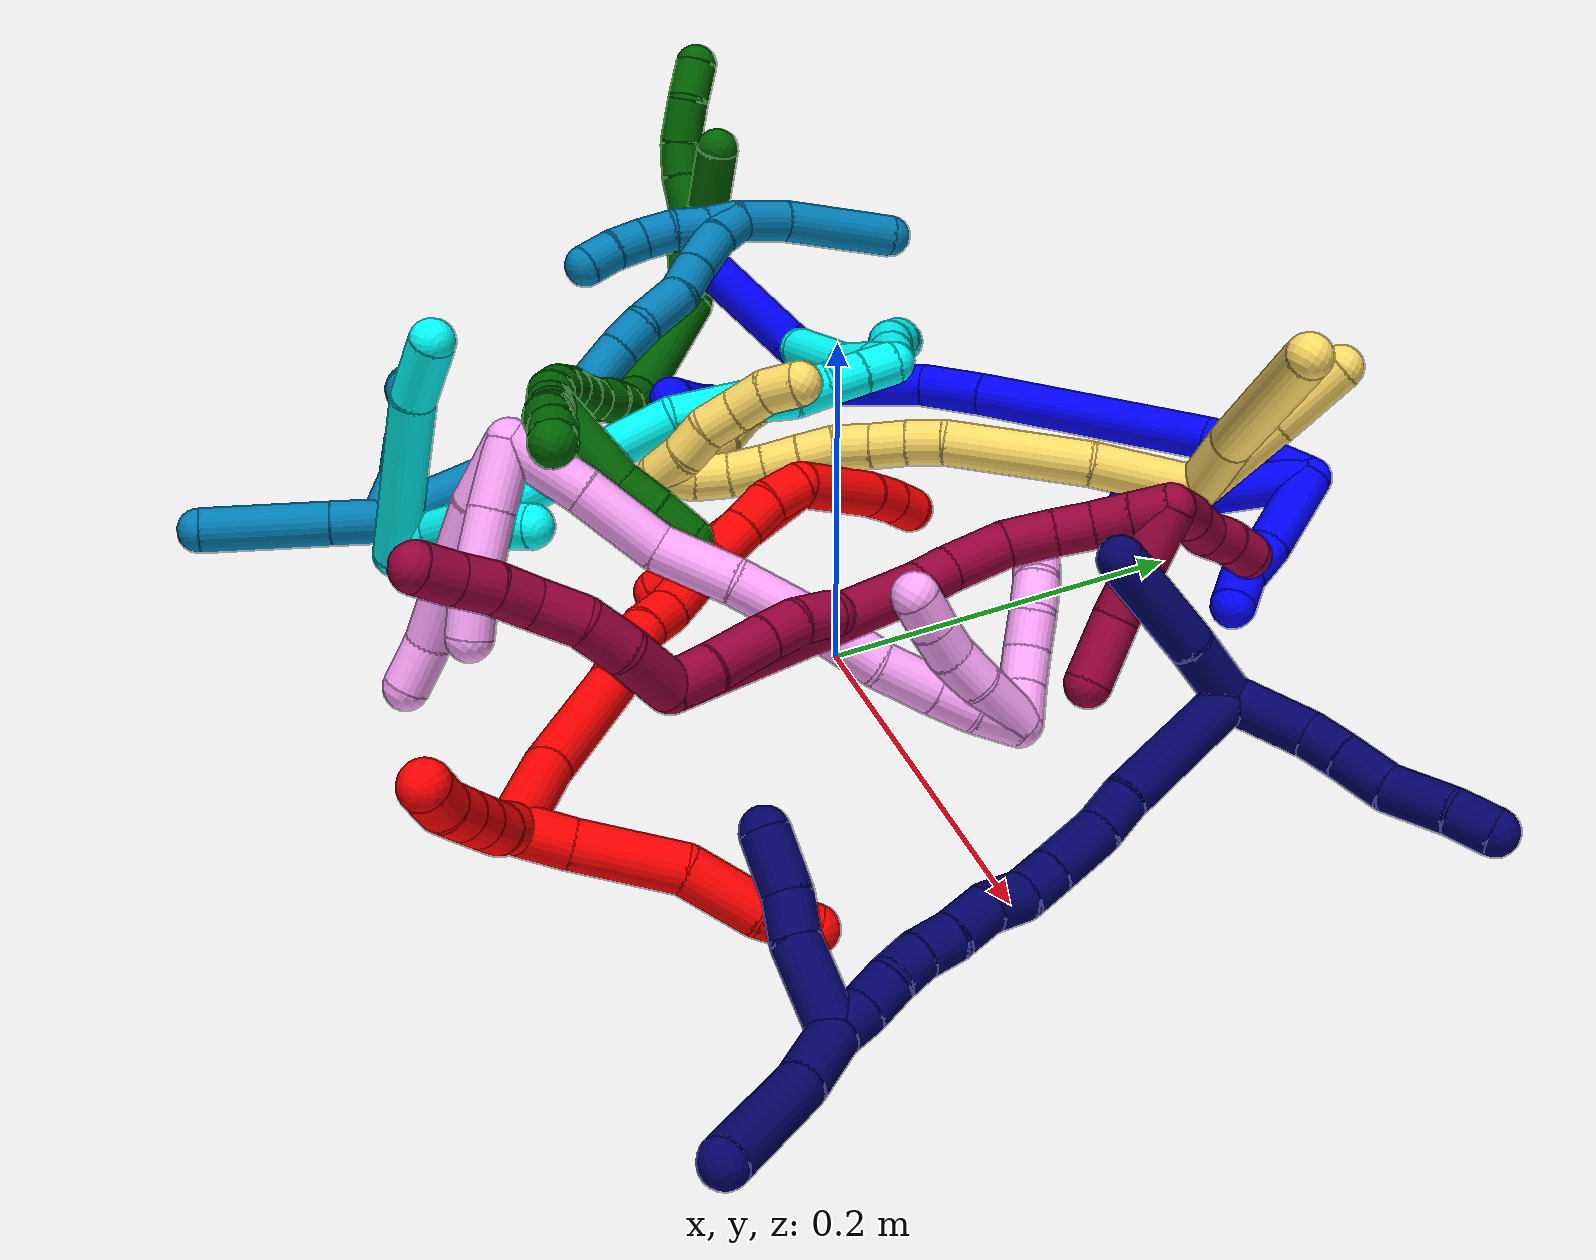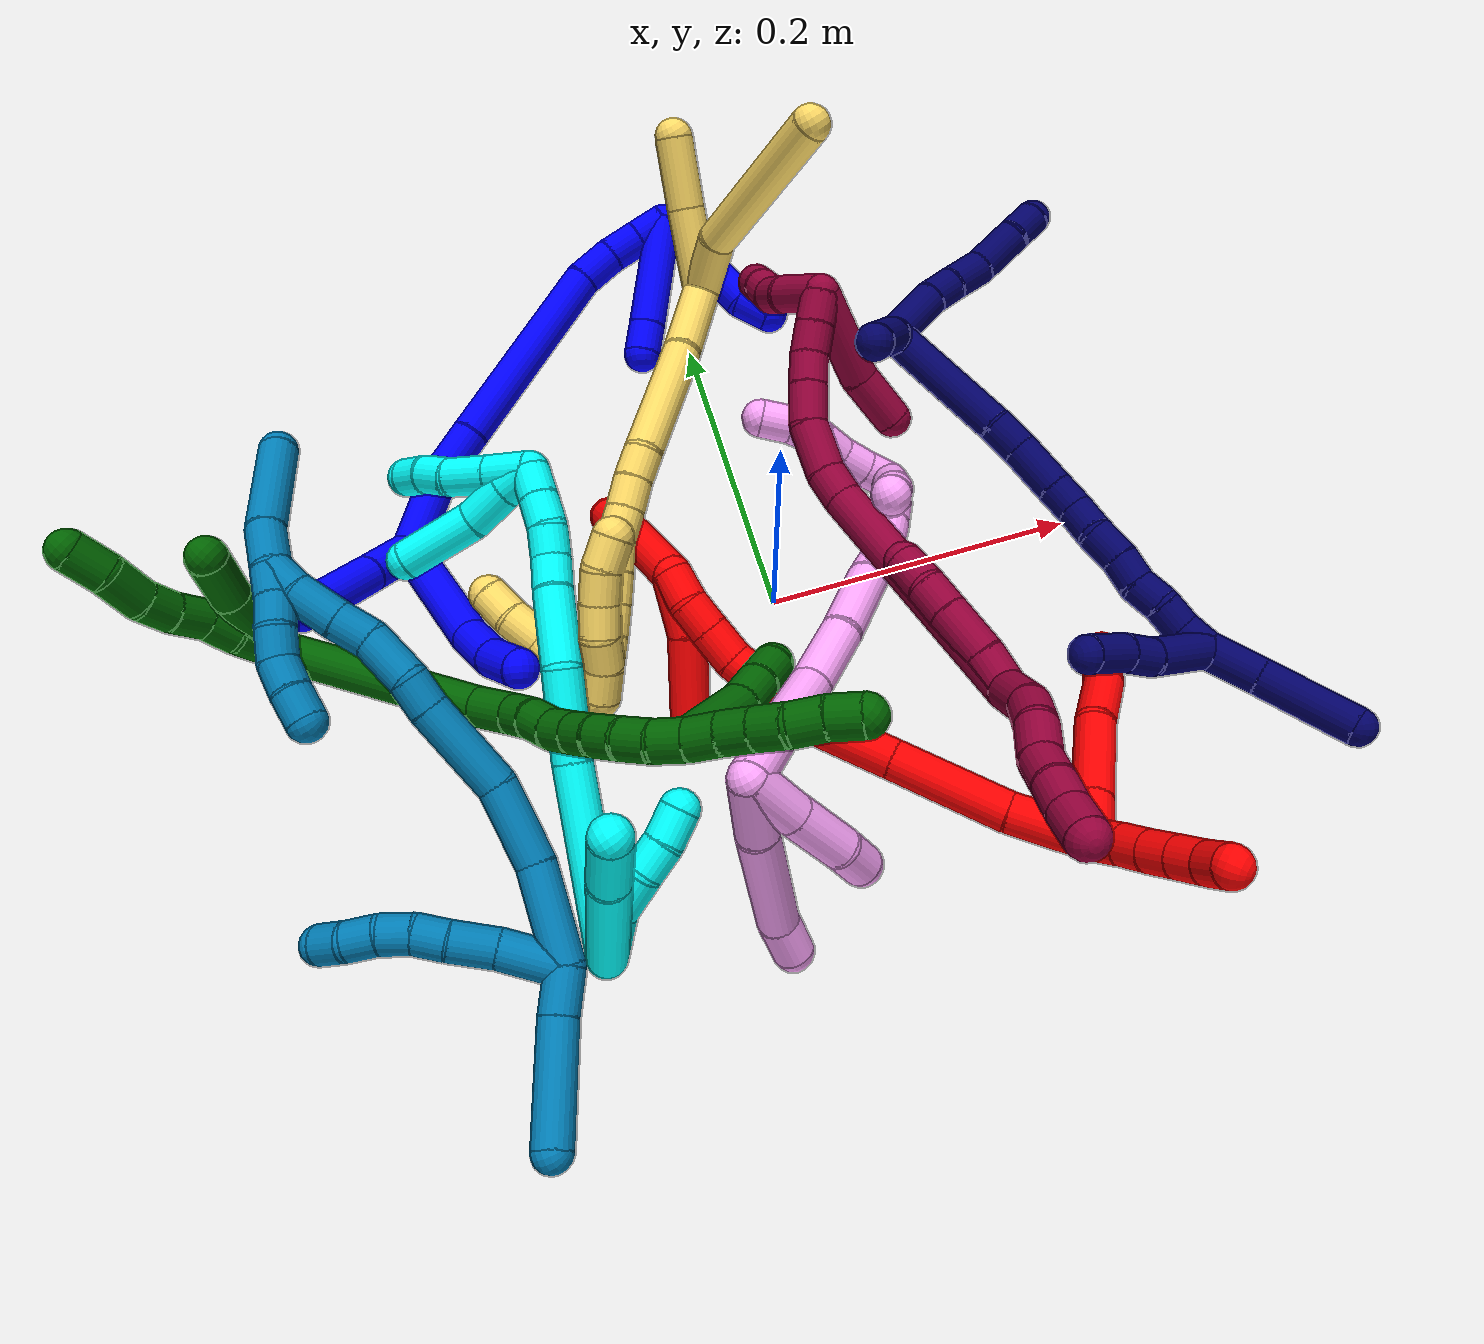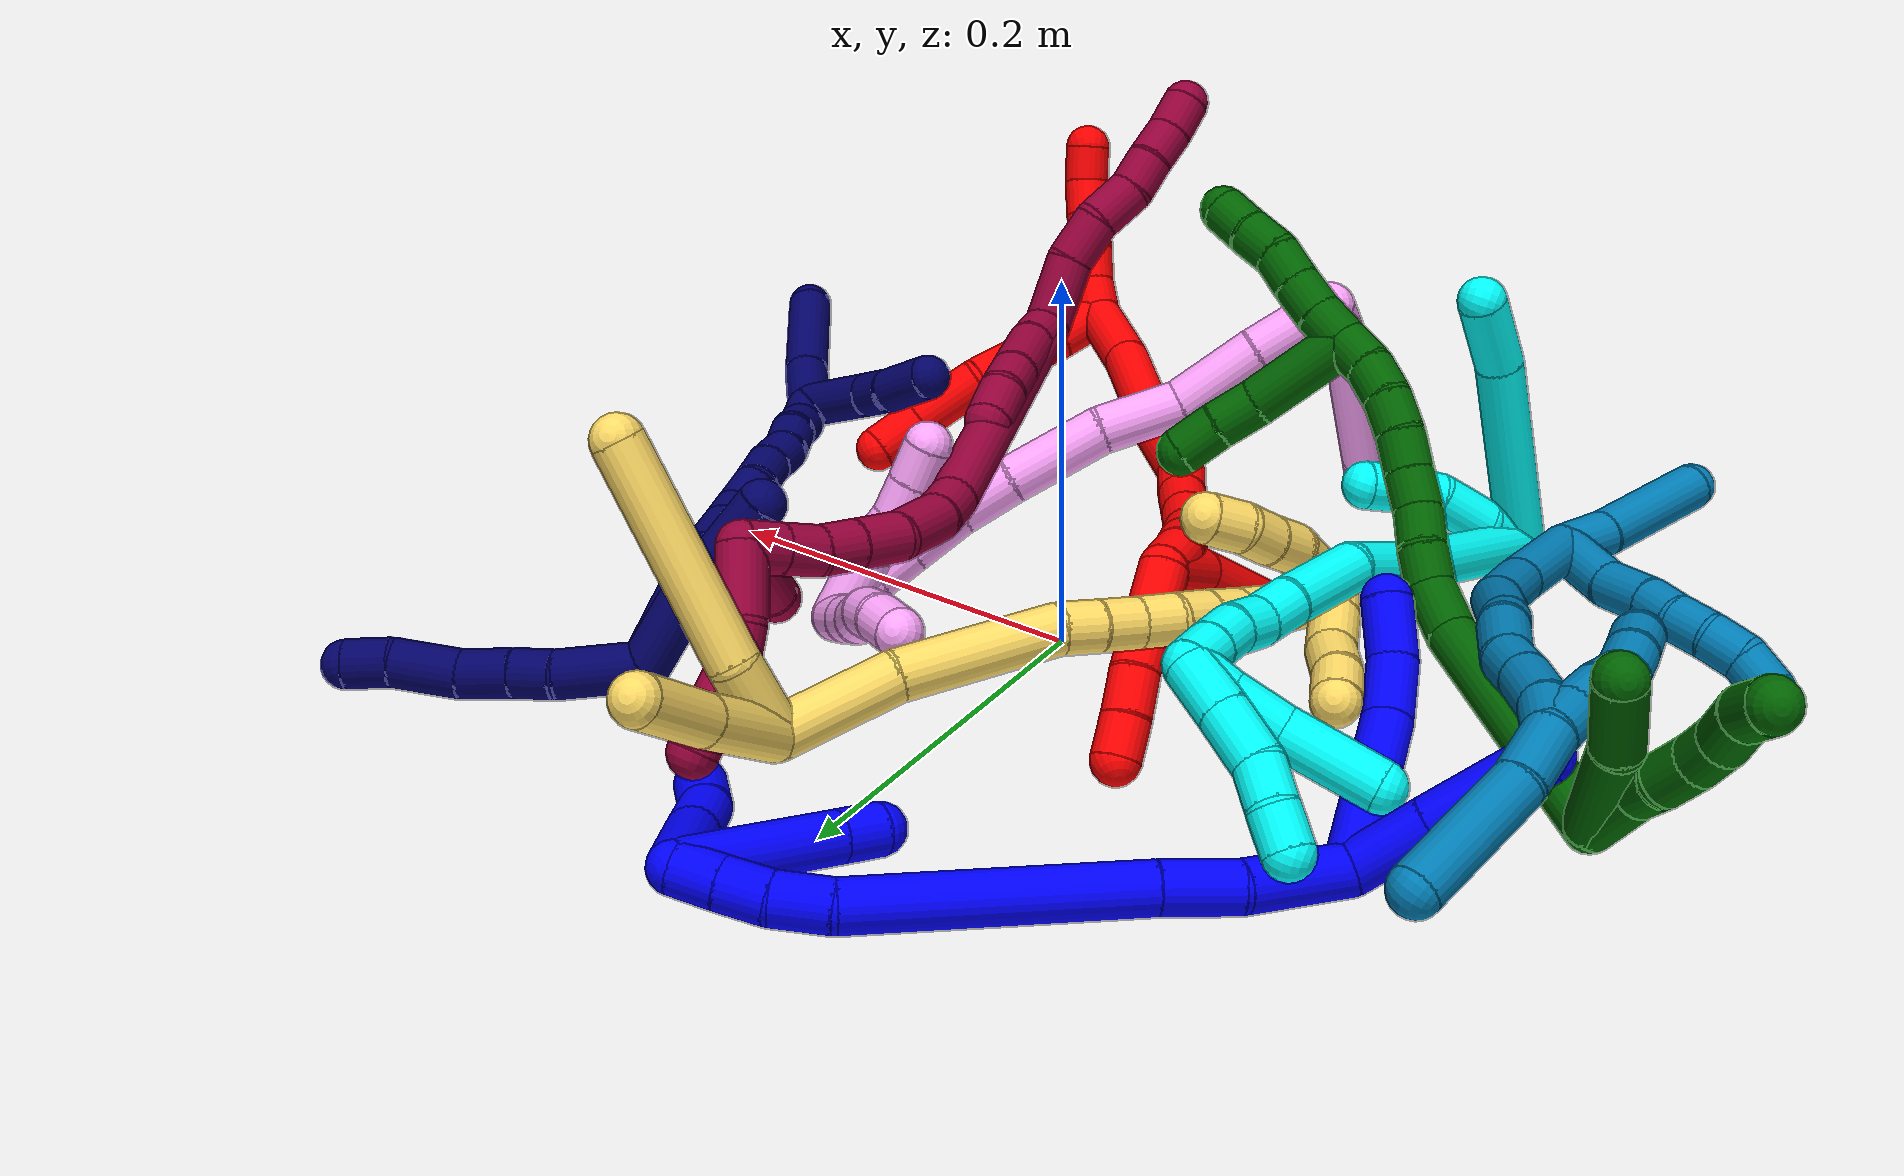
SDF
<sdf version="1.7">
 <world name="default">
  <plugin name="TubeGeneratorPlugin" filename="libtube_generator_plugin.so"/>
  <model name="photoneo_s_sensor">
   <static>1</static>
   <pose>0 0 2 1.57079 1.57079 3.14159</pose>
   <link name="link">
    <inertial><mass>0.1</mass></inertial>
    <sensor name="sensor" type="depth">
     <update_rate>30</update_rate>
     <camera>
      <horizontal_fov>1.22</horizontal_fov>
      <image><width>1920</width><height>1200</height><format>B8G8R8</format></image>
      <clip><near>0.1</near><far>4</far></clip>
      <depth_camera><output>points</output></depth_camera>
     </camera>
     <plugin name="camera_plugin" filename="libgazebo_ros_depth_camera.so">
      <baseline>0.2</baseline>
      <alwaysOn>1</alwaysOn>
      <updateRate>0.0</updateRate>
      <cameraName>camera_ir</cameraName>
      <imageTopicName>/camera/color/image_raw</imageTopicName>
      <cameraInfoTopicName>/camera/color/camera_info</cameraInfoTopicName>
      <depthImageTopicName>/camera/depth/image_raw</depthImageTopicName>
      <depthImageCameraInfoTopicName>/camera/depth/camera_info</depthImageCameraInfoTopicName>
      <pointCloudTopicName>/camera/depth/points</pointCloudTopicName>
      <frameName>fr_optical</frameName>
      <pointCloudCutoff>0.1</pointCloudCutoff>
      <pointCloudCutoffMax>2.0</pointCloudCutoffMax>
      <distortionK1>0</distortionK1>
      <distortionK2>0</distortionK2>
      <distortionK3>0</distortionK3>
      <distortionT1>0</distortionT1>
      <distortionT2>0</distortionT2>
      <CxPrime>0</CxPrime>
      <Cx>0</Cx>
      <Cy>0</Cy>
      <focalLength>0</focalLength>
      <hackBaseline>0</hackBaseline>
     </plugin>
    </sensor>
   </link>
  </model>
  <gravity>0 0 -9.8</gravity>
  <magnetic_field>6e-06 2.3e-05 -4.2e-05</magnetic_field>
  <atmosphere type="adiabatic"/>
  <physics name="default_physics" default="0" type="ode">
   <max_step_size>0.003</max_step_size>
   <real_time_factor>1</real_time_factor>
   <real_time_update_rate>1000</real_time_update_rate>
   <max_contacts>10000</max_contacts>
   <ode>
    <solver>
     <type>quick</type>
     <iters>100</iters>
     <sor>1.3</sor>
     <use_dynamic_moi_rescaling>0</use_dynamic_moi_rescaling>
    </solver>
    <constraints>
     <contact_max_correcting_vel>0</contact_max_correcting_vel>
     <contact_surface_layer>0.001</contact_surface_layer>
     <cfm>0</cfm>
     <erp>0.2</erp>
    </constraints>
   </ode>
  </physics>
  <scene><ambient>0.4 0.4 0.4 1</ambient><background>0.7 0.7 0.7 1</background><shadows>0</shadows></scene>
  <audio><device>default</device></audio>
  <spherical_coordinates>
   <surface_model>EARTH_WGS84</surface_model>
   <latitude_deg>0</latitude_deg>
   <longitude_deg>0</longitude_deg>
   <elevation>0</elevation>
   <heading_deg>0</heading_deg>
  </spherical_coordinates>
  <model name="bin">
   <static>1</static>
   <link name="bottom">
    <collision name="collision-bottom">
     <pose>0 0 -0.01 0 -0 0</pose>
     <geometry><box><size>0.8 0.6 0.02</size></box></geometry>
     <surface>
      <friction><ode><mu>100</mu><mu2>100</mu2></ode></friction>
      <contact><collide_bitmask>65535</collide_bitmask></contact>
     </surface>
    </collision>
   </link>
   <link name="west_wall">
    <collision name="collision-west_wall">
     <pose>-0.41 0 0.1 0 -0 0</pose>
     <geometry><box><size>0.02 0.6 0.2</size></box></geometry>
     <surface>
      <friction><ode><mu>100</mu><mu2>100</mu2></ode></friction>
      <contact><collide_bitmask>65535</collide_bitmask></contact>
     </surface>
    </collision>
   </link>
   <link name="east_wall">
    <collision name="collision-east_wall">
     <pose>0.41 0 0.1 0 -0 0</pose>
     <geometry><box><size>0.02 0.6 0.2</size></box></geometry>
     <surface>
      <friction><ode><mu>100</mu><mu2>100</mu2></ode></friction>
      <contact><collide_bitmask>65535</collide_bitmask></contact>
     </surface>
    </collision>
   </link>
   <link name="south_wall">
    <collision name="collision-south_wall">
     <pose>0 -0.31 0.1 0 -0 0</pose>
     <geometry><box><size>0.8 0.02 0.2</size></box></geometry>
     <surface>
      <friction><ode><mu>100</mu><mu2>100</mu2></ode></friction>
      <contact><collide_bitmask>65535</collide_bitmask></contact>
     </surface>
    </collision>
   </link>
   <link name="north_wall">
    <collision name="collision-north_wall">
     <pose>0 0.31 0.1 0 -0 0</pose>
     <geometry><box><size>0.8 0.02 0.2</size></box></geometry>
     <surface>
      <friction><ode><mu>100</mu><mu2>100</mu2></ode></friction>
      <contact><collide_bitmask>65535</collide_bitmask></contact>
     </surface>
    </collision>
   </link>
  </model>
  <model name="1">
   <static>0</static>
   <link name="1">
    <collision name="collision-cylinder-e_1_2_8">
     <pose>0.02136 -0.020133 -0.032819 2.59135 0.506487 1.48405</pose>
     <geometry><cylinder><radius>0.0125</radius><length>0.088061</length></cylinder></geometry>
     <surface>
      <friction><ode><mu>1.16</mu><mu2>1.16</mu2><slip1>0</slip1><slip2>0</slip2></ode></friction>
      <contact><ode><kp>1e+06</kp><kd>1</kd><max_vel>0</max_vel><min_depth>0.001</min_depth></ode></contact>
     </surface>
    </collision>
    <visual name="visual-cylinder-e_1_2_8">
     <pose>0.02136 -0.020133 -0.032819 2.59135 0.506487 1.48405</pose>
     <geometry><cylinder><radius>0.0125</radius><length>0.088061</length></cylinder></geometry>
     <material><ambient>0 0 1 1</ambient></material>
    </visual>
    <collision name="collision-cylinder-e_2_8_9">
     <pose>0.050889 -0.050551 -0.074156 2.26246 0.549048 1.07923</pose>
     <geometry><cylinder><radius>0.0125</radius><length>0.03131</length></cylinder></geometry>
     <surface>
      <friction><ode><mu>1.16</mu><mu2>1.16</mu2><slip1>0</slip1><slip2>0</slip2></ode></friction>
      <contact><ode><kp>1e+06</kp><kd>1</kd><max_vel>0</max_vel><min_depth>0.001</min_depth></ode></contact>
     </surface>
    </collision>
    <visual name="visual-cylinder-e_2_8_9">
     <pose>0.050889 -0.050551 -0.074156 2.26246 0.549048 1.07923</pose>
     <geometry><cylinder><radius>0.0125</radius><length>0.03131</length></cylinder></geometry>
     <material><ambient>0 0 1 1</ambient></material>
    </visual>
    <collision name="collision-cylinder-e_3_9_6">
     <pose>0.068443 -0.071785 -0.087831 2.01098 0.659537 0.989552</pose>
     <geometry><cylinder><radius>0.0125</radius><length>0.030629</length></cylinder></geometry>
     <surface>
      <friction><ode><mu>1.16</mu><mu2>1.16</mu2><slip1>0</slip1><slip2>0</slip2></ode></friction>
      <contact><ode><kp>1e+06</kp><kd>1</kd><max_vel>0</max_vel><min_depth>0.001</min_depth></ode></contact>
     </surface>
    </collision>
    <visual name="visual-cylinder-e_3_9_6">
     <pose>0.068443 -0.071785 -0.087831 2.01098 0.659537 0.989552</pose>
     <geometry><cylinder><radius>0.0125</radius><length>0.030629</length></cylinder></geometry>
     <material><ambient>0 0 1 1</ambient></material>
    </visual>
    <collision name="collision-cylinder-e_1_2_10">
     <pose>-0.01025 -0.014783 -0.009461 2.14009 -0.528571 -0.918436</pose>
     <geometry><cylinder><radius>0.0125</radius><length>0.04065</length></cylinder></geometry>
     <surface>
      <friction><ode><mu>1.16</mu><mu2>1.16</mu2><slip1>0</slip1><slip2>0</slip2></ode></friction>
      <contact><ode><kp>1e+06</kp><kd>1</kd><max_vel>0</max_vel><min_depth>0.001</min_depth></ode></contact>
     </surface>
    </collision>
    <visual name="visual-cylinder-e_1_2_10">
     <pose>-0.01025 -0.014783 -0.009461 2.14009 -0.528571 -0.918436</pose>
     <geometry><cylinder><radius>0.0125</radius><length>0.04065</length></cylinder></geometry>
     <material><ambient>0 0 1 1</ambient></material>
    </visual>
    <collision name="collision-cylinder-e_2_10_5">
     <pose>-0.035967 -0.0509 -0.032569 2.1399 -0.548276 -0.949144</pose>
     <geometry><cylinder><radius>0.0125</radius><length>0.05935</length></cylinder></geometry>
     <surface>
      <friction><ode><mu>1.16</mu><mu2>1.16</mu2><slip1>0</slip1><slip2>0</slip2></ode></friction>
      <contact><ode><kp>1e+06</kp><kd>1</kd><max_vel>0</max_vel><min_depth>0.001</min_depth></ode></contact>
     </surface>
    </collision>
    <visual name="visual-cylinder-e_2_10_5">
     <pose>-0.035967 -0.0509 -0.032569 2.1399 -0.548276 -0.949144</pose>
     <geometry><cylinder><radius>0.0125</radius><length>0.05935</length></cylinder></geometry>
     <material><ambient>0 0 1 1</ambient></material>
    </visual>
    <collision name="collision-cylinder-e_1_2_11">
     <pose>0.009969 0.004055 0.024302 -0.165315 0.384473 -0.032248</pose>
     <geometry><cylinder><radius>0.0125</radius><length>0.053157</length></cylinder></geometry>
     <surface>
      <friction><ode><mu>1.16</mu><mu2>1.16</mu2><slip1>0</slip1><slip2>0</slip2></ode></friction>
      <contact><ode><kp>1e+06</kp><kd>1</kd><max_vel>0</max_vel><min_depth>0.001</min_depth></ode></contact>
     </surface>
    </collision>
    <visual name="visual-cylinder-e_1_2_11">
     <pose>0.009969 0.004055 0.024302 -0.165315 0.384473 -0.032248</pose>
     <geometry><cylinder><radius>0.0125</radius><length>0.053157</length></cylinder></geometry>
     <material><ambient>0 0 1 1</ambient></material>
    </visual>
    <collision name="collision-cylinder-e_2_11_12">
     <pose>0.030908 0.010638 0.063485 -0.168318 0.628536 -0.054826</pose>
     <geometry><cylinder><radius>0.0125</radius><length>0.037318</length></cylinder></geometry>
     <surface>
      <friction><ode><mu>1.16</mu><mu2>1.16</mu2><slip1>0</slip1><slip2>0</slip2></ode></friction>
      <contact><ode><kp>1e+06</kp><kd>1</kd><max_vel>0</max_vel><min_depth>0.001</min_depth></ode></contact>
     </surface>
    </collision>
    <visual name="visual-cylinder-e_2_11_12">
     <pose>0.030908 0.010638 0.063485 -0.168318 0.628536 -0.054826</pose>
     <geometry><cylinder><radius>0.0125</radius><length>0.037318</length></cylinder></geometry>
     <material><ambient>0 0 1 1</ambient></material>
    </visual>
    <collision name="collision-cylinder-e_3_12_13">
     <pose>0.081711 0.026013 0.133176 -0.230234 0.61576 -0.073505</pose>
     <geometry><cylinder><radius>0.0125</radius><length>0.137926</length></cylinder></geometry>
     <surface>
      <friction><ode><mu>1.16</mu><mu2>1.16</mu2><slip1>0</slip1><slip2>0</slip2></ode></friction>
      <contact><ode><kp>1e+06</kp><kd>1</kd><max_vel>0</max_vel><min_depth>0.001</min_depth></ode></contact>
     </surface>
    </collision>
    <visual name="visual-cylinder-e_3_12_13">
     <pose>0.081711 0.026013 0.133176 -0.230234 0.61576 -0.073505</pose>
     <geometry><cylinder><radius>0.0125</radius><length>0.137926</length></cylinder></geometry>
     <material><ambient>0 0 1 1</ambient></material>
    </visual>
    <collision name="collision-cylinder-e_4_13_14">
     <pose>0.132109 0.040493 0.196579 -0.187782 0.879407 -0.088539</pose>
     <geometry><cylinder><radius>0.0125</radius><length>0.027434</length></cylinder></geometry>
     <surface>
      <friction><ode><mu>1.16</mu><mu2>1.16</mu2><slip1>0</slip1><slip2>0</slip2></ode></friction>
      <contact><ode><kp>1e+06</kp><kd>1</kd><max_vel>0</max_vel><min_depth>0.001</min_depth></ode></contact>
     </surface>
    </collision>
    <visual name="visual-cylinder-e_4_13_14">
     <pose>0.132109 0.040493 0.196579 -0.187782 0.879407 -0.088539</pose>
     <geometry><cylinder><radius>0.0125</radius><length>0.027434</length></cylinder></geometry>
     <material><ambient>0 0 1 1</ambient></material>
    </visual>
    <collision name="collision-cylinder-e_5_14_15">
     <pose>0.152597 0.042362 0.210758 -0.042242 1.05752 -0.024683</pose>
     <geometry><cylinder><radius>0.0125</radius><length>0.022776</length></cylinder></geometry>
     <surface>
      <friction><ode><mu>1.16</mu><mu2>1.16</mu2><slip1>0</slip1><slip2>0</slip2></ode></friction>
      <contact><ode><kp>1e+06</kp><kd>1</kd><max_vel>0</max_vel><min_depth>0.001</min_depth></ode></contact>
     </surface>
    </collision>
    <visual name="visual-cylinder-e_5_14_15">
     <pose>0.152597 0.042362 0.210758 -0.042242 1.05752 -0.024683</pose>
     <geometry><cylinder><radius>0.0125</radius><length>0.022776</length></cylinder></geometry>
     <material><ambient>0 0 1 1</ambient></material>
    </visual>
    <collision name="collision-cylinder-e_6_15_1">
     <pose>0.171928 0.042507 0.221424 0.017913 1.07581 0.010687</pose>
     <geometry><cylinder><radius>0.0125</radius><length>0.02139</length></cylinder></geometry>
     <surface>
      <friction><ode><mu>1.16</mu><mu2>1.16</mu2><slip1>0</slip1><slip2>0</slip2></ode></friction>
      <contact><ode><kp>1e+06</kp><kd>1</kd><max_vel>0</max_vel><min_depth>0.001</min_depth></ode></contact>
     </surface>
    </collision>
    <visual name="visual-cylinder-e_6_15_1">
     <pose>0.171928 0.042507 0.221424 0.017913 1.07581 0.010687</pose>
     <geometry><cylinder><radius>0.0125</radius><length>0.02139</length></cylinder></geometry>
     <material><ambient>0 0 1 1</ambient></material>
    </visual>
    <collision name="collision-cylinder-e_1_1_16">
     <pose>0.197777 0.046544 0.207678 -2.92572 0.706182 -2.56968</pose>
     <geometry><cylinder><radius>0.0125</radius><length>0.050661</length></cylinder></geometry>
     <surface>
      <friction><ode><mu>1.16</mu><mu2>1.16</mu2><slip1>0</slip1><slip2>0</slip2></ode></friction>
      <contact><ode><kp>1e+06</kp><kd>1</kd><max_vel>0</max_vel><min_depth>0.001</min_depth></ode></contact>
     </surface>
    </collision>
    <visual name="visual-cylinder-e_1_1_16">
     <pose>0.197777 0.046544 0.207678 -2.92572 0.706182 -2.56968</pose>
     <geometry><cylinder><radius>0.0125</radius><length>0.050661</length></cylinder></geometry>
     <material><ambient>0 0 1 1</ambient></material>
    </visual>
    <collision name="collision-cylinder-e_2_16_17">
     <pose>0.222308 0.050827 0.178549 -3.12665 0.665739 -3.09837</pose>
     <geometry><cylinder><radius>0.0125</radius><length>0.026206</length></cylinder></geometry>
     <surface>
      <friction><ode><mu>1.16</mu><mu2>1.16</mu2><slip1>0</slip1><slip2>0</slip2></ode></friction>
      <contact><ode><kp>1e+06</kp><kd>1</kd><max_vel>0</max_vel><min_depth>0.001</min_depth></ode></contact>
     </surface>
    </collision>
    <visual name="visual-cylinder-e_2_16_17">
     <pose>0.222308 0.050827 0.178549 -3.12665 0.665739 -3.09837</pose>
     <geometry><cylinder><radius>0.0125</radius><length>0.026206</length></cylinder></geometry>
     <material><ambient>0 0 1 1</ambient></material>
    </visual>
    <collision name="collision-cylinder-e_3_17_4">
     <pose>0.240101 0.050931 0.161944 3.1337 0.994682 3.12706</pose>
     <geometry><cylinder><radius>0.0125</radius><length>0.023132</length></cylinder></geometry>
     <surface>
      <friction><ode><mu>1.16</mu><mu2>1.16</mu2><slip1>0</slip1><slip2>0</slip2></ode></friction>
      <contact><ode><kp>1e+06</kp><kd>1</kd><max_vel>0</max_vel><min_depth>0.001</min_depth></ode></contact>
     </surface>
    </collision>
    <visual name="visual-cylinder-e_3_17_4">
     <pose>0.240101 0.050931 0.161944 3.1337 0.994682 3.12706</pose>
     <geometry><cylinder><radius>0.0125</radius><length>0.023132</length></cylinder></geometry>
     <material><ambient>0 0 1 1</ambient></material>
    </visual>
    <collision name="collision-cylinder-e_1_1_18">
     <pose>0.172772 0.039111 0.188119 3.05569 -0.218811 -2.39571</pose>
     <geometry><cylinder><radius>0.0125</radius><length>0.078937</length></cylinder></geometry>
     <surface>
      <friction><ode><mu>1.16</mu><mu2>1.16</mu2><slip1>0</slip1><slip2>0</slip2></ode></friction>
      <contact><ode><kp>1e+06</kp><kd>1</kd><max_vel>0</max_vel><min_depth>0.001</min_depth></ode></contact>
     </surface>
    </collision>
    <visual name="visual-cylinder-e_1_1_18">
     <pose>0.172772 0.039111 0.188119 3.05569 -0.218811 -2.39571</pose>
     <geometry><cylinder><radius>0.0125</radius><length>0.078937</length></cylinder></geometry>
     <material><ambient>0 0 1 1</ambient></material>
    </visual>
    <collision name="collision-cylinder-e_2_18_3">
     <pose>0.161803 0.034814 0.139527 3.0448 -0.230019 -2.34754</pose>
     <geometry><cylinder><radius>0.0125</radius><length>0.021063</length></cylinder></geometry>
     <surface>
      <friction><ode><mu>1.16</mu><mu2>1.16</mu2><slip1>0</slip1><slip2>0</slip2></ode></friction>
      <contact><ode><kp>1e+06</kp><kd>1</kd><max_vel>0</max_vel><min_depth>0.001</min_depth></ode></contact>
     </surface>
    </collision>
    <visual name="visual-cylinder-e_2_18_3">
     <pose>0.161803 0.034814 0.139527 3.0448 -0.230019 -2.34754</pose>
     <geometry><cylinder><radius>0.0125</radius><length>0.021063</length></cylinder></geometry>
     <material><ambient>0 0 1 1</ambient></material>
    </visual>
    <collision name="collision-sphere-3">
     <pose>0.159402 0.033823 0.129321 0 -0 0</pose>
     <geometry><sphere><radius>0.0125</radius></sphere></geometry>
     <surface>
      <friction><ode><mu>1.16</mu><mu2>1.16</mu2><slip1>0</slip1><slip2>0</slip2></ode></friction>
      <contact><ode><kp>1e+06</kp><kd>1</kd><max_vel>0</max_vel><min_depth>0.001</min_depth></ode></contact>
     </surface>
    </collision>
    <visual name="visual-sphere-3">
     <pose>0.159402 0.033823 0.129321 0 -0 0</pose>
     <geometry><sphere><radius>0.0125</radius></sphere></geometry>
     <material><ambient>0 0 1 1</ambient></material>
    </visual>
    <collision name="collision-sphere-5">
     <pose>-0.051434 -0.072234 -0.046216 0 -0 0</pose>
     <geometry><sphere><radius>0.0125</radius></sphere></geometry>
     <surface>
      <friction><ode><mu>1.16</mu><mu2>1.16</mu2><slip1>0</slip1><slip2>0</slip2></ode></friction>
      <contact><ode><kp>1e+06</kp><kd>1</kd><max_vel>0</max_vel><min_depth>0.001</min_depth></ode></contact>
     </surface>
    </collision>
    <visual name="visual-sphere-5">
     <pose>-0.051434 -0.072234 -0.046216 0 -0 0</pose>
     <geometry><sphere><radius>0.0125</radius></sphere></geometry>
     <material><ambient>0 0 1 1</ambient></material>
    </visual>
    <collision name="collision-sphere-10">
     <pose>-0.0205 -0.029566 -0.018922 0 -0 0</pose>
     <geometry><sphere><radius>0.0125</radius></sphere></geometry>
     <surface>
      <friction><ode><mu>1.16</mu><mu2>1.16</mu2><slip1>0</slip1><slip2>0</slip2></ode></friction>
      <contact><ode><kp>1e+06</kp><kd>1</kd><max_vel>0</max_vel><min_depth>0.001</min_depth></ode></contact>
     </surface>
    </collision>
    <visual name="visual-sphere-10">
     <pose>-0.0205 -0.029566 -0.018922 0 -0 0</pose>
     <geometry><sphere><radius>0.0125</radius></sphere></geometry>
     <material><ambient>0 0 1 1</ambient></material>
    </visual>
    <collision name="collision-sphere-6">
     <pose>0.077827 -0.082734 -0.092988 0 -0 0</pose>
     <geometry><sphere><radius>0.0125</radius></sphere></geometry>
     <surface>
      <friction><ode><mu>1.16</mu><mu2>1.16</mu2><slip1>0</slip1><slip2>0</slip2></ode></friction>
      <contact><ode><kp>1e+06</kp><kd>1</kd><max_vel>0</max_vel><min_depth>0.001</min_depth></ode></contact>
     </surface>
    </collision>
    <visual name="visual-sphere-6">
     <pose>0.077827 -0.082734 -0.092988 0 -0 0</pose>
     <geometry><sphere><radius>0.0125</radius></sphere></geometry>
     <material><ambient>0 0 1 1</ambient></material>
    </visual>
    <collision name="collision-sphere-9">
     <pose>0.059059 -0.060836 -0.082674 0 -0 0</pose>
     <geometry><sphere><radius>0.0125</radius></sphere></geometry>
     <surface>
      <friction><ode><mu>1.16</mu><mu2>1.16</mu2><slip1>0</slip1><slip2>0</slip2></ode></friction>
      <contact><ode><kp>1e+06</kp><kd>1</kd><max_vel>0</max_vel><min_depth>0.001</min_depth></ode></contact>
     </surface>
    </collision>
    <visual name="visual-sphere-9">
     <pose>0.059059 -0.060836 -0.082674 0 -0 0</pose>
     <geometry><sphere><radius>0.0125</radius></sphere></geometry>
     <material><ambient>0 0 1 1</ambient></material>
    </visual>
    <collision name="collision-sphere-2">
     <geometry><sphere><radius>0.0125</radius></sphere></geometry>
     <surface>
      <friction><ode><mu>1.16</mu><mu2>1.16</mu2><slip1>0</slip1><slip2>0</slip2></ode></friction>
      <contact><ode><kp>1e+06</kp><kd>1</kd><max_vel>0</max_vel><min_depth>0.001</min_depth></ode></contact>
     </surface>
    </collision>
    <visual name="visual-sphere-2">
     <geometry><sphere><radius>0.0125</radius></sphere></geometry>
     <material><ambient>0 0 1 1</ambient></material>
    </visual>
    <collision name="collision-sphere-8">
     <pose>0.042719 -0.040266 -0.065639 0 -0 0</pose>
     <geometry><sphere><radius>0.0125</radius></sphere></geometry>
     <surface>
      <friction><ode><mu>1.16</mu><mu2>1.16</mu2><slip1>0</slip1><slip2>0</slip2></ode></friction>
      <contact><ode><kp>1e+06</kp><kd>1</kd><max_vel>0</max_vel><min_depth>0.001</min_depth></ode></contact>
     </surface>
    </collision>
    <visual name="visual-sphere-8">
     <pose>0.042719 -0.040266 -0.065639 0 -0 0</pose>
     <geometry><sphere><radius>0.0125</radius></sphere></geometry>
     <material><ambient>0 0 1 1</ambient></material>
    </visual>
    <collision name="collision-sphere-11">
     <pose>0.019938 0.008109 0.048605 0 -0 0</pose>
     <geometry><sphere><radius>0.0125</radius></sphere></geometry>
     <surface>
      <friction><ode><mu>1.16</mu><mu2>1.16</mu2><slip1>0</slip1><slip2>0</slip2></ode></friction>
      <contact><ode><kp>1e+06</kp><kd>1</kd><max_vel>0</max_vel><min_depth>0.001</min_depth></ode></contact>
     </surface>
    </collision>
    <visual name="visual-sphere-11">
     <pose>0.019938 0.008109 0.048605 0 -0 0</pose>
     <geometry><sphere><radius>0.0125</radius></sphere></geometry>
     <material><ambient>0 0 1 1</ambient></material>
    </visual>
    <collision name="collision-sphere-12">
     <pose>0.041879 0.013166 0.078364 0 -0 0</pose>
     <geometry><sphere><radius>0.0125</radius></sphere></geometry>
     <surface>
      <friction><ode><mu>1.16</mu><mu2>1.16</mu2><slip1>0</slip1><slip2>0</slip2></ode></friction>
      <contact><ode><kp>1e+06</kp><kd>1</kd><max_vel>0</max_vel><min_depth>0.001</min_depth></ode></contact>
     </surface>
    </collision>
    <visual name="visual-sphere-12">
     <pose>0.041879 0.013166 0.078364 0 -0 0</pose>
     <geometry><sphere><radius>0.0125</radius></sphere></geometry>
     <material><ambient>0 0 1 1</ambient></material>
    </visual>
    <collision name="collision-sphere-13">
     <pose>0.121542 0.038861 0.187987 0 -0 0</pose>
     <geometry><sphere><radius>0.0125</radius></sphere></geometry>
     <surface>
      <friction><ode><mu>1.16</mu><mu2>1.16</mu2><slip1>0</slip1><slip2>0</slip2></ode></friction>
      <contact><ode><kp>1e+06</kp><kd>1</kd><max_vel>0</max_vel><min_depth>0.001</min_depth></ode></contact>
     </surface>
    </collision>
    <visual name="visual-sphere-13">
     <pose>0.121542 0.038861 0.187987 0 -0 0</pose>
     <geometry><sphere><radius>0.0125</radius></sphere></geometry>
     <material><ambient>0 0 1 1</ambient></material>
    </visual>
    <collision name="collision-sphere-14">
     <pose>0.142676 0.042126 0.205171 0 -0 0</pose>
     <geometry><sphere><radius>0.0125</radius></sphere></geometry>
     <surface>
      <friction><ode><mu>1.16</mu><mu2>1.16</mu2><slip1>0</slip1><slip2>0</slip2></ode></friction>
      <contact><ode><kp>1e+06</kp><kd>1</kd><max_vel>0</max_vel><min_depth>0.001</min_depth></ode></contact>
     </surface>
    </collision>
    <visual name="visual-sphere-14">
     <pose>0.142676 0.042126 0.205171 0 -0 0</pose>
     <geometry><sphere><radius>0.0125</radius></sphere></geometry>
     <material><ambient>0 0 1 1</ambient></material>
    </visual>
    <collision name="collision-sphere-15">
     <pose>0.162517 0.042598 0.216345 0 -0 0</pose>
     <geometry><sphere><radius>0.0125</radius></sphere></geometry>
     <surface>
      <friction><ode><mu>1.16</mu><mu2>1.16</mu2><slip1>0</slip1><slip2>0</slip2></ode></friction>
      <contact><ode><kp>1e+06</kp><kd>1</kd><max_vel>0</max_vel><min_depth>0.001</min_depth></ode></contact>
     </surface>
    </collision>
    <visual name="visual-sphere-15">
     <pose>0.162517 0.042598 0.216345 0 -0 0</pose>
     <geometry><sphere><radius>0.0125</radius></sphere></geometry>
     <material><ambient>0 0 1 1</ambient></material>
    </visual>
    <collision name="collision-sphere-1">
     <pose>0.181339 0.042416 0.226504 0 -0 0</pose>
     <geometry><sphere><radius>0.0125</radius></sphere></geometry>
     <surface>
      <friction><ode><mu>1.16</mu><mu2>1.16</mu2><slip1>0</slip1><slip2>0</slip2></ode></friction>
      <contact><ode><kp>1e+06</kp><kd>1</kd><max_vel>0</max_vel><min_depth>0.001</min_depth></ode></contact>
     </surface>
    </collision>
    <visual name="visual-sphere-1">
     <pose>0.181339 0.042416 0.226504 0 -0 0</pose>
     <geometry><sphere><radius>0.0125</radius></sphere></geometry>
     <material><ambient>0 0 1 1</ambient></material>
    </visual>
    <collision name="collision-sphere-18">
     <pose>0.164205 0.035805 0.149733 0 -0 0</pose>
     <geometry><sphere><radius>0.0125</radius></sphere></geometry>
     <surface>
      <friction><ode><mu>1.16</mu><mu2>1.16</mu2><slip1>0</slip1><slip2>0</slip2></ode></friction>
      <contact><ode><kp>1e+06</kp><kd>1</kd><max_vel>0</max_vel><min_depth>0.001</min_depth></ode></contact>
     </surface>
    </collision>
    <visual name="visual-sphere-18">
     <pose>0.164205 0.035805 0.149733 0 -0 0</pose>
     <geometry><sphere><radius>0.0125</radius></sphere></geometry>
     <material><ambient>0 0 1 1</ambient></material>
    </visual>
    <collision name="collision-sphere-16">
     <pose>0.214215 0.050672 0.188853 0 -0 0</pose>
     <geometry><sphere><radius>0.0125</radius></sphere></geometry>
     <surface>
      <friction><ode><mu>1.16</mu><mu2>1.16</mu2><slip1>0</slip1><slip2>0</slip2></ode></friction>
      <contact><ode><kp>1e+06</kp><kd>1</kd><max_vel>0</max_vel><min_depth>0.001</min_depth></ode></contact>
     </surface>
    </collision>
    <visual name="visual-sphere-16">
     <pose>0.214215 0.050672 0.188853 0 -0 0</pose>
     <geometry><sphere><radius>0.0125</radius></sphere></geometry>
     <material><ambient>0 0 1 1</ambient></material>
    </visual>
    <collision name="collision-sphere-17">
     <pose>0.230401 0.050981 0.168245 0 -0 0</pose>
     <geometry><sphere><radius>0.0125</radius></sphere></geometry>
     <surface>
      <friction><ode><mu>1.16</mu><mu2>1.16</mu2><slip1>0</slip1><slip2>0</slip2></ode></friction>
      <contact><ode><kp>1e+06</kp><kd>1</kd><max_vel>0</max_vel><min_depth>0.001</min_depth></ode></contact>
     </surface>
    </collision>
    <visual name="visual-sphere-17">
     <pose>0.230401 0.050981 0.168245 0 -0 0</pose>
     <geometry><sphere><radius>0.0125</radius></sphere></geometry>
     <material><ambient>0 0 1 1</ambient></material>
    </visual>
    <collision name="collision-sphere-4">
     <pose>0.2498 0.050881 0.155644 0 -0 0</pose>
     <geometry><sphere><radius>0.0125</radius></sphere></geometry>
     <surface>
      <friction><ode><mu>1.16</mu><mu2>1.16</mu2><slip1>0</slip1><slip2>0</slip2></ode></friction>
      <contact><ode><kp>1e+06</kp><kd>1</kd><max_vel>0</max_vel><min_depth>0.001</min_depth></ode></contact>
     </surface>
    </collision>
    <visual name="visual-sphere-4">
     <pose>0.2498 0.050881 0.155644 0 -0 0</pose>
     <geometry><sphere><radius>0.0125</radius></sphere></geometry>
     <material><ambient>0 0 1 1</ambient></material>
    </visual>
    <inertial>
     <pose>0.086928 0.00893 0.084632 0 -0 0</pose>
     <mass>0.75</mass>
     <inertia>
      <ixx>0.00019</ixx>
      <ixy>0</ixy>
      <ixz>0</ixz>
      <iyy>0.000289</iyy>
      <iyz>0</iyz>
      <izz>-0.000162</izz>
     </inertia>
    </inertial>
   </link>
   <pose>-0.217611 0.100159 0.011492 -1.3004 -0.029862 -0.211089</pose>
  </model>
  <model name="2">
   <static>0</static>
   <link name="2">
    <collision name="collision-cylinder-e_1_2_8">
     <pose>0.005946 0.01095 -0.00622 -2.08738 0.441114 -0.735375</pose>
     <geometry><cylinder><radius>0.0125</radius><length>0.027853</length></cylinder></geometry>
     <surface>
      <friction><ode><mu>1.16</mu><mu2>1.16</mu2><slip1>0</slip1><slip2>0</slip2></ode></friction>
      <contact><ode><kp>1e+06</kp><kd>1</kd><max_vel>0</max_vel><min_depth>0.001</min_depth></ode></contact>
     </surface>
    </collision>
    <visual name="visual-cylinder-e_1_2_8">
     <pose>0.005946 0.01095 -0.00622 -2.08738 0.441114 -0.735375</pose>
     <geometry><cylinder><radius>0.0125</radius><length>0.027853</length></cylinder></geometry>
     <material><ambient>1 0 0 1</ambient></material>
    </visual>
    <collision name="collision-cylinder-e_2_8_9">
     <pose>0.021747 0.044146 -0.024043 -2.05157 0.374293 -0.605483</pose>
     <geometry><cylinder><radius>0.0125</radius><length>0.053912</length></cylinder></geometry>
     <surface>
      <friction><ode><mu>1.16</mu><mu2>1.16</mu2><slip1>0</slip1><slip2>0</slip2></ode></friction>
      <contact><ode><kp>1e+06</kp><kd>1</kd><max_vel>0</max_vel><min_depth>0.001</min_depth></ode></contact>
     </surface>
    </collision>
    <visual name="visual-cylinder-e_2_8_9">
     <pose>0.021747 0.044146 -0.024043 -2.05157 0.374293 -0.605483</pose>
     <geometry><cylinder><radius>0.0125</radius><length>0.053912</length></cylinder></geometry>
     <material><ambient>1 0 0 1</ambient></material>
    </visual>
    <collision name="collision-cylinder-e_3_9_10">
     <pose>0.044268 0.080395 -0.042396 -2.01993 0.683669 -1.0308</pose>
     <geometry><cylinder><radius>0.0125</radius><length>0.040103</length></cylinder></geometry>
     <surface>
      <friction><ode><mu>1.16</mu><mu2>1.16</mu2><slip1>0</slip1><slip2>0</slip2></ode></friction>
      <contact><ode><kp>1e+06</kp><kd>1</kd><max_vel>0</max_vel><min_depth>0.001</min_depth></ode></contact>
     </surface>
    </collision>
    <visual name="visual-cylinder-e_3_9_10">
     <pose>0.044268 0.080395 -0.042396 -2.01993 0.683669 -1.0308</pose>
     <geometry><cylinder><radius>0.0125</radius><length>0.040103</length></cylinder></geometry>
     <material><ambient>1 0 0 1</ambient></material>
    </visual>
    <collision name="collision-cylinder-e_4_10_6">
     <pose>0.063572 0.104762 -0.055955 -2.15217 0.491487 -0.870413</pose>
     <geometry><cylinder><radius>0.0125</radius><length>0.028132</length></cylinder></geometry>
     <surface>
      <friction><ode><mu>1.16</mu><mu2>1.16</mu2><slip1>0</slip1><slip2>0</slip2></ode></friction>
      <contact><ode><kp>1e+06</kp><kd>1</kd><max_vel>0</max_vel><min_depth>0.001</min_depth></ode></contact>
     </surface>
    </collision>
    <visual name="visual-cylinder-e_4_10_6">
     <pose>0.063572 0.104762 -0.055955 -2.15217 0.491487 -0.870413</pose>
     <geometry><cylinder><radius>0.0125</radius><length>0.028132</length></cylinder></geometry>
     <material><ambient>1 0 0 1</ambient></material>
    </visual>
    <collision name="collision-cylinder-e_1_2_11">
     <pose>-0.003139 0.001865 0.00931 -0.197701 -0.319298 0.031935</pose>
     <geometry><cylinder><radius>0.0125</radius><length>0.02</length></cylinder></geometry>
     <surface>
      <friction><ode><mu>1.16</mu><mu2>1.16</mu2><slip1>0</slip1><slip2>0</slip2></ode></friction>
      <contact><ode><kp>1e+06</kp><kd>1</kd><max_vel>0</max_vel><min_depth>0.001</min_depth></ode></contact>
     </surface>
    </collision>
    <visual name="visual-cylinder-e_1_2_11">
     <pose>-0.003139 0.001865 0.00931 -0.197701 -0.319298 0.031935</pose>
     <geometry><cylinder><radius>0.0125</radius><length>0.02</length></cylinder></geometry>
     <material><ambient>1 0 0 1</ambient></material>
    </visual>
    <collision name="collision-cylinder-e_2_11_12">
     <pose>-0.011129 0.00473 0.027306 -0.114615 -0.506504 0.029694</pose>
     <geometry><cylinder><radius>0.0125</radius><length>0.02</length></cylinder></geometry>
     <surface>
      <friction><ode><mu>1.16</mu><mu2>1.16</mu2><slip1>0</slip1><slip2>0</slip2></ode></friction>
      <contact><ode><kp>1e+06</kp><kd>1</kd><max_vel>0</max_vel><min_depth>0.001</min_depth></ode></contact>
     </surface>
    </collision>
    <visual name="visual-cylinder-e_2_11_12">
     <pose>-0.011129 0.00473 0.027306 -0.114615 -0.506504 0.029694</pose>
     <geometry><cylinder><radius>0.0125</radius><length>0.02</length></cylinder></geometry>
     <material><ambient>1 0 0 1</ambient></material>
    </visual>
    <collision name="collision-cylinder-e_3_12_13">
     <pose>-0.020754 0.007085 0.044675 -0.154884 -0.497666 0.03943</pose>
     <geometry><cylinder><radius>0.0125</radius><length>0.02</length></cylinder></geometry>
     <surface>
      <friction><ode><mu>1.16</mu><mu2>1.16</mu2><slip1>0</slip1><slip2>0</slip2></ode></friction>
      <contact><ode><kp>1e+06</kp><kd>1</kd><max_vel>0</max_vel><min_depth>0.001</min_depth></ode></contact>
     </surface>
    </collision>
    <visual name="visual-cylinder-e_3_12_13">
     <pose>-0.020754 0.007085 0.044675 -0.154884 -0.497666 0.03943</pose>
     <geometry><cylinder><radius>0.0125</radius><length>0.02</length></cylinder></geometry>
     <material><ambient>1 0 0 1</ambient></material>
    </visual>
    <collision name="collision-cylinder-e_4_13_14">
     <pose>-0.030401 0.009675 0.062002 -0.141828 -0.508939 0.036948</pose>
     <geometry><cylinder><radius>0.0125</radius><length>0.02</length></cylinder></geometry>
     <surface>
      <friction><ode><mu>1.16</mu><mu2>1.16</mu2><slip1>0</slip1><slip2>0</slip2></ode></friction>
      <contact><ode><kp>1e+06</kp><kd>1</kd><max_vel>0</max_vel><min_depth>0.001</min_depth></ode></contact>
     </surface>
    </collision>
    <visual name="visual-cylinder-e_4_13_14">
     <pose>-0.030401 0.009675 0.062002 -0.141828 -0.508939 0.036948</pose>
     <geometry><cylinder><radius>0.0125</radius><length>0.02</length></cylinder></geometry>
     <material><ambient>1 0 0 1</ambient></material>
    </visual>
    <collision name="collision-cylinder-e_5_14_5">
     <pose>-0.042197 0.01204 0.077773 -0.157251 -0.764743 0.06335</pose>
     <geometry><cylinder><radius>0.0125</radius><length>0.02</length></cylinder></geometry>
     <surface>
      <friction><ode><mu>1.16</mu><mu2>1.16</mu2><slip1>0</slip1><slip2>0</slip2></ode></friction>
      <contact><ode><kp>1e+06</kp><kd>1</kd><max_vel>0</max_vel><min_depth>0.001</min_depth></ode></contact>
     </surface>
    </collision>
    <visual name="visual-cylinder-e_5_14_5">
     <pose>-0.042197 0.01204 0.077773 -0.157251 -0.764743 0.06335</pose>
     <geometry><cylinder><radius>0.0125</radius><length>0.02</length></cylinder></geometry>
     <material><ambient>1 0 0 1</ambient></material>
    </visual>
    <collision name="collision-cylinder-e_1_2_15">
     <pose>-0.006734 -0.002831 -0.023187 3.0201 -0.280653 -2.3284</pose>
     <geometry><cylinder><radius>0.0125</radius><length>0.048621</length></cylinder></geometry>
     <surface>
      <friction><ode><mu>1.16</mu><mu2>1.16</mu2><slip1>0</slip1><slip2>0</slip2></ode></friction>
      <contact><ode><kp>1e+06</kp><kd>1</kd><max_vel>0</max_vel><min_depth>0.001</min_depth></ode></contact>
     </surface>
    </collision>
    <visual name="visual-cylinder-e_1_2_15">
     <pose>-0.006734 -0.002831 -0.023187 3.0201 -0.280653 -2.3284</pose>
     <geometry><cylinder><radius>0.0125</radius><length>0.048621</length></cylinder></geometry>
     <material><ambient>1 0 0 1</ambient></material>
    </visual>
    <collision name="collision-cylinder-e_2_15_16">
     <pose>-0.023161 -0.005592 -0.081609 -3.13959 -0.268489 3.12676</pose>
     <geometry><cylinder><radius>0.0125</radius><length>0.073087</length></cylinder></geometry>
     <surface>
      <friction><ode><mu>1.16</mu><mu2>1.16</mu2><slip1>0</slip1><slip2>0</slip2></ode></friction>
      <contact><ode><kp>1e+06</kp><kd>1</kd><max_vel>0</max_vel><min_depth>0.001</min_depth></ode></contact>
     </surface>
    </collision>
    <visual name="visual-cylinder-e_2_15_16">
     <pose>-0.023161 -0.005592 -0.081609 -3.13959 -0.268489 3.12676</pose>
     <geometry><cylinder><radius>0.0125</radius><length>0.073087</length></cylinder></geometry>
     <material><ambient>1 0 0 1</ambient></material>
    </visual>
    <collision name="collision-cylinder-e_3_16_17">
     <pose>-0.041776 -0.005699 -0.138344 3.13332 -0.393248 -3.10004</pose>
     <geometry><cylinder><radius>0.0125</radius><length>0.046558</length></cylinder></geometry>
     <surface>
      <friction><ode><mu>1.16</mu><mu2>1.16</mu2><slip1>0</slip1><slip2>0</slip2></ode></friction>
      <contact><ode><kp>1e+06</kp><kd>1</kd><max_vel>0</max_vel><min_depth>0.001</min_depth></ode></contact>
     </surface>
    </collision>
    <visual name="visual-cylinder-e_3_16_17">
     <pose>-0.041776 -0.005699 -0.138344 3.13332 -0.393248 -3.10004</pose>
     <geometry><cylinder><radius>0.0125</radius><length>0.046558</length></cylinder></geometry>
     <material><ambient>1 0 0 1</ambient></material>
    </visual>
    <collision name="collision-cylinder-e_4_17_18">
     <pose>-0.052466 -0.003739 -0.169811 -2.93028 -0.171953 1.36488</pose>
     <geometry><cylinder><radius>0.0125</radius><length>0.020691</length></cylinder></geometry>
     <surface>
      <friction><ode><mu>1.16</mu><mu2>1.16</mu2><slip1>0</slip1><slip2>0</slip2></ode></friction>
      <contact><ode><kp>1e+06</kp><kd>1</kd><max_vel>0</max_vel><min_depth>0.001</min_depth></ode></contact>
     </surface>
    </collision>
    <visual name="visual-cylinder-e_4_17_18">
     <pose>-0.052466 -0.003739 -0.169811 -2.93028 -0.171953 1.36488</pose>
     <geometry><cylinder><radius>0.0125</radius><length>0.020691</length></cylinder></geometry>
     <material><ambient>1 0 0 1</ambient></material>
    </visual>
    <collision name="collision-cylinder-e_5_18_19">
     <pose>-0.058749 0.000839 -0.190184 -2.91129 -0.399494 2.10346</pose>
     <geometry><cylinder><radius>0.0125</radius><length>0.023206</length></cylinder></geometry>
     <surface>
      <friction><ode><mu>1.16</mu><mu2>1.16</mu2><slip1>0</slip1><slip2>0</slip2></ode></friction>
      <contact><ode><kp>1e+06</kp><kd>1</kd><max_vel>0</max_vel><min_depth>0.001</min_depth></ode></contact>
     </surface>
    </collision>
    <visual name="visual-cylinder-e_5_18_19">
     <pose>-0.058749 0.000839 -0.190184 -2.91129 -0.399494 2.10346</pose>
     <geometry><cylinder><radius>0.0125</radius><length>0.023206</length></cylinder></geometry>
     <material><ambient>1 0 0 1</ambient></material>
    </visual>
    <collision name="collision-cylinder-e_6_19_20">
     <pose>-0.067902 0.006007 -0.210606 -2.87559 -0.4204 2.02139</pose>
     <geometry><cylinder><radius>0.0125</radius><length>0.022739</length></cylinder></geometry>
     <surface>
      <friction><ode><mu>1.16</mu><mu2>1.16</mu2><slip1>0</slip1><slip2>0</slip2></ode></friction>
      <contact><ode><kp>1e+06</kp><kd>1</kd><max_vel>0</max_vel><min_depth>0.001</min_depth></ode></contact>
     </surface>
    </collision>
    <visual name="visual-cylinder-e_6_19_20">
     <pose>-0.067902 0.006007 -0.210606 -2.87559 -0.4204 2.02139</pose>
     <geometry><cylinder><radius>0.0125</radius><length>0.022739</length></cylinder></geometry>
     <material><ambient>1 0 0 1</ambient></material>
    </visual>
    <collision name="collision-cylinder-e_7_20_21">
     <pose>-0.078122 0.013713 -0.229421 -2.62697 -0.504266 1.54956</pose>
     <geometry><cylinder><radius>0.0125</radius><length>0.023097</length></cylinder></geometry>
     <surface>
      <friction><ode><mu>1.16</mu><mu2>1.16</mu2><slip1>0</slip1><slip2>0</slip2></ode></friction>
      <contact><ode><kp>1e+06</kp><kd>1</kd><max_vel>0</max_vel><min_depth>0.001</min_depth></ode></contact>
     </surface>
    </collision>
    <visual name="visual-cylinder-e_7_20_21">
     <pose>-0.078122 0.013713 -0.229421 -2.62697 -0.504266 1.54956</pose>
     <geometry><cylinder><radius>0.0125</radius><length>0.023097</length></cylinder></geometry>
     <material><ambient>1 0 0 1</ambient></material>
    </visual>
    <collision name="collision-cylinder-e_8_21_22">
     <pose>-0.088758 0.023297 -0.246066 -2.61043 -0.507336 1.52279</pose>
     <geometry><cylinder><radius>0.0125</radius><length>0.020814</length></cylinder></geometry>
     <surface>
      <friction><ode><mu>1.16</mu><mu2>1.16</mu2><slip1>0</slip1><slip2>0</slip2></ode></friction>
      <contact><ode><kp>1e+06</kp><kd>1</kd><max_vel>0</max_vel><min_depth>0.001</min_depth></ode></contact>
     </surface>
    </collision>
    <visual name="visual-cylinder-e_8_21_22">
     <pose>-0.088758 0.023297 -0.246066 -2.61043 -0.507336 1.52279</pose>
     <geometry><cylinder><radius>0.0125</radius><length>0.020814</length></cylinder></geometry>
     <material><ambient>1 0 0 1</ambient></material>
    </visual>
    <collision name="collision-cylinder-e_9_22_1">
     <pose>-0.096396 0.034042 -0.262149 -2.50136 -0.246117 0.714179</pose>
     <geometry><cylinder><radius>0.0125</radius><length>0.021188</length></cylinder></geometry>
     <surface>
      <friction><ode><mu>1.16</mu><mu2>1.16</mu2><slip1>0</slip1><slip2>0</slip2></ode></friction>
      <contact><ode><kp>1e+06</kp><kd>1</kd><max_vel>0</max_vel><min_depth>0.001</min_depth></ode></contact>
     </surface>
    </collision>
    <visual name="visual-cylinder-e_9_22_1">
     <pose>-0.096396 0.034042 -0.262149 -2.50136 -0.246117 0.714179</pose>
     <geometry><cylinder><radius>0.0125</radius><length>0.021188</length></cylinder></geometry>
     <material><ambient>1 0 0 1</ambient></material>
    </visual>
    <collision name="collision-cylinder-e_1_1_23">
     <pose>-0.089494 0.025882 -0.261892 1.03461 0.518181 0.299362</pose>
     <geometry><cylinder><radius>0.0125</radius><length>0.038292</length></cylinder></geometry>
     <surface>
      <friction><ode><mu>1.16</mu><mu2>1.16</mu2><slip1>0</slip1><slip2>0</slip2></ode></friction>
      <contact><ode><kp>1e+06</kp><kd>1</kd><max_vel>0</max_vel><min_depth>0.001</min_depth></ode></contact>
     </surface>
    </collision>
    <visual name="visual-cylinder-e_1_1_23">
     <pose>-0.089494 0.025882 -0.261892 1.03461 0.518181 0.299362</pose>
     <geometry><cylinder><radius>0.0125</radius><length>0.038292</length></cylinder></geometry>
     <material><ambient>1 0 0 1</ambient></material>
    </visual>
    <collision name="collision-cylinder-e_2_23_4">
     <pose>-0.06428 -0.014298 -0.247509 1.34719 0.535015 0.430711</pose>
     <geometry><cylinder><radius>0.0125</radius><length>0.061708</length></cylinder></geometry>
     <surface>
      <friction><ode><mu>1.16</mu><mu2>1.16</mu2><slip1>0</slip1><slip2>0</slip2></ode></friction>
      <contact><ode><kp>1e+06</kp><kd>1</kd><max_vel>0</max_vel><min_depth>0.001</min_depth></ode></contact>
     </surface>
    </collision>
    <visual name="visual-cylinder-e_2_23_4">
     <pose>-0.06428 -0.014298 -0.247509 1.34719 0.535015 0.430711</pose>
     <geometry><cylinder><radius>0.0125</radius><length>0.061708</length></cylinder></geometry>
     <material><ambient>1 0 0 1</ambient></material>
    </visual>
    <collision name="collision-cylinder-e_1_1_24">
     <pose>-0.09015 0.048057 -0.296046 -2.84373 0.317747 -1.6364</pose>
     <geometry><cylinder><radius>0.0125</radius><length>0.056506</length></cylinder></geometry>
     <surface>
      <friction><ode><mu>1.16</mu><mu2>1.16</mu2><slip1>0</slip1><slip2>0</slip2></ode></friction>
      <contact><ode><kp>1e+06</kp><kd>1</kd><max_vel>0</max_vel><min_depth>0.001</min_depth></ode></contact>
     </surface>
    </collision>
    <visual name="visual-cylinder-e_1_1_24">
     <pose>-0.09015 0.048057 -0.296046 -2.84373 0.317747 -1.6364</pose>
     <geometry><cylinder><radius>0.0125</radius><length>0.056506</length></cylinder></geometry>
     <material><ambient>1 0 0 1</ambient></material>
    </visual>
    <collision name="collision-cylinder-e_2_24_25">
     <pose>-0.076987 0.057967 -0.332007 -2.94675 0.391453 -2.22563</pose>
     <geometry><cylinder><radius>0.0125</radius><length>0.022726</length></cylinder></geometry>
     <surface>
      <friction><ode><mu>1.16</mu><mu2>1.16</mu2><slip1>0</slip1><slip2>0</slip2></ode></friction>
      <contact><ode><kp>1e+06</kp><kd>1</kd><max_vel>0</max_vel><min_depth>0.001</min_depth></ode></contact>
     </surface>
    </collision>
    <visual name="visual-cylinder-e_2_24_25">
     <pose>-0.076987 0.057967 -0.332007 -2.94675 0.391453 -2.22563</pose>
     <geometry><cylinder><radius>0.0125</radius><length>0.022726</length></cylinder></geometry>
     <material><ambient>1 0 0 1</ambient></material>
    </visual>
    <collision name="collision-cylinder-e_3_25_3">
     <pose>-0.067844 0.062067 -0.351281 -2.91513 0.481404 -2.27391</pose>
     <geometry><cylinder><radius>0.0125</radius><length>0.020768</length></cylinder></geometry>
     <surface>
      <friction><ode><mu>1.16</mu><mu2>1.16</mu2><slip1>0</slip1><slip2>0</slip2></ode></friction>
      <contact><ode><kp>1e+06</kp><kd>1</kd><max_vel>0</max_vel><min_depth>0.001</min_depth></ode></contact>
     </surface>
    </collision>
    <visual name="visual-cylinder-e_3_25_3">
     <pose>-0.067844 0.062067 -0.351281 -2.91513 0.481404 -2.27391</pose>
     <geometry><cylinder><radius>0.0125</radius><length>0.020768</length></cylinder></geometry>
     <material><ambient>1 0 0 1</ambient></material>
    </visual>
    <collision name="collision-sphere-3">
     <pose>-0.063036 0.064134 -0.360249 0 -0 0</pose>
     <geometry><sphere><radius>0.0125</radius></sphere></geometry>
     <surface>
      <friction><ode><mu>1.16</mu><mu2>1.16</mu2><slip1>0</slip1><slip2>0</slip2></ode></friction>
      <contact><ode><kp>1e+06</kp><kd>1</kd><max_vel>0</max_vel><min_depth>0.001</min_depth></ode></contact>
     </surface>
    </collision>
    <visual name="visual-sphere-3">
     <pose>-0.063036 0.064134 -0.360249 0 -0 0</pose>
     <geometry><sphere><radius>0.0125</radius></sphere></geometry>
     <material><ambient>1 0 0 1</ambient></material>
    </visual>
    <collision name="collision-sphere-25">
     <pose>-0.072652 0.060001 -0.342312 0 -0 0</pose>
     <geometry><sphere><radius>0.0125</radius></sphere></geometry>
     <surface>
      <friction><ode><mu>1.16</mu><mu2>1.16</mu2><slip1>0</slip1><slip2>0</slip2></ode></friction>
      <contact><ode><kp>1e+06</kp><kd>1</kd><max_vel>0</max_vel><min_depth>0.001</min_depth></ode></contact>
     </surface>
    </collision>
    <visual name="visual-sphere-25">
     <pose>-0.072652 0.060001 -0.342312 0 -0 0</pose>
     <geometry><sphere><radius>0.0125</radius></sphere></geometry>
     <material><ambient>1 0 0 1</ambient></material>
    </visual>
    <collision name="collision-sphere-24">
     <pose>-0.081323 0.055934 -0.321703 0 -0 0</pose>
     <geometry><sphere><radius>0.0125</radius></sphere></geometry>
     <surface>
      <friction><ode><mu>1.16</mu><mu2>1.16</mu2><slip1>0</slip1><slip2>0</slip2></ode></friction>
      <contact><ode><kp>1e+06</kp><kd>1</kd><max_vel>0</max_vel><min_depth>0.001</min_depth></ode></contact>
     </surface>
    </collision>
    <visual name="visual-sphere-24">
     <pose>-0.081323 0.055934 -0.321703 0 -0 0</pose>
     <geometry><sphere><radius>0.0125</radius></sphere></geometry>
     <material><ambient>1 0 0 1</ambient></material>
    </visual>
    <collision name="collision-sphere-4">
     <pose>-0.048549 -0.04018 -0.241623 0 -0 0</pose>
     <geometry><sphere><radius>0.0125</radius></sphere></geometry>
     <surface>
      <friction><ode><mu>1.16</mu><mu2>1.16</mu2><slip1>0</slip1><slip2>0</slip2></ode></friction>
      <contact><ode><kp>1e+06</kp><kd>1</kd><max_vel>0</max_vel><min_depth>0.001</min_depth></ode></contact>
     </surface>
    </collision>
    <visual name="visual-sphere-4">
     <pose>-0.048549 -0.04018 -0.241623 0 -0 0</pose>
     <geometry><sphere><radius>0.0125</radius></sphere></geometry>
     <material><ambient>1 0 0 1</ambient></material>
    </visual>
    <collision name="collision-sphere-23">
     <pose>-0.080011 0.011584 -0.253395 0 -0 0</pose>
     <geometry><sphere><radius>0.0125</radius></sphere></geometry>
     <surface>
      <friction><ode><mu>1.16</mu><mu2>1.16</mu2><slip1>0</slip1><slip2>0</slip2></ode></friction>
      <contact><ode><kp>1e+06</kp><kd>1</kd><max_vel>0</max_vel><min_depth>0.001</min_depth></ode></contact>
     </surface>
    </collision>
    <visual name="visual-sphere-23">
     <pose>-0.080011 0.011584 -0.253395 0 -0 0</pose>
     <geometry><sphere><radius>0.0125</radius></sphere></geometry>
     <material><ambient>1 0 0 1</ambient></material>
    </visual>
    <collision name="collision-sphere-1">
     <pose>-0.098977 0.04018 -0.270389 0 -0 0</pose>
     <geometry><sphere><radius>0.0125</radius></sphere></geometry>
     <surface>
      <friction><ode><mu>1.16</mu><mu2>1.16</mu2><slip1>0</slip1><slip2>0</slip2></ode></friction>
      <contact><ode><kp>1e+06</kp><kd>1</kd><max_vel>0</max_vel><min_depth>0.001</min_depth></ode></contact>
     </surface>
    </collision>
    <visual name="visual-sphere-1">
     <pose>-0.098977 0.04018 -0.270389 0 -0 0</pose>
     <geometry><sphere><radius>0.0125</radius></sphere></geometry>
     <material><ambient>1 0 0 1</ambient></material>
    </visual>
    <collision name="collision-sphere-22">
     <pose>-0.093814 0.027904 -0.253909 0 -0 0</pose>
     <geometry><sphere><radius>0.0125</radius></sphere></geometry>
     <surface>
      <friction><ode><mu>1.16</mu><mu2>1.16</mu2><slip1>0</slip1><slip2>0</slip2></ode></friction>
      <contact><ode><kp>1e+06</kp><kd>1</kd><max_vel>0</max_vel><min_depth>0.001</min_depth></ode></contact>
     </surface>
    </collision>
    <visual name="visual-sphere-22">
     <pose>-0.093814 0.027904 -0.253909 0 -0 0</pose>
     <geometry><sphere><radius>0.0125</radius></sphere></geometry>
     <material><ambient>1 0 0 1</ambient></material>
    </visual>
    <collision name="collision-sphere-21">
     <pose>-0.083702 0.018689 -0.238223 0 -0 0</pose>
     <geometry><sphere><radius>0.0125</radius></sphere></geometry>
     <surface>
      <friction><ode><mu>1.16</mu><mu2>1.16</mu2><slip1>0</slip1><slip2>0</slip2></ode></friction>
      <contact><ode><kp>1e+06</kp><kd>1</kd><max_vel>0</max_vel><min_depth>0.001</min_depth></ode></contact>
     </surface>
    </collision>
    <visual name="visual-sphere-21">
     <pose>-0.083702 0.018689 -0.238223 0 -0 0</pose>
     <geometry><sphere><radius>0.0125</radius></sphere></geometry>
     <material><ambient>1 0 0 1</ambient></material>
    </visual>
    <collision name="collision-sphere-11">
     <pose>-0.006278 0.00373 0.018619 0 -0 0</pose>
     <geometry><sphere><radius>0.0125</radius></sphere></geometry>
     <surface>
      <friction><ode><mu>1.16</mu><mu2>1.16</mu2><slip1>0</slip1><slip2>0</slip2></ode></friction>
      <contact><ode><kp>1e+06</kp><kd>1</kd><max_vel>0</max_vel><min_depth>0.001</min_depth></ode></contact>
     </surface>
    </collision>
    <visual name="visual-sphere-11">
     <pose>-0.006278 0.00373 0.018619 0 -0 0</pose>
     <geometry><sphere><radius>0.0125</radius></sphere></geometry>
     <material><ambient>1 0 0 1</ambient></material>
    </visual>
    <collision name="collision-sphere-6">
     <pose>0.07021 0.115125 -0.062766 0 -0 0</pose>
     <geometry><sphere><radius>0.0125</radius></sphere></geometry>
     <surface>
      <friction><ode><mu>1.16</mu><mu2>1.16</mu2><slip1>0</slip1><slip2>0</slip2></ode></friction>
      <contact><ode><kp>1e+06</kp><kd>1</kd><max_vel>0</max_vel><min_depth>0.001</min_depth></ode></contact>
     </surface>
    </collision>
    <visual name="visual-sphere-6">
     <pose>0.07021 0.115125 -0.062766 0 -0 0</pose>
     <geometry><sphere><radius>0.0125</radius></sphere></geometry>
     <material><ambient>1 0 0 1</ambient></material>
    </visual>
    <collision name="collision-sphere-10">
     <pose>0.056933 0.094398 -0.049145 0 -0 0</pose>
     <geometry><sphere><radius>0.0125</radius></sphere></geometry>
     <surface>
      <friction><ode><mu>1.16</mu><mu2>1.16</mu2><slip1>0</slip1><slip2>0</slip2></ode></friction>
      <contact><ode><kp>1e+06</kp><kd>1</kd><max_vel>0</max_vel><min_depth>0.001</min_depth></ode></contact>
     </surface>
    </collision>
    <visual name="visual-sphere-10">
     <pose>0.056933 0.094398 -0.049145 0 -0 0</pose>
     <geometry><sphere><radius>0.0125</radius></sphere></geometry>
     <material><ambient>1 0 0 1</ambient></material>
    </visual>
    <collision name="collision-sphere-9">
     <pose>0.031603 0.066391 -0.035646 0 -0 0</pose>
     <geometry><sphere><radius>0.0125</radius></sphere></geometry>
     <surface>
      <friction><ode><mu>1.16</mu><mu2>1.16</mu2><slip1>0</slip1><slip2>0</slip2></ode></friction>
      <contact><ode><kp>1e+06</kp><kd>1</kd><max_vel>0</max_vel><min_depth>0.001</min_depth></ode></contact>
     </surface>
    </collision>
    <visual name="visual-sphere-9">
     <pose>0.031603 0.066391 -0.035646 0 -0 0</pose>
     <geometry><sphere><radius>0.0125</radius></sphere></geometry>
     <material><ambient>1 0 0 1</ambient></material>
    </visual>
    <collision name="collision-sphere-2">
     <geometry><sphere><radius>0.0125</radius></sphere></geometry>
     <surface>
      <friction><ode><mu>1.16</mu><mu2>1.16</mu2><slip1>0</slip1><slip2>0</slip2></ode></friction>
      <contact><ode><kp>1e+06</kp><kd>1</kd><max_vel>0</max_vel><min_depth>0.001</min_depth></ode></contact>
     </surface>
    </collision>
    <visual name="visual-sphere-2">
     <geometry><sphere><radius>0.0125</radius></sphere></geometry>
     <material><ambient>1 0 0 1</ambient></material>
    </visual>
    <collision name="collision-sphere-19">
     <pose>-0.063262 0.003279 -0.200591 0 -0 0</pose>
     <geometry><sphere><radius>0.0125</radius></sphere></geometry>
     <surface>
      <friction><ode><mu>1.16</mu><mu2>1.16</mu2><slip1>0</slip1><slip2>0</slip2></ode></friction>
      <contact><ode><kp>1e+06</kp><kd>1</kd><max_vel>0</max_vel><min_depth>0.001</min_depth></ode></contact>
     </surface>
    </collision>
    <visual name="visual-sphere-19">
     <pose>-0.063262 0.003279 -0.200591 0 -0 0</pose>
     <geometry><sphere><radius>0.0125</radius></sphere></geometry>
     <material><ambient>1 0 0 1</ambient></material>
    </visual>
    <collision name="collision-sphere-8">
     <pose>0.011892 0.0219 -0.01244 0 -0 0</pose>
     <geometry><sphere><radius>0.0125</radius></sphere></geometry>
     <surface>
      <friction><ode><mu>1.16</mu><mu2>1.16</mu2><slip1>0</slip1><slip2>0</slip2></ode></friction>
      <contact><ode><kp>1e+06</kp><kd>1</kd><max_vel>0</max_vel><min_depth>0.001</min_depth></ode></contact>
     </surface>
    </collision>
    <visual name="visual-sphere-8">
     <pose>0.011892 0.0219 -0.01244 0 -0 0</pose>
     <geometry><sphere><radius>0.0125</radius></sphere></geometry>
     <material><ambient>1 0 0 1</ambient></material>
    </visual>
    <collision name="collision-sphere-12">
     <pose>-0.01598 0.00573 0.035993 0 -0 0</pose>
     <geometry><sphere><radius>0.0125</radius></sphere></geometry>
     <surface>
      <friction><ode><mu>1.16</mu><mu2>1.16</mu2><slip1>0</slip1><slip2>0</slip2></ode></friction>
      <contact><ode><kp>1e+06</kp><kd>1</kd><max_vel>0</max_vel><min_depth>0.001</min_depth></ode></contact>
     </surface>
    </collision>
    <visual name="visual-sphere-12">
     <pose>-0.01598 0.00573 0.035993 0 -0 0</pose>
     <geometry><sphere><radius>0.0125</radius></sphere></geometry>
     <material><ambient>1 0 0 1</ambient></material>
    </visual>
    <collision name="collision-sphere-13">
     <pose>-0.025528 0.008441 0.053357 0 -0 0</pose>
     <geometry><sphere><radius>0.0125</radius></sphere></geometry>
     <surface>
      <friction><ode><mu>1.16</mu><mu2>1.16</mu2><slip1>0</slip1><slip2>0</slip2></ode></friction>
      <contact><ode><kp>1e+06</kp><kd>1</kd><max_vel>0</max_vel><min_depth>0.001</min_depth></ode></contact>
     </surface>
    </collision>
    <visual name="visual-sphere-13">
     <pose>-0.025528 0.008441 0.053357 0 -0 0</pose>
     <geometry><sphere><radius>0.0125</radius></sphere></geometry>
     <material><ambient>1 0 0 1</ambient></material>
    </visual>
    <collision name="collision-sphere-14">
     <pose>-0.035273 0.01091 0.070647 0 -0 0</pose>
     <geometry><sphere><radius>0.0125</radius></sphere></geometry>
     <surface>
      <friction><ode><mu>1.16</mu><mu2>1.16</mu2><slip1>0</slip1><slip2>0</slip2></ode></friction>
      <contact><ode><kp>1e+06</kp><kd>1</kd><max_vel>0</max_vel><min_depth>0.001</min_depth></ode></contact>
     </surface>
    </collision>
    <visual name="visual-sphere-14">
     <pose>-0.035273 0.01091 0.070647 0 -0 0</pose>
     <geometry><sphere><radius>0.0125</radius></sphere></geometry>
     <material><ambient>1 0 0 1</ambient></material>
    </visual>
    <collision name="collision-sphere-5">
     <pose>-0.04912 0.01317 0.0849 0 -0 0</pose>
     <geometry><sphere><radius>0.0125</radius></sphere></geometry>
     <surface>
      <friction><ode><mu>1.16</mu><mu2>1.16</mu2><slip1>0</slip1><slip2>0</slip2></ode></friction>
      <contact><ode><kp>1e+06</kp><kd>1</kd><max_vel>0</max_vel><min_depth>0.001</min_depth></ode></contact>
     </surface>
    </collision>
    <visual name="visual-sphere-5">
     <pose>-0.04912 0.01317 0.0849 0 -0 0</pose>
     <geometry><sphere><radius>0.0125</radius></sphere></geometry>
     <material><ambient>1 0 0 1</ambient></material>
    </visual>
    <collision name="collision-sphere-15">
     <pose>-0.013467 -0.005662 -0.046374 0 -0 0</pose>
     <geometry><sphere><radius>0.0125</radius></sphere></geometry>
     <surface>
      <friction><ode><mu>1.16</mu><mu2>1.16</mu2><slip1>0</slip1><slip2>0</slip2></ode></friction>
      <contact><ode><kp>1e+06</kp><kd>1</kd><max_vel>0</max_vel><min_depth>0.001</min_depth></ode></contact>
     </surface>
    </collision>
    <visual name="visual-sphere-15">
     <pose>-0.013467 -0.005662 -0.046374 0 -0 0</pose>
     <geometry><sphere><radius>0.0125</radius></sphere></geometry>
     <material><ambient>1 0 0 1</ambient></material>
    </visual>
    <collision name="collision-sphere-16">
     <pose>-0.032855 -0.005521 -0.116843 0 -0 0</pose>
     <geometry><sphere><radius>0.0125</radius></sphere></geometry>
     <surface>
      <friction><ode><mu>1.16</mu><mu2>1.16</mu2><slip1>0</slip1><slip2>0</slip2></ode></friction>
      <contact><ode><kp>1e+06</kp><kd>1</kd><max_vel>0</max_vel><min_depth>0.001</min_depth></ode></contact>
     </surface>
    </collision>
    <visual name="visual-sphere-16">
     <pose>-0.032855 -0.005521 -0.116843 0 -0 0</pose>
     <geometry><sphere><radius>0.0125</radius></sphere></geometry>
     <material><ambient>1 0 0 1</ambient></material>
    </visual>
    <collision name="collision-sphere-17">
     <pose>-0.050696 -0.005877 -0.159845 0 -0 0</pose>
     <geometry><sphere><radius>0.0125</radius></sphere></geometry>
     <surface>
      <friction><ode><mu>1.16</mu><mu2>1.16</mu2><slip1>0</slip1><slip2>0</slip2></ode></friction>
      <contact><ode><kp>1e+06</kp><kd>1</kd><max_vel>0</max_vel><min_depth>0.001</min_depth></ode></contact>
     </surface>
    </collision>
    <visual name="visual-sphere-17">
     <pose>-0.050696 -0.005877 -0.159845 0 -0 0</pose>
     <geometry><sphere><radius>0.0125</radius></sphere></geometry>
     <material><ambient>1 0 0 1</ambient></material>
    </visual>
    <collision name="collision-sphere-18">
     <pose>-0.054236 -0.001601 -0.179777 0 -0 0</pose>
     <geometry><sphere><radius>0.0125</radius></sphere></geometry>
     <surface>
      <friction><ode><mu>1.16</mu><mu2>1.16</mu2><slip1>0</slip1><slip2>0</slip2></ode></friction>
      <contact><ode><kp>1e+06</kp><kd>1</kd><max_vel>0</max_vel><min_depth>0.001</min_depth></ode></contact>
     </surface>
    </collision>
    <visual name="visual-sphere-18">
     <pose>-0.054236 -0.001601 -0.179777 0 -0 0</pose>
     <geometry><sphere><radius>0.0125</radius></sphere></geometry>
     <material><ambient>1 0 0 1</ambient></material>
    </visual>
    <collision name="collision-sphere-20">
     <pose>-0.072542 0.008736 -0.22062 0 -0 0</pose>
     <geometry><sphere><radius>0.0125</radius></sphere></geometry>
     <surface>
      <friction><ode><mu>1.16</mu><mu2>1.16</mu2><slip1>0</slip1><slip2>0</slip2></ode></friction>
      <contact><ode><kp>1e+06</kp><kd>1</kd><max_vel>0</max_vel><min_depth>0.001</min_depth></ode></contact>
     </surface>
    </collision>
    <visual name="visual-sphere-20">
     <pose>-0.072542 0.008736 -0.22062 0 -0 0</pose>
     <geometry><sphere><radius>0.0125</radius></sphere></geometry>
     <material><ambient>1 0 0 1</ambient></material>
    </visual>
    <inertial>
     <pose>-0.035399 0.021046 -0.132556 0 -0 0</pose>
     <mass>0.75</mass>
     <inertia>
      <ixx>-3.2e-05</ixx>
      <ixy>0</ixy>
      <ixz>0</ixz>
      <iyy>6.3e-05</iyy>
      <iyz>0</iyz>
      <izz>-4.1e-05</izz>
     </inertia>
    </inertial>
   </link>
   <pose>0.118759 -0.21776 0.064487 0.665702 1.10555 -0.138467</pose>
  </model>
  <model name="3">
   <static>0</static>
   <link name="3">
    <collision name="collision-cylinder-e_1_2_8">
     <pose>0.051303 0.003655 -0.020461 -2.96482 1.18586 -2.88006</pose>
     <geometry><cylinder><radius>0.0125</radius><length>0.110706</length></cylinder></geometry>
     <surface>
      <friction><ode><mu>1.16</mu><mu2>1.16</mu2><slip1>0</slip1><slip2>0</slip2></ode></friction>
      <contact><ode><kp>1e+06</kp><kd>1</kd><max_vel>0</max_vel><min_depth>0.001</min_depth></ode></contact>
     </surface>
    </collision>
    <visual name="visual-cylinder-e_1_2_8">
     <pose>0.051303 0.003655 -0.020461 -2.96482 1.18586 -2.88006</pose>
     <geometry><cylinder><radius>0.0125</radius><length>0.110706</length></cylinder></geometry>
     <material><ambient>0.003922 1 0.996078 1</ambient></material>
    </visual>
    <collision name="collision-cylinder-e_2_8_6">
     <pose>0.119809 0.011108 -0.049618 -2.72974 1.06676 -2.46155</pose>
     <geometry><cylinder><radius>0.0125</radius><length>0.039294</length></cylinder></geometry>
     <surface>
      <friction><ode><mu>1.16</mu><mu2>1.16</mu2><slip1>0</slip1><slip2>0</slip2></ode></friction>
      <contact><ode><kp>1e+06</kp><kd>1</kd><max_vel>0</max_vel><min_depth>0.001</min_depth></ode></contact>
     </surface>
    </collision>
    <visual name="visual-cylinder-e_2_8_6">
     <pose>0.119809 0.011108 -0.049618 -2.72974 1.06676 -2.46155</pose>
     <geometry><cylinder><radius>0.0125</radius><length>0.039294</length></cylinder></geometry>
     <material><ambient>0.003922 1 0.996078 1</ambient></material>
    </visual>
    <collision name="collision-cylinder-e_1_2_9">
     <pose>0.00728 0.008 -0.010559 -2.49325 0.502513 -1.30465</pose>
     <geometry><cylinder><radius>0.0125</radius><length>0.030232</length></cylinder></geometry>
     <surface>
      <friction><ode><mu>1.16</mu><mu2>1.16</mu2><slip1>0</slip1><slip2>0</slip2></ode></friction>
      <contact><ode><kp>1e+06</kp><kd>1</kd><max_vel>0</max_vel><min_depth>0.001</min_depth></ode></contact>
     </surface>
    </collision>
    <visual name="visual-cylinder-e_1_2_9">
     <pose>0.00728 0.008 -0.010559 -2.49325 0.502513 -1.30465</pose>
     <geometry><cylinder><radius>0.0125</radius><length>0.030232</length></cylinder></geometry>
     <material><ambient>0.003922 1 0.996078 1</ambient></material>
    </visual>
    <collision name="collision-cylinder-e_2_9_10">
     <pose>0.019937 0.019741 -0.033807 -2.85483 0.386008 -1.8691</pose>
     <geometry><cylinder><radius>0.0125</radius><length>0.028558</length></cylinder></geometry>
     <surface>
      <friction><ode><mu>1.16</mu><mu2>1.16</mu2><slip1>0</slip1><slip2>0</slip2></ode></friction>
      <contact><ode><kp>1e+06</kp><kd>1</kd><max_vel>0</max_vel><min_depth>0.001</min_depth></ode></contact>
     </surface>
    </collision>
    <visual name="visual-cylinder-e_2_9_10">
     <pose>0.019937 0.019741 -0.033807 -2.85483 0.386008 -1.8691</pose>
     <geometry><cylinder><radius>0.0125</radius><length>0.028558</length></cylinder></geometry>
     <material><ambient>0.003922 1 0.996078 1</ambient></material>
    </visual>
    <collision name="collision-cylinder-e_3_10_11">
     <pose>0.026301 0.027004 -0.055843 -2.78137 0.09863 -0.529389</pose>
     <geometry><cylinder><radius>0.0125</radius><length>0.020076</length></cylinder></geometry>
     <surface>
      <friction><ode><mu>1.16</mu><mu2>1.16</mu2><slip1>0</slip1><slip2>0</slip2></ode></friction>
      <contact><ode><kp>1e+06</kp><kd>1</kd><max_vel>0</max_vel><min_depth>0.001</min_depth></ode></contact>
     </surface>
    </collision>
    <visual name="visual-cylinder-e_3_10_11">
     <pose>0.026301 0.027004 -0.055843 -2.78137 0.09863 -0.529389</pose>
     <geometry><cylinder><radius>0.0125</radius><length>0.020076</length></cylinder></geometry>
     <material><ambient>0.003922 1 0.996078 1</ambient></material>
    </visual>
    <collision name="collision-cylinder-e_4_11_5">
     <pose>0.02794 0.036067 -0.074164 -2.58829 0.061558 -0.21603</pose>
     <geometry><cylinder><radius>0.0125</radius><length>0.021134</length></cylinder></geometry>
     <surface>
      <friction><ode><mu>1.16</mu><mu2>1.16</mu2><slip1>0</slip1><slip2>0</slip2></ode></friction>
      <contact><ode><kp>1e+06</kp><kd>1</kd><max_vel>0</max_vel><min_depth>0.001</min_depth></ode></contact>
     </surface>
    </collision>
    <visual name="visual-cylinder-e_4_11_5">
     <pose>0.02794 0.036067 -0.074164 -2.58829 0.061558 -0.21603</pose>
     <geometry><cylinder><radius>0.0125</radius><length>0.021134</length></cylinder></geometry>
     <material><ambient>0.003922 1 0.996078 1</ambient></material>
    </visual>
    <collision name="collision-cylinder-e_1_2_12">
     <pose>0.016064 0.050216 -0.021971 -1.98323 0.285086 -0.432041</pose>
     <geometry><cylinder><radius>0.0125</radius><length>0.114235</length></cylinder></geometry>
     <surface>
      <friction><ode><mu>1.16</mu><mu2>1.16</mu2><slip1>0</slip1><slip2>0</slip2></ode></friction>
      <contact><ode><kp>1e+06</kp><kd>1</kd><max_vel>0</max_vel><min_depth>0.001</min_depth></ode></contact>
     </surface>
    </collision>
    <visual name="visual-cylinder-e_1_2_12">
     <pose>0.016064 0.050216 -0.021971 -1.98323 0.285086 -0.432041</pose>
     <geometry><cylinder><radius>0.0125</radius><length>0.114235</length></cylinder></geometry>
     <material><ambient>0.003922 1 0.996078 1</ambient></material>
    </visual>
    <collision name="collision-cylinder-e_2_12_13">
     <pose>0.041456 0.12329 -0.056482 -2.07258 0.343607 -0.570236</pose>
     <geometry><cylinder><radius>0.0125</radius><length>0.055382</length></cylinder></geometry>
     <surface>
      <friction><ode><mu>1.16</mu><mu2>1.16</mu2><slip1>0</slip1><slip2>0</slip2></ode></friction>
      <contact><ode><kp>1e+06</kp><kd>1</kd><max_vel>0</max_vel><min_depth>0.001</min_depth></ode></contact>
     </surface>
    </collision>
    <visual name="visual-cylinder-e_2_12_13">
     <pose>0.041456 0.12329 -0.056482 -2.07258 0.343607 -0.570236</pose>
     <geometry><cylinder><radius>0.0125</radius><length>0.055382</length></cylinder></geometry>
     <material><ambient>0.003922 1 0.996078 1</ambient></material>
    </visual>
    <collision name="collision-cylinder-e_3_13_14">
     <pose>0.051293 0.168663 -0.078535 -1.97054 0.020776 -0.03133</pose>
     <geometry><cylinder><radius>0.0125</radius><length>0.048892</length></cylinder></geometry>
     <surface>
      <friction><ode><mu>1.16</mu><mu2>1.16</mu2><slip1>0</slip1><slip2>0</slip2></ode></friction>
      <contact><ode><kp>1e+06</kp><kd>1</kd><max_vel>0</max_vel><min_depth>0.001</min_depth></ode></contact>
     </surface>
    </collision>
    <visual name="visual-cylinder-e_3_13_14">
     <pose>0.051293 0.168663 -0.078535 -1.97054 0.020776 -0.03133</pose>
     <geometry><cylinder><radius>0.0125</radius><length>0.048892</length></cylinder></geometry>
     <material><ambient>0.003922 1 0.996078 1</ambient></material>
    </visual>
    <collision name="collision-cylinder-e_4_14_15">
     <pose>0.050733 0.200947 -0.09233 -1.9839 -0.099753 0.15247</pose>
     <geometry><cylinder><radius>0.0125</radius><length>0.021442</length></cylinder></geometry>
     <surface>
      <friction><ode><mu>1.16</mu><mu2>1.16</mu2><slip1>0</slip1><slip2>0</slip2></ode></friction>
      <contact><ode><kp>1e+06</kp><kd>1</kd><max_vel>0</max_vel><min_depth>0.001</min_depth></ode></contact>
     </surface>
    </collision>
    <visual name="visual-cylinder-e_4_14_15">
     <pose>0.050733 0.200947 -0.09233 -1.9839 -0.099753 0.15247</pose>
     <geometry><cylinder><radius>0.0125</radius><length>0.021442</length></cylinder></geometry>
     <material><ambient>0.003922 1 0.996078 1</ambient></material>
    </visual>
    <collision name="collision-cylinder-e_5_15_16">
     <pose>0.051527 0.219606 -0.100845 -2.01521 0.186917 -0.294745</pose>
     <geometry><cylinder><radius>0.0125</radius><length>0.020039</length></cylinder></geometry>
     <surface>
      <friction><ode><mu>1.16</mu><mu2>1.16</mu2><slip1>0</slip1><slip2>0</slip2></ode></friction>
      <contact><ode><kp>1e+06</kp><kd>1</kd><max_vel>0</max_vel><min_depth>0.001</min_depth></ode></contact>
     </surface>
    </collision>
    <visual name="visual-cylinder-e_5_15_16">
     <pose>0.051527 0.219606 -0.100845 -2.01521 0.186917 -0.294745</pose>
     <geometry><cylinder><radius>0.0125</radius><length>0.020039</length></cylinder></geometry>
     <material><ambient>0.003922 1 0.996078 1</ambient></material>
    </visual>
    <collision name="collision-cylinder-e_6_16_17">
     <pose>0.054032 0.238187 -0.107458 -1.81163 0.064281 -0.081962</pose>
     <geometry><cylinder><radius>0.0125</radius><length>0.020002</length></cylinder></geometry>
     <surface>
      <friction><ode><mu>1.16</mu><mu2>1.16</mu2><slip1>0</slip1><slip2>0</slip2></ode></friction>
      <contact><ode><kp>1e+06</kp><kd>1</kd><max_vel>0</max_vel><min_depth>0.001</min_depth></ode></contact>
     </surface>
    </collision>
    <visual name="visual-cylinder-e_6_16_17">
     <pose>0.054032 0.238187 -0.107458 -1.81163 0.064281 -0.081962</pose>
     <geometry><cylinder><radius>0.0125</radius><length>0.020002</length></cylinder></geometry>
     <material><ambient>0.003922 1 0.996078 1</ambient></material>
    </visual>
    <collision name="collision-cylinder-e_7_17_1">
     <pose>0.055145 0.25762 -0.112068 -1.7958 0.047115 -0.059111</pose>
     <geometry><cylinder><radius>0.0125</radius><length>0.020007</length></cylinder></geometry>
     <surface>
      <friction><ode><mu>1.16</mu><mu2>1.16</mu2><slip1>0</slip1><slip2>0</slip2></ode></friction>
      <contact><ode><kp>1e+06</kp><kd>1</kd><max_vel>0</max_vel><min_depth>0.001</min_depth></ode></contact>
     </surface>
    </collision>
    <visual name="visual-cylinder-e_7_17_1">
     <pose>0.055145 0.25762 -0.112068 -1.7958 0.047115 -0.059111</pose>
     <geometry><cylinder><radius>0.0125</radius><length>0.020007</length></cylinder></geometry>
     <material><ambient>0.003922 1 0.996078 1</ambient></material>
    </visual>
    <collision name="collision-cylinder-e_1_1_18">
     <pose>0.052476 0.268373 -0.104396 -0.101853 -0.305627 0.0157</pose>
     <geometry><cylinder><radius>0.0125</radius><length>0.020873</length></cylinder></geometry>
     <surface>
      <friction><ode><mu>1.16</mu><mu2>1.16</mu2><slip1>0</slip1><slip2>0</slip2></ode></friction>
      <contact><ode><kp>1e+06</kp><kd>1</kd><max_vel>0</max_vel><min_depth>0.001</min_depth></ode></contact>
     </surface>
    </collision>
    <visual name="visual-cylinder-e_1_1_18">
     <pose>0.052476 0.268373 -0.104396 -0.101853 -0.305627 0.0157</pose>
     <geometry><cylinder><radius>0.0125</radius><length>0.020873</length></cylinder></geometry>
     <material><ambient>0.003922 1 0.996078 1</ambient></material>
    </visual>
    <collision name="collision-cylinder-e_2_18_19">
     <pose>0.045131 0.269059 -0.080568 0.023358 -0.293121 -0.003448</pose>
     <geometry><cylinder><radius>0.0125</radius><length>0.029103</length></cylinder></geometry>
     <surface>
      <friction><ode><mu>1.16</mu><mu2>1.16</mu2><slip1>0</slip1><slip2>0</slip2></ode></friction>
      <contact><ode><kp>1e+06</kp><kd>1</kd><max_vel>0</max_vel><min_depth>0.001</min_depth></ode></contact>
     </surface>
    </collision>
    <visual name="visual-cylinder-e_2_18_19">
     <pose>0.045131 0.269059 -0.080568 0.023358 -0.293121 -0.003448</pose>
     <geometry><cylinder><radius>0.0125</radius><length>0.029103</length></cylinder></geometry>
     <material><ambient>0.003922 1 0.996078 1</ambient></material>
    </visual>
    <collision name="collision-cylinder-e_3_19_4">
     <pose>0.038425 0.271391 -0.041896 -0.106951 -0.100182 0.005367</pose>
     <geometry><cylinder><radius>0.0125</radius><length>0.050024</length></cylinder></geometry>
     <surface>
      <friction><ode><mu>1.16</mu><mu2>1.16</mu2><slip1>0</slip1><slip2>0</slip2></ode></friction>
      <contact><ode><kp>1e+06</kp><kd>1</kd><max_vel>0</max_vel><min_depth>0.001</min_depth></ode></contact>
     </surface>
    </collision>
    <visual name="visual-cylinder-e_3_19_4">
     <pose>0.038425 0.271391 -0.041896 -0.106951 -0.100182 0.005367</pose>
     <geometry><cylinder><radius>0.0125</radius><length>0.050024</length></cylinder></geometry>
     <material><ambient>0.003922 1 0.996078 1</ambient></material>
    </visual>
    <collision name="collision-cylinder-e_1_1_20">
     <pose>0.053068 0.275538 -0.102989 -0.626066 -0.180608 0.058601</pose>
     <geometry><cylinder><radius>0.0125</radius><length>0.028371</length></cylinder></geometry>
     <surface>
      <friction><ode><mu>1.16</mu><mu2>1.16</mu2><slip1>0</slip1><slip2>0</slip2></ode></friction>
      <contact><ode><kp>1e+06</kp><kd>1</kd><max_vel>0</max_vel><min_depth>0.001</min_depth></ode></contact>
     </surface>
    </collision>
    <visual name="visual-cylinder-e_1_1_20">
     <pose>0.053068 0.275538 -0.102989 -0.626066 -0.180608 0.058601</pose>
     <geometry><cylinder><radius>0.0125</radius><length>0.028371</length></cylinder></geometry>
     <material><ambient>0.003922 1 0.996078 1</ambient></material>
    </visual>
    <collision name="collision-cylinder-e_2_20_21">
     <pose>0.047878 0.292579 -0.080112 -0.653804 -0.179297 0.060938</pose>
     <geometry><cylinder><radius>0.0125</radius><length>0.029626</length></cylinder></geometry>
     <surface>
      <friction><ode><mu>1.16</mu><mu2>1.16</mu2><slip1>0</slip1><slip2>0</slip2></ode></friction>
      <contact><ode><kp>1e+06</kp><kd>1</kd><max_vel>0</max_vel><min_depth>0.001</min_depth></ode></contact>
     </surface>
    </collision>
    <visual name="visual-cylinder-e_2_20_21">
     <pose>0.047878 0.292579 -0.080112 -0.653804 -0.179297 0.060938</pose>
     <geometry><cylinder><radius>0.0125</radius><length>0.029626</length></cylinder></geometry>
     <material><ambient>0.003922 1 0.996078 1</ambient></material>
    </visual>
    <collision name="collision-cylinder-e_3_21_22">
     <pose>0.041878 0.309291 -0.062141 -0.886486 -0.320244 0.153049</pose>
     <geometry><cylinder><radius>0.0125</radius><length>0.021338</length></cylinder></geometry>
     <surface>
      <friction><ode><mu>1.16</mu><mu2>1.16</mu2><slip1>0</slip1><slip2>0</slip2></ode></friction>
      <contact><ode><kp>1e+06</kp><kd>1</kd><max_vel>0</max_vel><min_depth>0.001</min_depth></ode></contact>
     </surface>
    </collision>
    <visual name="visual-cylinder-e_3_21_22">
     <pose>0.041878 0.309291 -0.062141 -0.886486 -0.320244 0.153049</pose>
     <geometry><cylinder><radius>0.0125</radius><length>0.021338</length></cylinder></geometry>
     <material><ambient>0.003922 1 0.996078 1</ambient></material>
    </visual>
    <collision name="collision-cylinder-e_4_22_3">
     <pose>0.033637 0.323419 -0.049145 -0.761115 -0.492126 0.20028</pose>
     <geometry><cylinder><radius>0.0125</radius><length>0.020665</length></cylinder></geometry>
     <surface>
      <friction><ode><mu>1.16</mu><mu2>1.16</mu2><slip1>0</slip1><slip2>0</slip2></ode></friction>
      <contact><ode><kp>1e+06</kp><kd>1</kd><max_vel>0</max_vel><min_depth>0.001</min_depth></ode></contact>
     </surface>
    </collision>
    <visual name="visual-cylinder-e_4_22_3">
     <pose>0.033637 0.323419 -0.049145 -0.761115 -0.492126 0.20028</pose>
     <geometry><cylinder><radius>0.0125</radius><length>0.020665</length></cylinder></geometry>
     <material><ambient>0.003922 1 0.996078 1</ambient></material>
    </visual>
    <collision name="collision-sphere-3">
     <pose>0.028755 0.3297 -0.042552 0 -0 0</pose>
     <geometry><sphere><radius>0.0125</radius></sphere></geometry>
     <surface>
      <friction><ode><mu>1.16</mu><mu2>1.16</mu2><slip1>0</slip1><slip2>0</slip2></ode></friction>
      <contact><ode><kp>1e+06</kp><kd>1</kd><max_vel>0</max_vel><min_depth>0.001</min_depth></ode></contact>
     </surface>
    </collision>
    <visual name="visual-sphere-3">
     <pose>0.028755 0.3297 -0.042552 0 -0 0</pose>
     <geometry><sphere><radius>0.0125</radius></sphere></geometry>
     <material><ambient>0.003922 1 0.996078 1</ambient></material>
    </visual>
    <collision name="collision-sphere-22">
     <pose>0.038519 0.317138 -0.055739 0 -0 0</pose>
     <geometry><sphere><radius>0.0125</radius></sphere></geometry>
     <surface>
      <friction><ode><mu>1.16</mu><mu2>1.16</mu2><slip1>0</slip1><slip2>0</slip2></ode></friction>
      <contact><ode><kp>1e+06</kp><kd>1</kd><max_vel>0</max_vel><min_depth>0.001</min_depth></ode></contact>
     </surface>
    </collision>
    <visual name="visual-sphere-22">
     <pose>0.038519 0.317138 -0.055739 0 -0 0</pose>
     <geometry><sphere><radius>0.0125</radius></sphere></geometry>
     <material><ambient>0.003922 1 0.996078 1</ambient></material>
    </visual>
    <collision name="collision-sphere-21">
     <pose>0.045237 0.301444 -0.068542 0 -0 0</pose>
     <geometry><sphere><radius>0.0125</radius></sphere></geometry>
     <surface>
      <friction><ode><mu>1.16</mu><mu2>1.16</mu2><slip1>0</slip1><slip2>0</slip2></ode></friction>
      <contact><ode><kp>1e+06</kp><kd>1</kd><max_vel>0</max_vel><min_depth>0.001</min_depth></ode></contact>
     </surface>
    </collision>
    <visual name="visual-sphere-21">
     <pose>0.045237 0.301444 -0.068542 0 -0 0</pose>
     <geometry><sphere><radius>0.0125</radius></sphere></geometry>
     <material><ambient>0.003922 1 0.996078 1</ambient></material>
    </visual>
    <collision name="collision-sphere-20">
     <pose>0.05052 0.283715 -0.091681 0 -0 0</pose>
     <geometry><sphere><radius>0.0125</radius></sphere></geometry>
     <surface>
      <friction><ode><mu>1.16</mu><mu2>1.16</mu2><slip1>0</slip1><slip2>0</slip2></ode></friction>
      <contact><ode><kp>1e+06</kp><kd>1</kd><max_vel>0</max_vel><min_depth>0.001</min_depth></ode></contact>
     </surface>
    </collision>
    <visual name="visual-sphere-20">
     <pose>0.05052 0.283715 -0.091681 0 -0 0</pose>
     <geometry><sphere><radius>0.0125</radius></sphere></geometry>
     <material><ambient>0.003922 1 0.996078 1</ambient></material>
    </visual>
    <collision name="collision-sphere-4">
     <pose>0.035924 0.274047 -0.017152 0 -0 0</pose>
     <geometry><sphere><radius>0.0125</radius></sphere></geometry>
     <surface>
      <friction><ode><mu>1.16</mu><mu2>1.16</mu2><slip1>0</slip1><slip2>0</slip2></ode></friction>
      <contact><ode><kp>1e+06</kp><kd>1</kd><max_vel>0</max_vel><min_depth>0.001</min_depth></ode></contact>
     </surface>
    </collision>
    <visual name="visual-sphere-4">
     <pose>0.035924 0.274047 -0.017152 0 -0 0</pose>
     <geometry><sphere><radius>0.0125</radius></sphere></geometry>
     <material><ambient>0.003922 1 0.996078 1</ambient></material>
    </visual>
    <collision name="collision-sphere-11">
     <pose>0.02729 0.030525 -0.065191 0 -0 0</pose>
     <geometry><sphere><radius>0.0125</radius></sphere></geometry>
     <surface>
      <friction><ode><mu>1.16</mu><mu2>1.16</mu2><slip1>0</slip1><slip2>0</slip2></ode></friction>
      <contact><ode><kp>1e+06</kp><kd>1</kd><max_vel>0</max_vel><min_depth>0.001</min_depth></ode></contact>
     </surface>
    </collision>
    <visual name="visual-sphere-11">
     <pose>0.02729 0.030525 -0.065191 0 -0 0</pose>
     <geometry><sphere><radius>0.0125</radius></sphere></geometry>
     <material><ambient>0.003922 1 0.996078 1</ambient></material>
    </visual>
    <collision name="collision-sphere-10">
     <pose>0.025313 0.023483 -0.046495 0 -0 0</pose>
     <geometry><sphere><radius>0.0125</radius></sphere></geometry>
     <surface>
      <friction><ode><mu>1.16</mu><mu2>1.16</mu2><slip1>0</slip1><slip2>0</slip2></ode></friction>
      <contact><ode><kp>1e+06</kp><kd>1</kd><max_vel>0</max_vel><min_depth>0.001</min_depth></ode></contact>
     </surface>
    </collision>
    <visual name="visual-sphere-10">
     <pose>0.025313 0.023483 -0.046495 0 -0 0</pose>
     <geometry><sphere><radius>0.0125</radius></sphere></geometry>
     <material><ambient>0.003922 1 0.996078 1</ambient></material>
    </visual>
    <collision name="collision-sphere-6">
     <pose>0.137012 0.014907 -0.058313 0 -0 0</pose>
     <geometry><sphere><radius>0.0125</radius></sphere></geometry>
     <surface>
      <friction><ode><mu>1.16</mu><mu2>1.16</mu2><slip1>0</slip1><slip2>0</slip2></ode></friction>
      <contact><ode><kp>1e+06</kp><kd>1</kd><max_vel>0</max_vel><min_depth>0.001</min_depth></ode></contact>
     </surface>
    </collision>
    <visual name="visual-sphere-6">
     <pose>0.137012 0.014907 -0.058313 0 -0 0</pose>
     <geometry><sphere><radius>0.0125</radius></sphere></geometry>
     <material><ambient>0.003922 1 0.996078 1</ambient></material>
    </visual>
    <collision name="collision-sphere-9">
     <pose>0.014561 0.015999 -0.021119 0 -0 0</pose>
     <geometry><sphere><radius>0.0125</radius></sphere></geometry>
     <surface>
      <friction><ode><mu>1.16</mu><mu2>1.16</mu2><slip1>0</slip1><slip2>0</slip2></ode></friction>
      <contact><ode><kp>1e+06</kp><kd>1</kd><max_vel>0</max_vel><min_depth>0.001</min_depth></ode></contact>
     </surface>
    </collision>
    <visual name="visual-sphere-9">
     <pose>0.014561 0.015999 -0.021119 0 -0 0</pose>
     <geometry><sphere><radius>0.0125</radius></sphere></geometry>
     <material><ambient>0.003922 1 0.996078 1</ambient></material>
    </visual>
    <collision name="collision-sphere-2">
     <geometry><sphere><radius>0.0125</radius></sphere></geometry>
     <surface>
      <friction><ode><mu>1.16</mu><mu2>1.16</mu2><slip1>0</slip1><slip2>0</slip2></ode></friction>
      <contact><ode><kp>1e+06</kp><kd>1</kd><max_vel>0</max_vel><min_depth>0.001</min_depth></ode></contact>
     </surface>
    </collision>
    <visual name="visual-sphere-2">
     <geometry><sphere><radius>0.0125</radius></sphere></geometry>
     <material><ambient>0.003922 1 0.996078 1</ambient></material>
    </visual>
    <collision name="collision-sphere-19">
     <pose>0.040927 0.268734 -0.066641 0 -0 0</pose>
     <geometry><sphere><radius>0.0125</radius></sphere></geometry>
     <surface>
      <friction><ode><mu>1.16</mu><mu2>1.16</mu2><slip1>0</slip1><slip2>0</slip2></ode></friction>
      <contact><ode><kp>1e+06</kp><kd>1</kd><max_vel>0</max_vel><min_depth>0.001</min_depth></ode></contact>
     </surface>
    </collision>
    <visual name="visual-sphere-19">
     <pose>0.040927 0.268734 -0.066641 0 -0 0</pose>
     <geometry><sphere><radius>0.0125</radius></sphere></geometry>
     <material><ambient>0.003922 1 0.996078 1</ambient></material>
    </visual>
    <collision name="collision-sphere-8">
     <pose>0.102605 0.00731 -0.040922 0 -0 0</pose>
     <geometry><sphere><radius>0.0125</radius></sphere></geometry>
     <surface>
      <friction><ode><mu>1.16</mu><mu2>1.16</mu2><slip1>0</slip1><slip2>0</slip2></ode></friction>
      <contact><ode><kp>1e+06</kp><kd>1</kd><max_vel>0</max_vel><min_depth>0.001</min_depth></ode></contact>
     </surface>
    </collision>
    <visual name="visual-sphere-8">
     <pose>0.102605 0.00731 -0.040922 0 -0 0</pose>
     <geometry><sphere><radius>0.0125</radius></sphere></geometry>
     <material><ambient>0.003922 1 0.996078 1</ambient></material>
    </visual>
    <collision name="collision-sphere-5">
     <pose>0.02859 0.041609 -0.083137 0 -0 0</pose>
     <geometry><sphere><radius>0.0125</radius></sphere></geometry>
     <surface>
      <friction><ode><mu>1.16</mu><mu2>1.16</mu2><slip1>0</slip1><slip2>0</slip2></ode></friction>
      <contact><ode><kp>1e+06</kp><kd>1</kd><max_vel>0</max_vel><min_depth>0.001</min_depth></ode></contact>
     </surface>
    </collision>
    <visual name="visual-sphere-5">
     <pose>0.02859 0.041609 -0.083137 0 -0 0</pose>
     <geometry><sphere><radius>0.0125</radius></sphere></geometry>
     <material><ambient>0.003922 1 0.996078 1</ambient></material>
    </visual>
    <collision name="collision-sphere-12">
     <pose>0.032127 0.100432 -0.043942 0 -0 0</pose>
     <geometry><sphere><radius>0.0125</radius></sphere></geometry>
     <surface>
      <friction><ode><mu>1.16</mu><mu2>1.16</mu2><slip1>0</slip1><slip2>0</slip2></ode></friction>
      <contact><ode><kp>1e+06</kp><kd>1</kd><max_vel>0</max_vel><min_depth>0.001</min_depth></ode></contact>
     </surface>
    </collision>
    <visual name="visual-sphere-12">
     <pose>0.032127 0.100432 -0.043942 0 -0 0</pose>
     <geometry><sphere><radius>0.0125</radius></sphere></geometry>
     <material><ambient>0.003922 1 0.996078 1</ambient></material>
    </visual>
    <collision name="collision-sphere-13">
     <pose>0.050785 0.146149 -0.069023 0 -0 0</pose>
     <geometry><sphere><radius>0.0125</radius></sphere></geometry>
     <surface>
      <friction><ode><mu>1.16</mu><mu2>1.16</mu2><slip1>0</slip1><slip2>0</slip2></ode></friction>
      <contact><ode><kp>1e+06</kp><kd>1</kd><max_vel>0</max_vel><min_depth>0.001</min_depth></ode></contact>
     </surface>
    </collision>
    <visual name="visual-sphere-13">
     <pose>0.050785 0.146149 -0.069023 0 -0 0</pose>
     <geometry><sphere><radius>0.0125</radius></sphere></geometry>
     <material><ambient>0.003922 1 0.996078 1</ambient></material>
    </visual>
    <collision name="collision-sphere-14">
     <pose>0.051801 0.191177 -0.088047 0 -0 0</pose>
     <geometry><sphere><radius>0.0125</radius></sphere></geometry>
     <surface>
      <friction><ode><mu>1.16</mu><mu2>1.16</mu2><slip1>0</slip1><slip2>0</slip2></ode></friction>
      <contact><ode><kp>1e+06</kp><kd>1</kd><max_vel>0</max_vel><min_depth>0.001</min_depth></ode></contact>
     </surface>
    </collision>
    <visual name="visual-sphere-14">
     <pose>0.051801 0.191177 -0.088047 0 -0 0</pose>
     <geometry><sphere><radius>0.0125</radius></sphere></geometry>
     <material><ambient>0.003922 1 0.996078 1</ambient></material>
    </visual>
    <collision name="collision-sphere-15">
     <pose>0.049665 0.210717 -0.096612 0 -0 0</pose>
     <geometry><sphere><radius>0.0125</radius></sphere></geometry>
     <surface>
      <friction><ode><mu>1.16</mu><mu2>1.16</mu2><slip1>0</slip1><slip2>0</slip2></ode></friction>
      <contact><ode><kp>1e+06</kp><kd>1</kd><max_vel>0</max_vel><min_depth>0.001</min_depth></ode></contact>
     </surface>
    </collision>
    <visual name="visual-sphere-15">
     <pose>0.049665 0.210717 -0.096612 0 -0 0</pose>
     <geometry><sphere><radius>0.0125</radius></sphere></geometry>
     <material><ambient>0.003922 1 0.996078 1</ambient></material>
    </visual>
    <collision name="collision-sphere-16">
     <pose>0.053389 0.228495 -0.105078 0 -0 0</pose>
     <geometry><sphere><radius>0.0125</radius></sphere></geometry>
     <surface>
      <friction><ode><mu>1.16</mu><mu2>1.16</mu2><slip1>0</slip1><slip2>0</slip2></ode></friction>
      <contact><ode><kp>1e+06</kp><kd>1</kd><max_vel>0</max_vel><min_depth>0.001</min_depth></ode></contact>
     </surface>
    </collision>
    <visual name="visual-sphere-16">
     <pose>0.053389 0.228495 -0.105078 0 -0 0</pose>
     <geometry><sphere><radius>0.0125</radius></sphere></geometry>
     <material><ambient>0.003922 1 0.996078 1</ambient></material>
    </visual>
    <collision name="collision-sphere-17">
     <pose>0.054674 0.24788 -0.109839 0 -0 0</pose>
     <geometry><sphere><radius>0.0125</radius></sphere></geometry>
     <surface>
      <friction><ode><mu>1.16</mu><mu2>1.16</mu2><slip1>0</slip1><slip2>0</slip2></ode></friction>
      <contact><ode><kp>1e+06</kp><kd>1</kd><max_vel>0</max_vel><min_depth>0.001</min_depth></ode></contact>
     </surface>
    </collision>
    <visual name="visual-sphere-17">
     <pose>0.054674 0.24788 -0.109839 0 -0 0</pose>
     <geometry><sphere><radius>0.0125</radius></sphere></geometry>
     <material><ambient>0.003922 1 0.996078 1</ambient></material>
    </visual>
    <collision name="collision-sphere-1">
     <pose>0.055616 0.267361 -0.114297 0 -0 0</pose>
     <geometry><sphere><radius>0.0125</radius></sphere></geometry>
     <surface>
      <friction><ode><mu>1.16</mu><mu2>1.16</mu2><slip1>0</slip1><slip2>0</slip2></ode></friction>
      <contact><ode><kp>1e+06</kp><kd>1</kd><max_vel>0</max_vel><min_depth>0.001</min_depth></ode></contact>
     </surface>
    </collision>
    <visual name="visual-sphere-1">
     <pose>0.055616 0.267361 -0.114297 0 -0 0</pose>
     <geometry><sphere><radius>0.0125</radius></sphere></geometry>
     <material><ambient>0.003922 1 0.996078 1</ambient></material>
    </visual>
    <collision name="collision-sphere-18">
     <pose>0.049336 0.269385 -0.094495 0 -0 0</pose>
     <geometry><sphere><radius>0.0125</radius></sphere></geometry>
     <surface>
      <friction><ode><mu>1.16</mu><mu2>1.16</mu2><slip1>0</slip1><slip2>0</slip2></ode></friction>
      <contact><ode><kp>1e+06</kp><kd>1</kd><max_vel>0</max_vel><min_depth>0.001</min_depth></ode></contact>
     </surface>
    </collision>
    <visual name="visual-sphere-18">
     <pose>0.049336 0.269385 -0.094495 0 -0 0</pose>
     <geometry><sphere><radius>0.0125</radius></sphere></geometry>
     <material><ambient>0.003922 1 0.996078 1</ambient></material>
    </visual>
    <inertial>
     <pose>0.042776 0.132222 -0.053752 0 -0 0</pose>
     <mass>0.75</mass>
     <inertia><ixx>6e-05</ixx><ixy>0</ixy><ixz>0</ixz><iyy>5.4e-05</iyy><iyz>0</iyz><izz>-0.000325</izz></inertia>
    </inertial>
   </link>
   <pose>-0.16152 -0.192371 0.015628 -2.94574 -1.348 -3.09134</pose>
  </model>
  <model name="4">
   <static>0</static>
   <link name="4">
    <collision name="collision-cylinder-e_1_2_8">
     <pose>-0.006586 0.006224 -0.017818 -2.80554 -0.33571 1.56974</pose>
     <geometry><cylinder><radius>0.0125</radius><length>0.03998</length></cylinder></geometry>
     <surface>
      <friction><ode><mu>1.16</mu><mu2>1.16</mu2><slip1>0</slip1><slip2>0</slip2></ode></friction>
      <contact><ode><kp>1e+06</kp><kd>1</kd><max_vel>0</max_vel><min_depth>0.001</min_depth></ode></contact>
     </surface>
    </collision>
    <visual name="visual-cylinder-e_1_2_8">
     <pose>-0.006586 0.006224 -0.017818 -2.80554 -0.33571 1.56974</pose>
     <geometry><cylinder><radius>0.0125</radius><length>0.03998</length></cylinder></geometry>
     <material><ambient>1 0.65098 0.996078 1</ambient></material>
    </visual>
    <collision name="collision-cylinder-e_2_8_9">
     <pose>-0.023444 0.030464 -0.071618 -2.67739 -0.249963 0.977123</pose>
     <geometry><cylinder><radius>0.0125</radius><length>0.083059</length></cylinder></geometry>
     <surface>
      <friction><ode><mu>1.16</mu><mu2>1.16</mu2><slip1>0</slip1><slip2>0</slip2></ode></friction>
      <contact><ode><kp>1e+06</kp><kd>1</kd><max_vel>0</max_vel><min_depth>0.001</min_depth></ode></contact>
     </surface>
    </collision>
    <visual name="visual-cylinder-e_2_8_9">
     <pose>-0.023444 0.030464 -0.071618 -2.67739 -0.249963 0.977123</pose>
     <geometry><cylinder><radius>0.0125</radius><length>0.083059</length></cylinder></geometry>
     <material><ambient>1 0.65098 0.996078 1</ambient></material>
    </visual>
    <collision name="collision-cylinder-e_3_9_6">
     <pose>-0.035208 0.051536 -0.120643 -2.9114 -0.110844 0.894847</pose>
     <geometry><cylinder><radius>0.0125</radius><length>0.02696</length></cylinder></geometry>
     <surface>
      <friction><ode><mu>1.16</mu><mu2>1.16</mu2><slip1>0</slip1><slip2>0</slip2></ode></friction>
      <contact><ode><kp>1e+06</kp><kd>1</kd><max_vel>0</max_vel><min_depth>0.001</min_depth></ode></contact>
     </surface>
    </collision>
    <visual name="visual-cylinder-e_3_9_6">
     <pose>-0.035208 0.051536 -0.120643 -2.9114 -0.110844 0.894847</pose>
     <geometry><cylinder><radius>0.0125</radius><length>0.02696</length></cylinder></geometry>
     <material><ambient>1 0.65098 0.996078 1</ambient></material>
    </visual>
    <collision name="collision-cylinder-e_1_2_10">
     <pose>0.004621 0.00398 -0.016829 -2.90939 0.261136 -1.68913</pose>
     <geometry><cylinder><radius>0.0125</radius><length>0.035799</length></cylinder></geometry>
     <surface>
      <friction><ode><mu>1.16</mu><mu2>1.16</mu2><slip1>0</slip1><slip2>0</slip2></ode></friction>
      <contact><ode><kp>1e+06</kp><kd>1</kd><max_vel>0</max_vel><min_depth>0.001</min_depth></ode></contact>
     </surface>
    </collision>
    <visual name="visual-cylinder-e_1_2_10">
     <pose>0.004621 0.00398 -0.016829 -2.90939 0.261136 -1.68913</pose>
     <geometry><cylinder><radius>0.0125</radius><length>0.035799</length></cylinder></geometry>
     <material><ambient>1 0.65098 0.996078 1</ambient></material>
    </visual>
    <collision name="collision-cylinder-e_2_10_11">
     <pose>0.014976 0.012615 -0.051915 -2.8919 0.2954 -1.74016</pose>
     <geometry><cylinder><radius>0.0125</radius><length>0.039391</length></cylinder></geometry>
     <surface>
      <friction><ode><mu>1.16</mu><mu2>1.16</mu2><slip1>0</slip1><slip2>0</slip2></ode></friction>
      <contact><ode><kp>1e+06</kp><kd>1</kd><max_vel>0</max_vel><min_depth>0.001</min_depth></ode></contact>
     </surface>
    </collision>
    <visual name="visual-cylinder-e_2_10_11">
     <pose>0.014976 0.012615 -0.051915 -2.8919 0.2954 -1.74016</pose>
     <geometry><cylinder><radius>0.0125</radius><length>0.039391</length></cylinder></geometry>
     <material><ambient>1 0.65098 0.996078 1</ambient></material>
    </visual>
    <collision name="collision-cylinder-e_3_11_5">
     <pose>0.022797 0.022804 -0.081078 -2.67207 0.169008 -0.680756</pose>
     <geometry><cylinder><radius>0.0125</radius><length>0.02481</length></cylinder></geometry>
     <surface>
      <friction><ode><mu>1.16</mu><mu2>1.16</mu2><slip1>0</slip1><slip2>0</slip2></ode></friction>
      <contact><ode><kp>1e+06</kp><kd>1</kd><max_vel>0</max_vel><min_depth>0.001</min_depth></ode></contact>
     </surface>
    </collision>
    <visual name="visual-cylinder-e_3_11_5">
     <pose>0.022797 0.022804 -0.081078 -2.67207 0.169008 -0.680756</pose>
     <geometry><cylinder><radius>0.0125</radius><length>0.02481</length></cylinder></geometry>
     <material><ambient>1 0.65098 0.996078 1</ambient></material>
    </visual>
    <collision name="collision-cylinder-e_1_2_12">
     <pose>0.012649 0.018059 4.9e-05 -1.5681 0.61099 -0.609446</pose>
     <geometry><cylinder><radius>0.0125</radius><length>0.044096</length></cylinder></geometry>
     <surface>
      <friction><ode><mu>1.16</mu><mu2>1.16</mu2><slip1>0</slip1><slip2>0</slip2></ode></friction>
      <contact><ode><kp>1e+06</kp><kd>1</kd><max_vel>0</max_vel><min_depth>0.001</min_depth></ode></contact>
     </surface>
    </collision>
    <visual name="visual-cylinder-e_1_2_12">
     <pose>0.012649 0.018059 4.9e-05 -1.5681 0.61099 -0.609446</pose>
     <geometry><cylinder><radius>0.0125</radius><length>0.044096</length></cylinder></geometry>
     <material><ambient>1 0.65098 0.996078 1</ambient></material>
    </visual>
    <collision name="collision-cylinder-e_2_12_13">
     <pose>0.038 0.055983 -0.00149 -1.65055 0.567487 -0.611867</pose>
     <geometry><cylinder><radius>0.0125</radius><length>0.047265</length></cylinder></geometry>
     <surface>
      <friction><ode><mu>1.16</mu><mu2>1.16</mu2><slip1>0</slip1><slip2>0</slip2></ode></friction>
      <contact><ode><kp>1e+06</kp><kd>1</kd><max_vel>0</max_vel><min_depth>0.001</min_depth></ode></contact>
     </surface>
    </collision>
    <visual name="visual-cylinder-e_2_12_13">
     <pose>0.038 0.055983 -0.00149 -1.65055 0.567487 -0.611867</pose>
     <geometry><cylinder><radius>0.0125</radius><length>0.047265</length></cylinder></geometry>
     <material><ambient>1 0.65098 0.996078 1</ambient></material>
    </visual>
    <collision name="collision-cylinder-e_3_13_14">
     <pose>0.065845 0.090273 0.000365 -1.33647 0.795801 -0.64073</pose>
     <geometry><cylinder><radius>0.0125</radius><length>0.04239</length></cylinder></geometry>
     <surface>
      <friction><ode><mu>1.16</mu><mu2>1.16</mu2><slip1>0</slip1><slip2>0</slip2></ode></friction>
      <contact><ode><kp>1e+06</kp><kd>1</kd><max_vel>0</max_vel><min_depth>0.001</min_depth></ode></contact>
     </surface>
    </collision>
    <visual name="visual-cylinder-e_3_13_14">
     <pose>0.065845 0.090273 0.000365 -1.33647 0.795801 -0.64073</pose>
     <geometry><cylinder><radius>0.0125</radius><length>0.04239</length></cylinder></geometry>
     <material><ambient>1 0.65098 0.996078 1</ambient></material>
    </visual>
    <collision name="collision-cylinder-e_4_14_15">
     <pose>0.096262 0.12571 0.006252 -1.45506 0.625388 -0.560624</pose>
     <geometry><cylinder><radius>0.0125</radius><length>0.052183</length></cylinder></geometry>
     <surface>
      <friction><ode><mu>1.16</mu><mu2>1.16</mu2><slip1>0</slip1><slip2>0</slip2></ode></friction>
      <contact><ode><kp>1e+06</kp><kd>1</kd><max_vel>0</max_vel><min_depth>0.001</min_depth></ode></contact>
     </surface>
    </collision>
    <visual name="visual-cylinder-e_4_14_15">
     <pose>0.096262 0.12571 0.006252 -1.45506 0.625388 -0.560624</pose>
     <geometry><cylinder><radius>0.0125</radius><length>0.052183</length></cylinder></geometry>
     <material><ambient>1 0.65098 0.996078 1</ambient></material>
    </visual>
    <collision name="collision-cylinder-e_5_15_16">
     <pose>0.120392 0.159453 0.008764 -1.5653 0.607782 -0.604648</pose>
     <geometry><cylinder><radius>0.0125</radius><length>0.031017</length></cylinder></geometry>
     <surface>
      <friction><ode><mu>1.16</mu><mu2>1.16</mu2><slip1>0</slip1><slip2>0</slip2></ode></friction>
      <contact><ode><kp>1e+06</kp><kd>1</kd><max_vel>0</max_vel><min_depth>0.001</min_depth></ode></contact>
     </surface>
    </collision>
    <visual name="visual-cylinder-e_5_15_16">
     <pose>0.120392 0.159453 0.008764 -1.5653 0.607782 -0.604648</pose>
     <geometry><cylinder><radius>0.0125</radius><length>0.031017</length></cylinder></geometry>
     <material><ambient>1 0.65098 0.996078 1</ambient></material>
    </visual>
    <collision name="collision-cylinder-e_6_16_17">
     <pose>0.136355 0.186434 0.010896 -1.42709 0.458516 -0.398682</pose>
     <geometry><cylinder><radius>0.0125</radius><length>0.032115</length></cylinder></geometry>
     <surface>
      <friction><ode><mu>1.16</mu><mu2>1.16</mu2><slip1>0</slip1><slip2>0</slip2></ode></friction>
      <contact><ode><kp>1e+06</kp><kd>1</kd><max_vel>0</max_vel><min_depth>0.001</min_depth></ode></contact>
     </surface>
    </collision>
    <visual name="visual-cylinder-e_6_16_17">
     <pose>0.136355 0.186434 0.010896 -1.42709 0.458516 -0.398682</pose>
     <geometry><cylinder><radius>0.0125</radius><length>0.032115</length></cylinder></geometry>
     <material><ambient>1 0.65098 0.996078 1</ambient></material>
    </visual>
    <collision name="collision-cylinder-e_7_17_18">
     <pose>0.148409 0.211078 0.014855 -1.39032 0.437844 -0.366957</pose>
     <geometry><cylinder><radius>0.0125</radius><length>0.02333</length></cylinder></geometry>
     <surface>
      <friction><ode><mu>1.16</mu><mu2>1.16</mu2><slip1>0</slip1><slip2>0</slip2></ode></friction>
      <contact><ode><kp>1e+06</kp><kd>1</kd><max_vel>0</max_vel><min_depth>0.001</min_depth></ode></contact>
     </surface>
    </collision>
    <visual name="visual-cylinder-e_7_17_18">
     <pose>0.148409 0.211078 0.014855 -1.39032 0.437844 -0.366957</pose>
     <geometry><cylinder><radius>0.0125</radius><length>0.02333</length></cylinder></geometry>
     <material><ambient>1 0.65098 0.996078 1</ambient></material>
    </visual>
    <collision name="collision-cylinder-e_8_18_1">
     <pose>0.157134 0.234235 0.020395 -1.29271 0.277416 -0.209881</pose>
     <geometry><cylinder><radius>0.0125</radius><length>0.027603</length></cylinder></geometry>
     <surface>
      <friction><ode><mu>1.16</mu><mu2>1.16</mu2><slip1>0</slip1><slip2>0</slip2></ode></friction>
      <contact><ode><kp>1e+06</kp><kd>1</kd><max_vel>0</max_vel><min_depth>0.001</min_depth></ode></contact>
     </surface>
    </collision>
    <visual name="visual-cylinder-e_8_18_1">
     <pose>0.157134 0.234235 0.020395 -1.29271 0.277416 -0.209881</pose>
     <geometry><cylinder><radius>0.0125</radius><length>0.027603</length></cylinder></geometry>
     <material><ambient>1 0.65098 0.996078 1</ambient></material>
    </visual>
    <collision name="collision-cylinder-e_1_1_19">
     <pose>0.159232 0.228795 0.026402 1.44171 -0.091364 -0.080284</pose>
     <geometry><cylinder><radius>0.0125</radius><length>0.036868</length></cylinder></geometry>
     <surface>
      <friction><ode><mu>1.16</mu><mu2>1.16</mu2><slip1>0</slip1><slip2>0</slip2></ode></friction>
      <contact><ode><kp>1e+06</kp><kd>1</kd><max_vel>0</max_vel><min_depth>0.001</min_depth></ode></contact>
     </surface>
    </collision>
    <visual name="visual-cylinder-e_1_1_19">
     <pose>0.159232 0.228795 0.026402 1.44171 -0.091364 -0.080284</pose>
     <geometry><cylinder><radius>0.0125</radius><length>0.036868</length></cylinder></geometry>
     <material><ambient>1 0.65098 0.996078 1</ambient></material>
    </visual>
    <collision name="collision-cylinder-e_2_19_20">
     <pose>0.154722 0.200072 0.030603 1.39784 -0.258981 -0.218017</pose>
     <geometry><cylinder><radius>0.0125</radius><length>0.022093</length></cylinder></geometry>
     <surface>
      <friction><ode><mu>1.16</mu><mu2>1.16</mu2><slip1>0</slip1><slip2>0</slip2></ode></friction>
      <contact><ode><kp>1e+06</kp><kd>1</kd><max_vel>0</max_vel><min_depth>0.001</min_depth></ode></contact>
     </surface>
    </collision>
    <visual name="visual-cylinder-e_2_19_20">
     <pose>0.154722 0.200072 0.030603 1.39784 -0.258981 -0.218017</pose>
     <geometry><cylinder><radius>0.0125</radius><length>0.022093</length></cylinder></geometry>
     <material><ambient>1 0.65098 0.996078 1</ambient></material>
    </visual>
    <collision name="collision-cylinder-e_3_20_21">
     <pose>0.151034 0.179948 0.035489 1.26341 -0.08504 -0.062244</pose>
     <geometry><cylinder><radius>0.0125</radius><length>0.020227</length></cylinder></geometry>
     <surface>
      <friction><ode><mu>1.16</mu><mu2>1.16</mu2><slip1>0</slip1><slip2>0</slip2></ode></friction>
      <contact><ode><kp>1e+06</kp><kd>1</kd><max_vel>0</max_vel><min_depth>0.001</min_depth></ode></contact>
     </surface>
    </collision>
    <visual name="visual-cylinder-e_3_20_21">
     <pose>0.151034 0.179948 0.035489 1.26341 -0.08504 -0.062244</pose>
     <geometry><cylinder><radius>0.0125</radius><length>0.020227</length></cylinder></geometry>
     <material><ambient>1 0.65098 0.996078 1</ambient></material>
    </visual>
    <collision name="collision-cylinder-e_4_21_4">
     <pose>0.149435 0.160618 0.042165 1.2139 -0.07109 -0.049375</pose>
     <geometry><cylinder><radius>0.0125</radius><length>0.020812</length></cylinder></geometry>
     <surface>
      <friction><ode><mu>1.16</mu><mu2>1.16</mu2><slip1>0</slip1><slip2>0</slip2></ode></friction>
      <contact><ode><kp>1e+06</kp><kd>1</kd><max_vel>0</max_vel><min_depth>0.001</min_depth></ode></contact>
     </surface>
    </collision>
    <visual name="visual-cylinder-e_4_21_4">
     <pose>0.149435 0.160618 0.042165 1.2139 -0.07109 -0.049375</pose>
     <geometry><cylinder><radius>0.0125</radius><length>0.020812</length></cylinder></geometry>
     <material><ambient>1 0.65098 0.996078 1</ambient></material>
    </visual>
    <collision name="collision-cylinder-e_1_1_22">
     <pose>0.155438 0.24632 0.032378 0.081247 -0.57955 -0.024237</pose>
     <geometry><cylinder><radius>0.0125</radius><length>0.02</length></cylinder></geometry>
     <surface>
      <friction><ode><mu>1.16</mu><mu2>1.16</mu2><slip1>0</slip1><slip2>0</slip2></ode></friction>
      <contact><ode><kp>1e+06</kp><kd>1</kd><max_vel>0</max_vel><min_depth>0.001</min_depth></ode></contact>
     </surface>
    </collision>
    <visual name="visual-cylinder-e_1_1_22">
     <pose>0.155438 0.24632 0.032378 0.081247 -0.57955 -0.024237</pose>
     <geometry><cylinder><radius>0.0125</radius><length>0.02</length></cylinder></geometry>
     <material><ambient>1 0.65098 0.996078 1</ambient></material>
    </visual>
    <collision name="collision-cylinder-e_2_22_23">
     <pose>0.145107 0.24474 0.049414 0.103205 -0.50683 -0.02675</pose>
     <geometry><cylinder><radius>0.0125</radius><length>0.02</length></cylinder></geometry>
     <surface>
      <friction><ode><mu>1.16</mu><mu2>1.16</mu2><slip1>0</slip1><slip2>0</slip2></ode></friction>
      <contact><ode><kp>1e+06</kp><kd>1</kd><max_vel>0</max_vel><min_depth>0.001</min_depth></ode></contact>
     </surface>
    </collision>
    <visual name="visual-cylinder-e_2_22_23">
     <pose>0.145107 0.24474 0.049414 0.103205 -0.50683 -0.02675</pose>
     <geometry><cylinder><radius>0.0125</radius><length>0.02</length></cylinder></geometry>
     <material><ambient>1 0.65098 0.996078 1</ambient></material>
    </visual>
    <collision name="collision-cylinder-e_3_23_24">
     <pose>0.13674 0.241659 0.067216 0.235079 -0.358919 -0.042837</pose>
     <geometry><cylinder><radius>0.0125</radius><length>0.02</length></cylinder></geometry>
     <surface>
      <friction><ode><mu>1.16</mu><mu2>1.16</mu2><slip1>0</slip1><slip2>0</slip2></ode></friction>
      <contact><ode><kp>1e+06</kp><kd>1</kd><max_vel>0</max_vel><min_depth>0.001</min_depth></ode></contact>
     </surface>
    </collision>
    <visual name="visual-cylinder-e_3_23_24">
     <pose>0.13674 0.241659 0.067216 0.235079 -0.358919 -0.042837</pose>
     <geometry><cylinder><radius>0.0125</radius><length>0.02</length></cylinder></geometry>
     <material><ambient>1 0.65098 0.996078 1</ambient></material>
    </visual>
    <collision name="collision-cylinder-e_4_24_25">
     <pose>0.127498 0.239649 0.084515 -0.020862 -0.61017 0.00657</pose>
     <geometry><cylinder><radius>0.0125</radius><length>0.02</length></cylinder></geometry>
     <surface>
      <friction><ode><mu>1.16</mu><mu2>1.16</mu2><slip1>0</slip1><slip2>0</slip2></ode></friction>
      <contact><ode><kp>1e+06</kp><kd>1</kd><max_vel>0</max_vel><min_depth>0.001</min_depth></ode></contact>
     </surface>
    </collision>
    <visual name="visual-cylinder-e_4_24_25">
     <pose>0.127498 0.239649 0.084515 -0.020862 -0.61017 0.00657</pose>
     <geometry><cylinder><radius>0.0125</radius><length>0.02</length></cylinder></geometry>
     <material><ambient>1 0.65098 0.996078 1</ambient></material>
    </visual>
    <collision name="collision-cylinder-e_5_25_3">
     <pose>0.11436 0.241137 0.099296 -0.197345 -0.834167 0.087668</pose>
     <geometry><cylinder><radius>0.0125</radius><length>0.02</length></cylinder></geometry>
     <surface>
      <friction><ode><mu>1.16</mu><mu2>1.16</mu2><slip1>0</slip1><slip2>0</slip2></ode></friction>
      <contact><ode><kp>1e+06</kp><kd>1</kd><max_vel>0</max_vel><min_depth>0.001</min_depth></ode></contact>
     </surface>
    </collision>
    <visual name="visual-cylinder-e_5_25_3">
     <pose>0.11436 0.241137 0.099296 -0.197345 -0.834167 0.087668</pose>
     <geometry><cylinder><radius>0.0125</radius><length>0.02</length></cylinder></geometry>
     <material><ambient>1 0.65098 0.996078 1</ambient></material>
    </visual>
    <collision name="collision-sphere-3">
     <pose>0.106953 0.242454 0.105884 0 -0 0</pose>
     <geometry><sphere><radius>0.0125</radius></sphere></geometry>
     <surface>
      <friction><ode><mu>1.16</mu><mu2>1.16</mu2><slip1>0</slip1><slip2>0</slip2></ode></friction>
      <contact><ode><kp>1e+06</kp><kd>1</kd><max_vel>0</max_vel><min_depth>0.001</min_depth></ode></contact>
     </surface>
    </collision>
    <visual name="visual-sphere-3">
     <pose>0.106953 0.242454 0.105884 0 -0 0</pose>
     <geometry><sphere><radius>0.0125</radius></sphere></geometry>
     <material><ambient>1 0.65098 0.996078 1</ambient></material>
    </visual>
    <collision name="collision-sphere-25">
     <pose>0.121768 0.23982 0.092709 0 -0 0</pose>
     <geometry><sphere><radius>0.0125</radius></sphere></geometry>
     <surface>
      <friction><ode><mu>1.16</mu><mu2>1.16</mu2><slip1>0</slip1><slip2>0</slip2></ode></friction>
      <contact><ode><kp>1e+06</kp><kd>1</kd><max_vel>0</max_vel><min_depth>0.001</min_depth></ode></contact>
     </surface>
    </collision>
    <visual name="visual-sphere-25">
     <pose>0.121768 0.23982 0.092709 0 -0 0</pose>
     <geometry><sphere><radius>0.0125</radius></sphere></geometry>
     <material><ambient>1 0.65098 0.996078 1</ambient></material>
    </visual>
    <collision name="collision-sphere-24">
     <pose>0.133228 0.239478 0.076321 0 -0 0</pose>
     <geometry><sphere><radius>0.0125</radius></sphere></geometry>
     <surface>
      <friction><ode><mu>1.16</mu><mu2>1.16</mu2><slip1>0</slip1><slip2>0</slip2></ode></friction>
      <contact><ode><kp>1e+06</kp><kd>1</kd><max_vel>0</max_vel><min_depth>0.001</min_depth></ode></contact>
     </surface>
    </collision>
    <visual name="visual-sphere-24">
     <pose>0.133228 0.239478 0.076321 0 -0 0</pose>
     <geometry><sphere><radius>0.0125</radius></sphere></geometry>
     <material><ambient>1 0.65098 0.996078 1</ambient></material>
    </visual>
    <collision name="collision-sphere-23">
     <pose>0.140253 0.24384 0.058111 0 -0 0</pose>
     <geometry><sphere><radius>0.0125</radius></sphere></geometry>
     <surface>
      <friction><ode><mu>1.16</mu><mu2>1.16</mu2><slip1>0</slip1><slip2>0</slip2></ode></friction>
      <contact><ode><kp>1e+06</kp><kd>1</kd><max_vel>0</max_vel><min_depth>0.001</min_depth></ode></contact>
     </surface>
    </collision>
    <visual name="visual-sphere-23">
     <pose>0.140253 0.24384 0.058111 0 -0 0</pose>
     <geometry><sphere><radius>0.0125</radius></sphere></geometry>
     <material><ambient>1 0.65098 0.996078 1</ambient></material>
    </visual>
    <collision name="collision-sphere-22">
     <pose>0.149961 0.245641 0.040718 0 -0 0</pose>
     <geometry><sphere><radius>0.0125</radius></sphere></geometry>
     <surface>
      <friction><ode><mu>1.16</mu><mu2>1.16</mu2><slip1>0</slip1><slip2>0</slip2></ode></friction>
      <contact><ode><kp>1e+06</kp><kd>1</kd><max_vel>0</max_vel><min_depth>0.001</min_depth></ode></contact>
     </surface>
    </collision>
    <visual name="visual-sphere-22">
     <pose>0.149961 0.245641 0.040718 0 -0 0</pose>
     <geometry><sphere><radius>0.0125</radius></sphere></geometry>
     <material><ambient>1 0.65098 0.996078 1</ambient></material>
    </visual>
    <collision name="collision-sphere-4">
     <pose>0.148696 0.150892 0.045791 0 -0 0</pose>
     <geometry><sphere><radius>0.0125</radius></sphere></geometry>
     <surface>
      <friction><ode><mu>1.16</mu><mu2>1.16</mu2><slip1>0</slip1><slip2>0</slip2></ode></friction>
      <contact><ode><kp>1e+06</kp><kd>1</kd><max_vel>0</max_vel><min_depth>0.001</min_depth></ode></contact>
     </surface>
    </collision>
    <visual name="visual-sphere-4">
     <pose>0.148696 0.150892 0.045791 0 -0 0</pose>
     <geometry><sphere><radius>0.0125</radius></sphere></geometry>
     <material><ambient>1 0.65098 0.996078 1</ambient></material>
    </visual>
    <collision name="collision-sphere-21">
     <pose>0.150175 0.170344 0.038538 0 -0 0</pose>
     <geometry><sphere><radius>0.0125</radius></sphere></geometry>
     <surface>
      <friction><ode><mu>1.16</mu><mu2>1.16</mu2><slip1>0</slip1><slip2>0</slip2></ode></friction>
      <contact><ode><kp>1e+06</kp><kd>1</kd><max_vel>0</max_vel><min_depth>0.001</min_depth></ode></contact>
     </surface>
    </collision>
    <visual name="visual-sphere-21">
     <pose>0.150175 0.170344 0.038538 0 -0 0</pose>
     <geometry><sphere><radius>0.0125</radius></sphere></geometry>
     <material><ambient>1 0.65098 0.996078 1</ambient></material>
    </visual>
    <collision name="collision-sphere-20">
     <pose>0.151893 0.189553 0.03244 0 -0 0</pose>
     <geometry><sphere><radius>0.0125</radius></sphere></geometry>
     <surface>
      <friction><ode><mu>1.16</mu><mu2>1.16</mu2><slip1>0</slip1><slip2>0</slip2></ode></friction>
      <contact><ode><kp>1e+06</kp><kd>1</kd><max_vel>0</max_vel><min_depth>0.001</min_depth></ode></contact>
     </surface>
    </collision>
    <visual name="visual-sphere-20">
     <pose>0.151893 0.189553 0.03244 0 -0 0</pose>
     <geometry><sphere><radius>0.0125</radius></sphere></geometry>
     <material><ambient>1 0.65098 0.996078 1</ambient></material>
    </visual>
    <collision name="collision-sphere-11">
     <pose>0.02071 0.017271 -0.070173 0 -0 0</pose>
     <geometry><sphere><radius>0.0125</radius></sphere></geometry>
     <surface>
      <friction><ode><mu>1.16</mu><mu2>1.16</mu2><slip1>0</slip1><slip2>0</slip2></ode></friction>
      <contact><ode><kp>1e+06</kp><kd>1</kd><max_vel>0</max_vel><min_depth>0.001</min_depth></ode></contact>
     </surface>
    </collision>
    <visual name="visual-sphere-11">
     <pose>0.02071 0.017271 -0.070173 0 -0 0</pose>
     <geometry><sphere><radius>0.0125</radius></sphere></geometry>
     <material><ambient>1 0.65098 0.996078 1</ambient></material>
    </visual>
    <collision name="collision-sphere-10">
     <pose>0.009243 0.007959 -0.033657 0 -0 0</pose>
     <geometry><sphere><radius>0.0125</radius></sphere></geometry>
     <surface>
      <friction><ode><mu>1.16</mu><mu2>1.16</mu2><slip1>0</slip1><slip2>0</slip2></ode></friction>
      <contact><ode><kp>1e+06</kp><kd>1</kd><max_vel>0</max_vel><min_depth>0.001</min_depth></ode></contact>
     </surface>
    </collision>
    <visual name="visual-sphere-10">
     <pose>0.009243 0.007959 -0.033657 0 -0 0</pose>
     <geometry><sphere><radius>0.0125</radius></sphere></geometry>
     <material><ambient>1 0.65098 0.996078 1</ambient></material>
    </visual>
    <collision name="collision-sphere-6">
     <pose>-0.0367 0.054593 -0.133687 0 -0 0</pose>
     <geometry><sphere><radius>0.0125</radius></sphere></geometry>
     <surface>
      <friction><ode><mu>1.16</mu><mu2>1.16</mu2><slip1>0</slip1><slip2>0</slip2></ode></friction>
      <contact><ode><kp>1e+06</kp><kd>1</kd><max_vel>0</max_vel><min_depth>0.001</min_depth></ode></contact>
     </surface>
    </collision>
    <visual name="visual-sphere-6">
     <pose>-0.0367 0.054593 -0.133687 0 -0 0</pose>
     <geometry><sphere><radius>0.0125</radius></sphere></geometry>
     <material><ambient>1 0.65098 0.996078 1</ambient></material>
    </visual>
    <collision name="collision-sphere-9">
     <pose>-0.033717 0.048479 -0.107598 0 -0 0</pose>
     <geometry><sphere><radius>0.0125</radius></sphere></geometry>
     <surface>
      <friction><ode><mu>1.16</mu><mu2>1.16</mu2><slip1>0</slip1><slip2>0</slip2></ode></friction>
      <contact><ode><kp>1e+06</kp><kd>1</kd><max_vel>0</max_vel><min_depth>0.001</min_depth></ode></contact>
     </surface>
    </collision>
    <visual name="visual-sphere-9">
     <pose>-0.033717 0.048479 -0.107598 0 -0 0</pose>
     <geometry><sphere><radius>0.0125</radius></sphere></geometry>
     <material><ambient>1 0.65098 0.996078 1</ambient></material>
    </visual>
    <collision name="collision-sphere-2">
     <geometry><sphere><radius>0.0125</radius></sphere></geometry>
     <surface>
      <friction><ode><mu>1.16</mu><mu2>1.16</mu2><slip1>0</slip1><slip2>0</slip2></ode></friction>
      <contact><ode><kp>1e+06</kp><kd>1</kd><max_vel>0</max_vel><min_depth>0.001</min_depth></ode></contact>
     </surface>
    </collision>
    <visual name="visual-sphere-2">
     <geometry><sphere><radius>0.0125</radius></sphere></geometry>
     <material><ambient>1 0.65098 0.996078 1</ambient></material>
    </visual>
    <collision name="collision-sphere-19">
     <pose>0.15755 0.210591 0.028765 0 -0 0</pose>
     <geometry><sphere><radius>0.0125</radius></sphere></geometry>
     <surface>
      <friction><ode><mu>1.16</mu><mu2>1.16</mu2><slip1>0</slip1><slip2>0</slip2></ode></friction>
      <contact><ode><kp>1e+06</kp><kd>1</kd><max_vel>0</max_vel><min_depth>0.001</min_depth></ode></contact>
     </surface>
    </collision>
    <visual name="visual-sphere-19">
     <pose>0.15755 0.210591 0.028765 0 -0 0</pose>
     <geometry><sphere><radius>0.0125</radius></sphere></geometry>
     <material><ambient>1 0.65098 0.996078 1</ambient></material>
    </visual>
    <collision name="collision-sphere-8">
     <pose>-0.013171 0.012448 -0.035637 0 -0 0</pose>
     <geometry><sphere><radius>0.0125</radius></sphere></geometry>
     <surface>
      <friction><ode><mu>1.16</mu><mu2>1.16</mu2><slip1>0</slip1><slip2>0</slip2></ode></friction>
      <contact><ode><kp>1e+06</kp><kd>1</kd><max_vel>0</max_vel><min_depth>0.001</min_depth></ode></contact>
     </surface>
    </collision>
    <visual name="visual-sphere-8">
     <pose>-0.013171 0.012448 -0.035637 0 -0 0</pose>
     <geometry><sphere><radius>0.0125</radius></sphere></geometry>
     <material><ambient>1 0.65098 0.996078 1</ambient></material>
    </visual>
    <collision name="collision-sphere-5">
     <pose>0.024883 0.028337 -0.091983 0 -0 0</pose>
     <geometry><sphere><radius>0.0125</radius></sphere></geometry>
     <surface>
      <friction><ode><mu>1.16</mu><mu2>1.16</mu2><slip1>0</slip1><slip2>0</slip2></ode></friction>
      <contact><ode><kp>1e+06</kp><kd>1</kd><max_vel>0</max_vel><min_depth>0.001</min_depth></ode></contact>
     </surface>
    </collision>
    <visual name="visual-sphere-5">
     <pose>0.024883 0.028337 -0.091983 0 -0 0</pose>
     <geometry><sphere><radius>0.0125</radius></sphere></geometry>
     <material><ambient>1 0.65098 0.996078 1</ambient></material>
    </visual>
    <collision name="collision-sphere-12">
     <pose>0.025297 0.036118 9.7e-05 0 -0 0</pose>
     <geometry><sphere><radius>0.0125</radius></sphere></geometry>
     <surface>
      <friction><ode><mu>1.16</mu><mu2>1.16</mu2><slip1>0</slip1><slip2>0</slip2></ode></friction>
      <contact><ode><kp>1e+06</kp><kd>1</kd><max_vel>0</max_vel><min_depth>0.001</min_depth></ode></contact>
     </surface>
    </collision>
    <visual name="visual-sphere-12">
     <pose>0.025297 0.036118 9.7e-05 0 -0 0</pose>
     <geometry><sphere><radius>0.0125</radius></sphere></geometry>
     <material><ambient>1 0.65098 0.996078 1</ambient></material>
    </visual>
    <collision name="collision-sphere-13">
     <pose>0.050703 0.075848 -0.003078 0 -0 0</pose>
     <geometry><sphere><radius>0.0125</radius></sphere></geometry>
     <surface>
      <friction><ode><mu>1.16</mu><mu2>1.16</mu2><slip1>0</slip1><slip2>0</slip2></ode></friction>
      <contact><ode><kp>1e+06</kp><kd>1</kd><max_vel>0</max_vel><min_depth>0.001</min_depth></ode></contact>
     </surface>
    </collision>
    <visual name="visual-sphere-13">
     <pose>0.050703 0.075848 -0.003078 0 -0 0</pose>
     <geometry><sphere><radius>0.0125</radius></sphere></geometry>
     <material><ambient>1 0.65098 0.996078 1</ambient></material>
    </visual>
    <collision name="collision-sphere-14">
     <pose>0.080987 0.104698 0.003809 0 -0 0</pose>
     <geometry><sphere><radius>0.0125</radius></sphere></geometry>
     <surface>
      <friction><ode><mu>1.16</mu><mu2>1.16</mu2><slip1>0</slip1><slip2>0</slip2></ode></friction>
      <contact><ode><kp>1e+06</kp><kd>1</kd><max_vel>0</max_vel><min_depth>0.001</min_depth></ode></contact>
     </surface>
    </collision>
    <visual name="visual-sphere-14">
     <pose>0.080987 0.104698 0.003809 0 -0 0</pose>
     <geometry><sphere><radius>0.0125</radius></sphere></geometry>
     <material><ambient>1 0.65098 0.996078 1</ambient></material>
    </visual>
    <collision name="collision-sphere-15">
     <pose>0.111536 0.146722 0.008694 0 -0 0</pose>
     <geometry><sphere><radius>0.0125</radius></sphere></geometry>
     <surface>
      <friction><ode><mu>1.16</mu><mu2>1.16</mu2><slip1>0</slip1><slip2>0</slip2></ode></friction>
      <contact><ode><kp>1e+06</kp><kd>1</kd><max_vel>0</max_vel><min_depth>0.001</min_depth></ode></contact>
     </surface>
    </collision>
    <visual name="visual-sphere-15">
     <pose>0.111536 0.146722 0.008694 0 -0 0</pose>
     <geometry><sphere><radius>0.0125</radius></sphere></geometry>
     <material><ambient>1 0.65098 0.996078 1</ambient></material>
    </visual>
    <collision name="collision-sphere-16">
     <pose>0.129248 0.172184 0.008834 0 -0 0</pose>
     <geometry><sphere><radius>0.0125</radius></sphere></geometry>
     <surface>
      <friction><ode><mu>1.16</mu><mu2>1.16</mu2><slip1>0</slip1><slip2>0</slip2></ode></friction>
      <contact><ode><kp>1e+06</kp><kd>1</kd><max_vel>0</max_vel><min_depth>0.001</min_depth></ode></contact>
     </surface>
    </collision>
    <visual name="visual-sphere-16">
     <pose>0.129248 0.172184 0.008834 0 -0 0</pose>
     <geometry><sphere><radius>0.0125</radius></sphere></geometry>
     <material><ambient>1 0.65098 0.996078 1</ambient></material>
    </visual>
    <collision name="collision-sphere-17">
     <pose>0.143463 0.200685 0.012958 0 -0 0</pose>
     <geometry><sphere><radius>0.0125</radius></sphere></geometry>
     <surface>
      <friction><ode><mu>1.16</mu><mu2>1.16</mu2><slip1>0</slip1><slip2>0</slip2></ode></friction>
      <contact><ode><kp>1e+06</kp><kd>1</kd><max_vel>0</max_vel><min_depth>0.001</min_depth></ode></contact>
     </surface>
    </collision>
    <visual name="visual-sphere-17">
     <pose>0.143463 0.200685 0.012958 0 -0 0</pose>
     <geometry><sphere><radius>0.0125</radius></sphere></geometry>
     <material><ambient>1 0.65098 0.996078 1</ambient></material>
    </visual>
    <collision name="collision-sphere-18">
     <pose>0.153355 0.221471 0.016751 0 -0 0</pose>
     <geometry><sphere><radius>0.0125</radius></sphere></geometry>
     <surface>
      <friction><ode><mu>1.16</mu><mu2>1.16</mu2><slip1>0</slip1><slip2>0</slip2></ode></friction>
      <contact><ode><kp>1e+06</kp><kd>1</kd><max_vel>0</max_vel><min_depth>0.001</min_depth></ode></contact>
     </surface>
    </collision>
    <visual name="visual-sphere-18">
     <pose>0.153355 0.221471 0.016751 0 -0 0</pose>
     <geometry><sphere><radius>0.0125</radius></sphere></geometry>
     <material><ambient>1 0.65098 0.996078 1</ambient></material>
    </visual>
    <collision name="collision-sphere-1">
     <pose>0.160914 0.246999 0.024039 0 -0 0</pose>
     <geometry><sphere><radius>0.0125</radius></sphere></geometry>
     <surface>
      <friction><ode><mu>1.16</mu><mu2>1.16</mu2><slip1>0</slip1><slip2>0</slip2></ode></friction>
      <contact><ode><kp>1e+06</kp><kd>1</kd><max_vel>0</max_vel><min_depth>0.001</min_depth></ode></contact>
     </surface>
    </collision>
    <visual name="visual-sphere-1">
     <pose>0.160914 0.246999 0.024039 0 -0 0</pose>
     <geometry><sphere><radius>0.0125</radius></sphere></geometry>
     <material><ambient>1 0.65098 0.996078 1</ambient></material>
    </visual>
    <inertial>
     <pose>0.071039 0.114179 -0.003822 0 -0 0</pose>
     <mass>0.75</mass>
     <inertia>
      <ixx>0.000102</ixx>
      <ixy>0</ixy>
      <ixz>0</ixz>
      <iyy>3.9e-05</iyy>
      <iyz>0</iyz>
      <izz>-8.3e-05</izz>
     </inertia>
    </inertial>
   </link>
   <pose>-0.063408 -0.151208 0.143981 -0.87692 -0.233954 0.18392</pose>
  </model>
  <model name="5">
   <static>0</static>
   <link name="5">
    <collision name="collision-cylinder-e_1_2_8">
     <pose>0.015016 -0.002826 0.013752 0.202695 0.818984 0.088221</pose>
     <geometry><cylinder><radius>0.0125</radius><length>0.041114</length></cylinder></geometry>
     <surface>
      <friction><ode><mu>1.16</mu><mu2>1.16</mu2><slip1>0</slip1><slip2>0</slip2></ode></friction>
      <contact><ode><kp>1e+06</kp><kd>1</kd><max_vel>0</max_vel><min_depth>0.001</min_depth></ode></contact>
     </surface>
    </collision>
    <visual name="visual-cylinder-e_1_2_8">
     <pose>0.015016 -0.002826 0.013752 0.202695 0.818984 0.088221</pose>
     <geometry><cylinder><radius>0.0125</radius><length>0.041114</length></cylinder></geometry>
     <material><ambient>1 0.858824 0.4 1</ambient></material>
    </visual>
    <collision name="collision-cylinder-e_2_8_6">
     <pose>0.079346 -0.01411 0.048967 0.375371 1.13325 0.240495</pose>
     <geometry><cylinder><radius>0.0125</radius><length>0.108886</length></cylinder></geometry>
     <surface>
      <friction><ode><mu>1.16</mu><mu2>1.16</mu2><slip1>0</slip1><slip2>0</slip2></ode></friction>
      <contact><ode><kp>1e+06</kp><kd>1</kd><max_vel>0</max_vel><min_depth>0.001</min_depth></ode></contact>
     </surface>
    </collision>
    <visual name="visual-cylinder-e_2_8_6">
     <pose>0.079346 -0.01411 0.048967 0.375371 1.13325 0.240495</pose>
     <geometry><cylinder><radius>0.0125</radius><length>0.108886</length></cylinder></geometry>
     <material><ambient>1 0.858824 0.4 1</ambient></material>
    </visual>
    <collision name="collision-cylinder-e_1_2_9">
     <pose>0.005098 0.007411 0.025532 -0.282491 0.189442 -0.027016</pose>
     <geometry><cylinder><radius>0.0125</radius><length>0.054139</length></cylinder></geometry>
     <surface>
      <friction><ode><mu>1.16</mu><mu2>1.16</mu2><slip1>0</slip1><slip2>0</slip2></ode></friction>
      <contact><ode><kp>1e+06</kp><kd>1</kd><max_vel>0</max_vel><min_depth>0.001</min_depth></ode></contact>
     </surface>
    </collision>
    <visual name="visual-cylinder-e_1_2_9">
     <pose>0.005098 0.007411 0.025532 -0.282491 0.189442 -0.027016</pose>
     <geometry><cylinder><radius>0.0125</radius><length>0.054139</length></cylinder></geometry>
     <material><ambient>1 0.858824 0.4 1</ambient></material>
    </visual>
    <collision name="collision-cylinder-e_2_9_5">
     <pose>0.015548 0.02032 0.072671 -0.249189 0.235641 -0.029648</pose>
     <geometry><cylinder><radius>0.0125</radius><length>0.045861</length></cylinder></geometry>
     <surface>
      <friction><ode><mu>1.16</mu><mu2>1.16</mu2><slip1>0</slip1><slip2>0</slip2></ode></friction>
      <contact><ode><kp>1e+06</kp><kd>1</kd><max_vel>0</max_vel><min_depth>0.001</min_depth></ode></contact>
     </surface>
    </collision>
    <visual name="visual-cylinder-e_2_9_5">
     <pose>0.015548 0.02032 0.072671 -0.249189 0.235641 -0.029648</pose>
     <geometry><cylinder><radius>0.0125</radius><length>0.045861</length></cylinder></geometry>
     <material><ambient>1 0.858824 0.4 1</ambient></material>
    </visual>
    <collision name="collision-cylinder-e_1_2_10">
     <pose>-0.002231 -0.028213 -0.010112 1.91495 -0.074315 -0.10553</pose>
     <geometry><cylinder><radius>0.0125</radius><length>0.060107</length></cylinder></geometry>
     <surface>
      <friction><ode><mu>1.16</mu><mu2>1.16</mu2><slip1>0</slip1><slip2>0</slip2></ode></friction>
      <contact><ode><kp>1e+06</kp><kd>1</kd><max_vel>0</max_vel><min_depth>0.001</min_depth></ode></contact>
     </surface>
    </collision>
    <visual name="visual-cylinder-e_1_2_10">
     <pose>-0.002231 -0.028213 -0.010112 1.91495 -0.074315 -0.10553</pose>
     <geometry><cylinder><radius>0.0125</radius><length>0.060107</length></cylinder></geometry>
     <material><ambient>1 0.858824 0.4 1</ambient></material>
    </visual>
    <collision name="collision-cylinder-e_2_10_11">
     <pose>-0.013485 -0.091807 -0.03617 1.99422 -0.228412 -0.351367</pose>
     <geometry><cylinder><radius>0.0125</radius><length>0.079687</length></cylinder></geometry>
     <surface>
      <friction><ode><mu>1.16</mu><mu2>1.16</mu2><slip1>0</slip1><slip2>0</slip2></ode></friction>
      <contact><ode><kp>1e+06</kp><kd>1</kd><max_vel>0</max_vel><min_depth>0.001</min_depth></ode></contact>
     </surface>
    </collision>
    <visual name="visual-cylinder-e_2_10_11">
     <pose>-0.013485 -0.091807 -0.03617 1.99422 -0.228412 -0.351367</pose>
     <geometry><cylinder><radius>0.0125</radius><length>0.079687</length></cylinder></geometry>
     <material><ambient>1 0.858824 0.4 1</ambient></material>
    </visual>
    <collision name="collision-cylinder-e_3_11_12">
     <pose>-0.026211 -0.134905 -0.057332 2.16525 -0.378595 -0.692502</pose>
     <geometry><cylinder><radius>0.0125</radius><length>0.020048</length></cylinder></geometry>
     <surface>
      <friction><ode><mu>1.16</mu><mu2>1.16</mu2><slip1>0</slip1><slip2>0</slip2></ode></friction>
      <contact><ode><kp>1e+06</kp><kd>1</kd><max_vel>0</max_vel><min_depth>0.001</min_depth></ode></contact>
     </surface>
    </collision>
    <visual name="visual-cylinder-e_3_11_12">
     <pose>-0.026211 -0.134905 -0.057332 2.16525 -0.378595 -0.692502</pose>
     <geometry><cylinder><radius>0.0125</radius><length>0.020048</length></cylinder></geometry>
     <material><ambient>1 0.858824 0.4 1</ambient></material>
    </visual>
    <collision name="collision-cylinder-e_4_12_13">
     <pose>-0.033157 -0.150095 -0.068481 2.24176 -0.327384 -0.659059</pose>
     <geometry><cylinder><radius>0.0125</radius><length>0.020155</length></cylinder></geometry>
     <surface>
      <friction><ode><mu>1.16</mu><mu2>1.16</mu2><slip1>0</slip1><slip2>0</slip2></ode></friction>
      <contact><ode><kp>1e+06</kp><kd>1</kd><max_vel>0</max_vel><min_depth>0.001</min_depth></ode></contact>
     </surface>
    </collision>
    <visual name="visual-cylinder-e_4_12_13">
     <pose>-0.033157 -0.150095 -0.068481 2.24176 -0.327384 -0.659059</pose>
     <geometry><cylinder><radius>0.0125</radius><length>0.020155</length></cylinder></geometry>
     <material><ambient>1 0.858824 0.4 1</ambient></material>
    </visual>
    <collision name="collision-cylinder-e_5_13_14">
     <pose>-0.039681 -0.165252 -0.079909 2.19159 -0.334539 -0.634465</pose>
     <geometry><cylinder><radius>0.0125</radius><length>0.020003</length></cylinder></geometry>
     <surface>
      <friction><ode><mu>1.16</mu><mu2>1.16</mu2><slip1>0</slip1><slip2>0</slip2></ode></friction>
      <contact><ode><kp>1e+06</kp><kd>1</kd><max_vel>0</max_vel><min_depth>0.001</min_depth></ode></contact>
     </surface>
    </collision>
    <visual name="visual-cylinder-e_5_13_14">
     <pose>-0.039681 -0.165252 -0.079909 2.19159 -0.334539 -0.634465</pose>
     <geometry><cylinder><radius>0.0125</radius><length>0.020003</length></cylinder></geometry>
     <material><ambient>1 0.858824 0.4 1</ambient></material>
    </visual>
    <collision name="collision-cylinder-e_6_14_15">
     <pose>-0.045111 -0.179465 -0.092669 2.40953 -0.216298 -0.552047</pose>
     <geometry><cylinder><radius>0.0125</radius><length>0.02</length></cylinder></geometry>
     <surface>
      <friction><ode><mu>1.16</mu><mu2>1.16</mu2><slip1>0</slip1><slip2>0</slip2></ode></friction>
      <contact><ode><kp>1e+06</kp><kd>1</kd><max_vel>0</max_vel><min_depth>0.001</min_depth></ode></contact>
     </surface>
    </collision>
    <visual name="visual-cylinder-e_6_14_15">
     <pose>-0.045111 -0.179465 -0.092669 2.40953 -0.216298 -0.552047</pose>
     <geometry><cylinder><radius>0.0125</radius><length>0.02</length></cylinder></geometry>
     <material><ambient>1 0.858824 0.4 1</ambient></material>
    </visual>
    <collision name="collision-cylinder-e_7_15_16">
     <pose>-0.049739 -0.192314 -0.107276 2.43083 -0.250782 -0.654823</pose>
     <geometry><cylinder><radius>0.0125</radius><length>0.02</length></cylinder></geometry>
     <surface>
      <friction><ode><mu>1.16</mu><mu2>1.16</mu2><slip1>0</slip1><slip2>0</slip2></ode></friction>
      <contact><ode><kp>1e+06</kp><kd>1</kd><max_vel>0</max_vel><min_depth>0.001</min_depth></ode></contact>
     </surface>
    </collision>
    <visual name="visual-cylinder-e_7_15_16">
     <pose>-0.049739 -0.192314 -0.107276 2.43083 -0.250782 -0.654823</pose>
     <geometry><cylinder><radius>0.0125</radius><length>0.02</length></cylinder></geometry>
     <material><ambient>1 0.858824 0.4 1</ambient></material>
    </visual>
    <collision name="collision-cylinder-e_8_16_17">
     <pose>-0.054626 -0.205339 -0.121636 2.37903 -0.242941 -0.591152</pose>
     <geometry><cylinder><radius>0.0125</radius><length>0.02</length></cylinder></geometry>
     <surface>
      <friction><ode><mu>1.16</mu><mu2>1.16</mu2><slip1>0</slip1><slip2>0</slip2></ode></friction>
      <contact><ode><kp>1e+06</kp><kd>1</kd><max_vel>0</max_vel><min_depth>0.001</min_depth></ode></contact>
     </surface>
    </collision>
    <visual name="visual-cylinder-e_8_16_17">
     <pose>-0.054626 -0.205339 -0.121636 2.37903 -0.242941 -0.591152</pose>
     <geometry><cylinder><radius>0.0125</radius><length>0.02</length></cylinder></geometry>
     <material><ambient>1 0.858824 0.4 1</ambient></material>
    </visual>
    <collision name="collision-cylinder-e_9_17_18">
     <pose>-0.058735 -0.219819 -0.134707 2.23229 -0.171201 -0.347562</pose>
     <geometry><cylinder><radius>0.0125</radius><length>0.02</length></cylinder></geometry>
     <surface>
      <friction><ode><mu>1.16</mu><mu2>1.16</mu2><slip1>0</slip1><slip2>0</slip2></ode></friction>
      <contact><ode><kp>1e+06</kp><kd>1</kd><max_vel>0</max_vel><min_depth>0.001</min_depth></ode></contact>
     </surface>
    </collision>
    <visual name="visual-cylinder-e_9_17_18">
     <pose>-0.058735 -0.219819 -0.134707 2.23229 -0.171201 -0.347562</pose>
     <geometry><cylinder><radius>0.0125</radius><length>0.02</length></cylinder></geometry>
     <material><ambient>1 0.858824 0.4 1</ambient></material>
    </visual>
    <collision name="collision-cylinder-e_10_18_1">
     <pose>-0.060096 -0.236544 -0.14521 2.03216 0.034348 0.055426</pose>
     <geometry><cylinder><radius>0.0125</radius><length>0.02</length></cylinder></geometry>
     <surface>
      <friction><ode><mu>1.16</mu><mu2>1.16</mu2><slip1>0</slip1><slip2>0</slip2></ode></friction>
      <contact><ode><kp>1e+06</kp><kd>1</kd><max_vel>0</max_vel><min_depth>0.001</min_depth></ode></contact>
     </surface>
    </collision>
    <visual name="visual-cylinder-e_10_18_1">
     <pose>-0.060096 -0.236544 -0.14521 2.03216 0.034348 0.055426</pose>
     <geometry><cylinder><radius>0.0125</radius><length>0.02</length></cylinder></geometry>
     <material><ambient>1 0.858824 0.4 1</ambient></material>
    </visual>
    <collision name="collision-cylinder-e_1_1_19">
     <pose>-0.06833 -0.240479 -0.141955 -0.576977 -0.750836 0.23286</pose>
     <geometry><cylinder><radius>0.0125</radius><length>0.025145</length></cylinder></geometry>
     <surface>
      <friction><ode><mu>1.16</mu><mu2>1.16</mu2><slip1>0</slip1><slip2>0</slip2></ode></friction>
      <contact><ode><kp>1e+06</kp><kd>1</kd><max_vel>0</max_vel><min_depth>0.001</min_depth></ode></contact>
     </surface>
    </collision>
    <visual name="visual-cylinder-e_1_1_19">
     <pose>-0.06833 -0.240479 -0.141955 -0.576977 -0.750836 0.23286</pose>
     <geometry><cylinder><radius>0.0125</radius><length>0.025145</length></cylinder></geometry>
     <material><ambient>1 0.858824 0.4 1</ambient></material>
    </visual>
    <collision name="collision-cylinder-e_2_19_20">
     <pose>-0.084958 -0.229587 -0.124083 -0.524145 -0.600917 0.165842</pose>
     <geometry><cylinder><radius>0.0125</radius><length>0.028477</length></cylinder></geometry>
     <surface>
      <friction><ode><mu>1.16</mu><mu2>1.16</mu2><slip1>0</slip1><slip2>0</slip2></ode></friction>
      <contact><ode><kp>1e+06</kp><kd>1</kd><max_vel>0</max_vel><min_depth>0.001</min_depth></ode></contact>
     </surface>
    </collision>
    <visual name="visual-cylinder-e_2_19_20">
     <pose>-0.084958 -0.229587 -0.124083 -0.524145 -0.600917 0.165842</pose>
     <geometry><cylinder><radius>0.0125</radius><length>0.028477</length></cylinder></geometry>
     <material><ambient>1 0.858824 0.4 1</ambient></material>
    </visual>
    <collision name="collision-cylinder-e_3_20_21">
     <pose>-0.100198 -0.221417 -0.103946 -0.225998 -0.612618 0.07175</pose>
     <geometry><cylinder><radius>0.0125</radius><length>0.025006</length></cylinder></geometry>
     <surface>
      <friction><ode><mu>1.16</mu><mu2>1.16</mu2><slip1>0</slip1><slip2>0</slip2></ode></friction>
      <contact><ode><kp>1e+06</kp><kd>1</kd><max_vel>0</max_vel><min_depth>0.001</min_depth></ode></contact>
     </surface>
    </collision>
    <visual name="visual-cylinder-e_3_20_21">
     <pose>-0.100198 -0.221417 -0.103946 -0.225998 -0.612618 0.07175</pose>
     <geometry><cylinder><radius>0.0125</radius><length>0.025006</length></cylinder></geometry>
     <material><ambient>1 0.858824 0.4 1</ambient></material>
    </visual>
    <collision name="collision-cylinder-e_4_21_4">
     <pose>-0.113325 -0.215123 -0.086045 -0.467329 -0.589107 0.144165</pose>
     <geometry><cylinder><radius>0.0125</radius><length>0.021372</length></cylinder></geometry>
     <surface>
      <friction><ode><mu>1.16</mu><mu2>1.16</mu2><slip1>0</slip1><slip2>0</slip2></ode></friction>
      <contact><ode><kp>1e+06</kp><kd>1</kd><max_vel>0</max_vel><min_depth>0.001</min_depth></ode></contact>
     </surface>
    </collision>
    <visual name="visual-cylinder-e_4_21_4">
     <pose>-0.113325 -0.215123 -0.086045 -0.467329 -0.589107 0.144165</pose>
     <geometry><cylinder><radius>0.0125</radius><length>0.021372</length></cylinder></geometry>
     <material><ambient>1 0.858824 0.4 1</ambient></material>
    </visual>
    <collision name="collision-cylinder-e_1_1_22">
     <pose>-0.054595 -0.243001 -0.141462 -0.29516 0.54185 -0.082535</pose>
     <geometry><cylinder><radius>0.0125</radius><length>0.02</length></cylinder></geometry>
     <surface>
      <friction><ode><mu>1.16</mu><mu2>1.16</mu2><slip1>0</slip1><slip2>0</slip2></ode></friction>
      <contact><ode><kp>1e+06</kp><kd>1</kd><max_vel>0</max_vel><min_depth>0.001</min_depth></ode></contact>
     </surface>
    </collision>
    <visual name="visual-cylinder-e_1_1_22">
     <pose>-0.054595 -0.243001 -0.141462 -0.29516 0.54185 -0.082535</pose>
     <geometry><cylinder><radius>0.0125</radius><length>0.02</length></cylinder></geometry>
     <material><ambient>1 0.858824 0.4 1</ambient></material>
    </visual>
    <collision name="collision-cylinder-e_2_22_23">
     <pose>-0.045741 -0.239445 -0.124034 -0.114782 0.378625 -0.022016</pose>
     <geometry><cylinder><radius>0.0125</radius><length>0.02</length></cylinder></geometry>
     <surface>
      <friction><ode><mu>1.16</mu><mu2>1.16</mu2><slip1>0</slip1><slip2>0</slip2></ode></friction>
      <contact><ode><kp>1e+06</kp><kd>1</kd><max_vel>0</max_vel><min_depth>0.001</min_depth></ode></contact>
     </surface>
    </collision>
    <visual name="visual-cylinder-e_2_22_23">
     <pose>-0.045741 -0.239445 -0.124034 -0.114782 0.378625 -0.022016</pose>
     <geometry><cylinder><radius>0.0125</radius><length>0.02</length></cylinder></geometry>
     <material><ambient>1 0.858824 0.4 1</ambient></material>
    </visual>
    <collision name="collision-cylinder-e_3_23_24">
     <pose>-0.038735 -0.234424 -0.106237 -0.432695 0.337404 -0.074834</pose>
     <geometry><cylinder><radius>0.0125</radius><length>0.02</length></cylinder></geometry>
     <surface>
      <friction><ode><mu>1.16</mu><mu2>1.16</mu2><slip1>0</slip1><slip2>0</slip2></ode></friction>
      <contact><ode><kp>1e+06</kp><kd>1</kd><max_vel>0</max_vel><min_depth>0.001</min_depth></ode></contact>
     </surface>
    </collision>
    <visual name="visual-cylinder-e_3_23_24">
     <pose>-0.038735 -0.234424 -0.106237 -0.432695 0.337404 -0.074834</pose>
     <geometry><cylinder><radius>0.0125</radius><length>0.02</length></cylinder></geometry>
     <material><ambient>1 0.858824 0.4 1</ambient></material>
    </visual>
    <collision name="collision-cylinder-e_4_24_25">
     <pose>-0.031269 -0.22682 -0.089337 -0.412482 0.428468 -0.090976</pose>
     <geometry><cylinder><radius>0.0125</radius><length>0.02</length></cylinder></geometry>
     <surface>
      <friction><ode><mu>1.16</mu><mu2>1.16</mu2><slip1>0</slip1><slip2>0</slip2></ode></friction>
      <contact><ode><kp>1e+06</kp><kd>1</kd><max_vel>0</max_vel><min_depth>0.001</min_depth></ode></contact>
     </surface>
    </collision>
    <visual name="visual-cylinder-e_4_24_25">
     <pose>-0.031269 -0.22682 -0.089337 -0.412482 0.428468 -0.090976</pose>
     <geometry><cylinder><radius>0.0125</radius><length>0.02</length></cylinder></geometry>
     <material><ambient>1 0.858824 0.4 1</ambient></material>
    </visual>
    <collision name="collision-cylinder-e_5_25_3">
     <pose>-0.021824 -0.217481 -0.074711 -0.735385 0.557465 -0.219594</pose>
     <geometry><cylinder><radius>0.0125</radius><length>0.02</length></cylinder></geometry>
     <surface>
      <friction><ode><mu>1.16</mu><mu2>1.16</mu2><slip1>0</slip1><slip2>0</slip2></ode></friction>
      <contact><ode><kp>1e+06</kp><kd>1</kd><max_vel>0</max_vel><min_depth>0.001</min_depth></ode></contact>
     </surface>
    </collision>
    <visual name="visual-cylinder-e_5_25_3">
     <pose>-0.021824 -0.217481 -0.074711 -0.735385 0.557465 -0.219594</pose>
     <geometry><cylinder><radius>0.0125</radius><length>0.02</length></cylinder></geometry>
     <material><ambient>1 0.858824 0.4 1</ambient></material>
    </visual>
    <collision name="collision-sphere-3">
     <pose>-0.016534 -0.211788 -0.068418 0 -0 0</pose>
     <geometry><sphere><radius>0.0125</radius></sphere></geometry>
     <surface>
      <friction><ode><mu>1.16</mu><mu2>1.16</mu2><slip1>0</slip1><slip2>0</slip2></ode></friction>
      <contact><ode><kp>1e+06</kp><kd>1</kd><max_vel>0</max_vel><min_depth>0.001</min_depth></ode></contact>
     </surface>
    </collision>
    <visual name="visual-sphere-3">
     <pose>-0.016534 -0.211788 -0.068418 0 -0 0</pose>
     <geometry><sphere><radius>0.0125</radius></sphere></geometry>
     <material><ambient>1 0.858824 0.4 1</ambient></material>
    </visual>
    <collision name="collision-sphere-25">
     <pose>-0.027115 -0.223174 -0.081004 0 -0 0</pose>
     <geometry><sphere><radius>0.0125</radius></sphere></geometry>
     <surface>
      <friction><ode><mu>1.16</mu><mu2>1.16</mu2><slip1>0</slip1><slip2>0</slip2></ode></friction>
      <contact><ode><kp>1e+06</kp><kd>1</kd><max_vel>0</max_vel><min_depth>0.001</min_depth></ode></contact>
     </surface>
    </collision>
    <visual name="visual-sphere-25">
     <pose>-0.027115 -0.223174 -0.081004 0 -0 0</pose>
     <geometry><sphere><radius>0.0125</radius></sphere></geometry>
     <material><ambient>1 0.858824 0.4 1</ambient></material>
    </visual>
    <collision name="collision-sphere-24">
     <pose>-0.035424 -0.230467 -0.09767 0 -0 0</pose>
     <geometry><sphere><radius>0.0125</radius></sphere></geometry>
     <surface>
      <friction><ode><mu>1.16</mu><mu2>1.16</mu2><slip1>0</slip1><slip2>0</slip2></ode></friction>
      <contact><ode><kp>1e+06</kp><kd>1</kd><max_vel>0</max_vel><min_depth>0.001</min_depth></ode></contact>
     </surface>
    </collision>
    <visual name="visual-sphere-24">
     <pose>-0.035424 -0.230467 -0.09767 0 -0 0</pose>
     <geometry><sphere><radius>0.0125</radius></sphere></geometry>
     <material><ambient>1 0.858824 0.4 1</ambient></material>
    </visual>
    <collision name="collision-sphere-23">
     <pose>-0.042045 -0.23838 -0.114803 0 -0 0</pose>
     <geometry><sphere><radius>0.0125</radius></sphere></geometry>
     <surface>
      <friction><ode><mu>1.16</mu><mu2>1.16</mu2><slip1>0</slip1><slip2>0</slip2></ode></friction>
      <contact><ode><kp>1e+06</kp><kd>1</kd><max_vel>0</max_vel><min_depth>0.001</min_depth></ode></contact>
     </surface>
    </collision>
    <visual name="visual-sphere-23">
     <pose>-0.042045 -0.23838 -0.114803 0 -0 0</pose>
     <geometry><sphere><radius>0.0125</radius></sphere></geometry>
     <material><ambient>1 0.858824 0.4 1</ambient></material>
    </visual>
    <collision name="collision-sphere-22">
     <pose>-0.049438 -0.240509 -0.133265 0 -0 0</pose>
     <geometry><sphere><radius>0.0125</radius></sphere></geometry>
     <surface>
      <friction><ode><mu>1.16</mu><mu2>1.16</mu2><slip1>0</slip1><slip2>0</slip2></ode></friction>
      <contact><ode><kp>1e+06</kp><kd>1</kd><max_vel>0</max_vel><min_depth>0.001</min_depth></ode></contact>
     </surface>
    </collision>
    <visual name="visual-sphere-22">
     <pose>-0.049438 -0.240509 -0.133265 0 -0 0</pose>
     <geometry><sphere><radius>0.0125</radius></sphere></geometry>
     <material><ambient>1 0.858824 0.4 1</ambient></material>
    </visual>
    <collision name="collision-sphere-4">
     <pose>-0.119262 -0.21112 -0.078113 0 -0 0</pose>
     <geometry><sphere><radius>0.0125</radius></sphere></geometry>
     <surface>
      <friction><ode><mu>1.16</mu><mu2>1.16</mu2><slip1>0</slip1><slip2>0</slip2></ode></friction>
      <contact><ode><kp>1e+06</kp><kd>1</kd><max_vel>0</max_vel><min_depth>0.001</min_depth></ode></contact>
     </surface>
    </collision>
    <visual name="visual-sphere-4">
     <pose>-0.119262 -0.21112 -0.078113 0 -0 0</pose>
     <geometry><sphere><radius>0.0125</radius></sphere></geometry>
     <material><ambient>1 0.858824 0.4 1</ambient></material>
    </visual>
    <collision name="collision-sphere-21">
     <pose>-0.107387 -0.219125 -0.093977 0 -0 0</pose>
     <geometry><sphere><radius>0.0125</radius></sphere></geometry>
     <surface>
      <friction><ode><mu>1.16</mu><mu2>1.16</mu2><slip1>0</slip1><slip2>0</slip2></ode></friction>
      <contact><ode><kp>1e+06</kp><kd>1</kd><max_vel>0</max_vel><min_depth>0.001</min_depth></ode></contact>
     </surface>
    </collision>
    <visual name="visual-sphere-21">
     <pose>-0.107387 -0.219125 -0.093977 0 -0 0</pose>
     <geometry><sphere><radius>0.0125</radius></sphere></geometry>
     <material><ambient>1 0.858824 0.4 1</ambient></material>
    </visual>
    <collision name="collision-sphere-20">
     <pose>-0.093008 -0.22371 -0.113916 0 -0 0</pose>
     <geometry><sphere><radius>0.0125</radius></sphere></geometry>
     <surface>
      <friction><ode><mu>1.16</mu><mu2>1.16</mu2><slip1>0</slip1><slip2>0</slip2></ode></friction>
      <contact><ode><kp>1e+06</kp><kd>1</kd><max_vel>0</max_vel><min_depth>0.001</min_depth></ode></contact>
     </surface>
    </collision>
    <visual name="visual-sphere-20">
     <pose>-0.093008 -0.22371 -0.113916 0 -0 0</pose>
     <geometry><sphere><radius>0.0125</radius></sphere></geometry>
     <material><ambient>1 0.858824 0.4 1</ambient></material>
    </visual>
    <collision name="collision-sphere-10">
     <pose>-0.004463 -0.056426 -0.020224 0 -0 0</pose>
     <geometry><sphere><radius>0.0125</radius></sphere></geometry>
     <surface>
      <friction><ode><mu>1.16</mu><mu2>1.16</mu2><slip1>0</slip1><slip2>0</slip2></ode></friction>
      <contact><ode><kp>1e+06</kp><kd>1</kd><max_vel>0</max_vel><min_depth>0.001</min_depth></ode></contact>
     </surface>
    </collision>
    <visual name="visual-sphere-10">
     <pose>-0.004463 -0.056426 -0.020224 0 -0 0</pose>
     <geometry><sphere><radius>0.0125</radius></sphere></geometry>
     <material><ambient>1 0.858824 0.4 1</ambient></material>
    </visual>
    <collision name="collision-sphere-5">
     <pose>0.020902 0.025819 0.094279 0 -0 0</pose>
     <geometry><sphere><radius>0.0125</radius></sphere></geometry>
     <surface>
      <friction><ode><mu>1.16</mu><mu2>1.16</mu2><slip1>0</slip1><slip2>0</slip2></ode></friction>
      <contact><ode><kp>1e+06</kp><kd>1</kd><max_vel>0</max_vel><min_depth>0.001</min_depth></ode></contact>
     </surface>
    </collision>
    <visual name="visual-sphere-5">
     <pose>0.020902 0.025819 0.094279 0 -0 0</pose>
     <geometry><sphere><radius>0.0125</radius></sphere></geometry>
     <material><ambient>1 0.858824 0.4 1</ambient></material>
    </visual>
    <collision name="collision-sphere-6">
     <pose>0.12866 -0.022567 0.070429 0 -0 0</pose>
     <geometry><sphere><radius>0.0125</radius></sphere></geometry>
     <surface>
      <friction><ode><mu>1.16</mu><mu2>1.16</mu2><slip1>0</slip1><slip2>0</slip2></ode></friction>
      <contact><ode><kp>1e+06</kp><kd>1</kd><max_vel>0</max_vel><min_depth>0.001</min_depth></ode></contact>
     </surface>
    </collision>
    <visual name="visual-sphere-6">
     <pose>0.12866 -0.022567 0.070429 0 -0 0</pose>
     <geometry><sphere><radius>0.0125</radius></sphere></geometry>
     <material><ambient>1 0.858824 0.4 1</ambient></material>
    </visual>
    <collision name="collision-sphere-9">
     <pose>0.010195 0.014821 0.051063 0 -0 0</pose>
     <geometry><sphere><radius>0.0125</radius></sphere></geometry>
     <surface>
      <friction><ode><mu>1.16</mu><mu2>1.16</mu2><slip1>0</slip1><slip2>0</slip2></ode></friction>
      <contact><ode><kp>1e+06</kp><kd>1</kd><max_vel>0</max_vel><min_depth>0.001</min_depth></ode></contact>
     </surface>
    </collision>
    <visual name="visual-sphere-9">
     <pose>0.010195 0.014821 0.051063 0 -0 0</pose>
     <geometry><sphere><radius>0.0125</radius></sphere></geometry>
     <material><ambient>1 0.858824 0.4 1</ambient></material>
    </visual>
    <collision name="collision-sphere-2">
     <geometry><sphere><radius>0.0125</radius></sphere></geometry>
     <surface>
      <friction><ode><mu>1.16</mu><mu2>1.16</mu2><slip1>0</slip1><slip2>0</slip2></ode></friction>
      <contact><ode><kp>1e+06</kp><kd>1</kd><max_vel>0</max_vel><min_depth>0.001</min_depth></ode></contact>
     </surface>
    </collision>
    <visual name="visual-sphere-2">
     <geometry><sphere><radius>0.0125</radius></sphere></geometry>
     <material><ambient>1 0.858824 0.4 1</ambient></material>
    </visual>
    <collision name="collision-sphere-19">
     <pose>-0.076907 -0.235465 -0.134251 0 -0 0</pose>
     <geometry><sphere><radius>0.0125</radius></sphere></geometry>
     <surface>
      <friction><ode><mu>1.16</mu><mu2>1.16</mu2><slip1>0</slip1><slip2>0</slip2></ode></friction>
      <contact><ode><kp>1e+06</kp><kd>1</kd><max_vel>0</max_vel><min_depth>0.001</min_depth></ode></contact>
     </surface>
    </collision>
    <visual name="visual-sphere-19">
     <pose>-0.076907 -0.235465 -0.134251 0 -0 0</pose>
     <geometry><sphere><radius>0.0125</radius></sphere></geometry>
     <material><ambient>1 0.858824 0.4 1</ambient></material>
    </visual>
    <collision name="collision-sphere-8">
     <pose>0.030032 -0.005653 0.027504 0 -0 0</pose>
     <geometry><sphere><radius>0.0125</radius></sphere></geometry>
     <surface>
      <friction><ode><mu>1.16</mu><mu2>1.16</mu2><slip1>0</slip1><slip2>0</slip2></ode></friction>
      <contact><ode><kp>1e+06</kp><kd>1</kd><max_vel>0</max_vel><min_depth>0.001</min_depth></ode></contact>
     </surface>
    </collision>
    <visual name="visual-sphere-8">
     <pose>0.030032 -0.005653 0.027504 0 -0 0</pose>
     <geometry><sphere><radius>0.0125</radius></sphere></geometry>
     <material><ambient>1 0.858824 0.4 1</ambient></material>
    </visual>
    <collision name="collision-sphere-11">
     <pose>-0.022506 -0.127189 -0.052116 0 -0 0</pose>
     <geometry><sphere><radius>0.0125</radius></sphere></geometry>
     <surface>
      <friction><ode><mu>1.16</mu><mu2>1.16</mu2><slip1>0</slip1><slip2>0</slip2></ode></friction>
      <contact><ode><kp>1e+06</kp><kd>1</kd><max_vel>0</max_vel><min_depth>0.001</min_depth></ode></contact>
     </surface>
    </collision>
    <visual name="visual-sphere-11">
     <pose>-0.022506 -0.127189 -0.052116 0 -0 0</pose>
     <geometry><sphere><radius>0.0125</radius></sphere></geometry>
     <material><ambient>1 0.858824 0.4 1</ambient></material>
    </visual>
    <collision name="collision-sphere-12">
     <pose>-0.029916 -0.142621 -0.062549 0 -0 0</pose>
     <geometry><sphere><radius>0.0125</radius></sphere></geometry>
     <surface>
      <friction><ode><mu>1.16</mu><mu2>1.16</mu2><slip1>0</slip1><slip2>0</slip2></ode></friction>
      <contact><ode><kp>1e+06</kp><kd>1</kd><max_vel>0</max_vel><min_depth>0.001</min_depth></ode></contact>
     </surface>
    </collision>
    <visual name="visual-sphere-12">
     <pose>-0.029916 -0.142621 -0.062549 0 -0 0</pose>
     <geometry><sphere><radius>0.0125</radius></sphere></geometry>
     <material><ambient>1 0.858824 0.4 1</ambient></material>
    </visual>
    <collision name="collision-sphere-13">
     <pose>-0.036397 -0.157568 -0.074414 0 -0 0</pose>
     <geometry><sphere><radius>0.0125</radius></sphere></geometry>
     <surface>
      <friction><ode><mu>1.16</mu><mu2>1.16</mu2><slip1>0</slip1><slip2>0</slip2></ode></friction>
      <contact><ode><kp>1e+06</kp><kd>1</kd><max_vel>0</max_vel><min_depth>0.001</min_depth></ode></contact>
     </surface>
    </collision>
    <visual name="visual-sphere-13">
     <pose>-0.036397 -0.157568 -0.074414 0 -0 0</pose>
     <geometry><sphere><radius>0.0125</radius></sphere></geometry>
     <material><ambient>1 0.858824 0.4 1</ambient></material>
    </visual>
    <collision name="collision-sphere-14">
     <pose>-0.042965 -0.172937 -0.085404 0 -0 0</pose>
     <geometry><sphere><radius>0.0125</radius></sphere></geometry>
     <surface>
      <friction><ode><mu>1.16</mu><mu2>1.16</mu2><slip1>0</slip1><slip2>0</slip2></ode></friction>
      <contact><ode><kp>1e+06</kp><kd>1</kd><max_vel>0</max_vel><min_depth>0.001</min_depth></ode></contact>
     </surface>
    </collision>
    <visual name="visual-sphere-14">
     <pose>-0.042965 -0.172937 -0.085404 0 -0 0</pose>
     <geometry><sphere><radius>0.0125</radius></sphere></geometry>
     <material><ambient>1 0.858824 0.4 1</ambient></material>
    </visual>
    <collision name="collision-sphere-15">
     <pose>-0.047257 -0.185994 -0.099934 0 -0 0</pose>
     <geometry><sphere><radius>0.0125</radius></sphere></geometry>
     <surface>
      <friction><ode><mu>1.16</mu><mu2>1.16</mu2><slip1>0</slip1><slip2>0</slip2></ode></friction>
      <contact><ode><kp>1e+06</kp><kd>1</kd><max_vel>0</max_vel><min_depth>0.001</min_depth></ode></contact>
     </surface>
    </collision>
    <visual name="visual-sphere-15">
     <pose>-0.047257 -0.185994 -0.099934 0 -0 0</pose>
     <geometry><sphere><radius>0.0125</radius></sphere></geometry>
     <material><ambient>1 0.858824 0.4 1</ambient></material>
    </visual>
    <collision name="collision-sphere-16">
     <pose>-0.052221 -0.198634 -0.114617 0 -0 0</pose>
     <geometry><sphere><radius>0.0125</radius></sphere></geometry>
     <surface>
      <friction><ode><mu>1.16</mu><mu2>1.16</mu2><slip1>0</slip1><slip2>0</slip2></ode></friction>
      <contact><ode><kp>1e+06</kp><kd>1</kd><max_vel>0</max_vel><min_depth>0.001</min_depth></ode></contact>
     </surface>
    </collision>
    <visual name="visual-sphere-16">
     <pose>-0.052221 -0.198634 -0.114617 0 -0 0</pose>
     <geometry><sphere><radius>0.0125</radius></sphere></geometry>
     <material><ambient>1 0.858824 0.4 1</ambient></material>
    </visual>
    <collision name="collision-sphere-17">
     <pose>-0.057032 -0.212044 -0.128654 0 -0 0</pose>
     <geometry><sphere><radius>0.0125</radius></sphere></geometry>
     <surface>
      <friction><ode><mu>1.16</mu><mu2>1.16</mu2><slip1>0</slip1><slip2>0</slip2></ode></friction>
      <contact><ode><kp>1e+06</kp><kd>1</kd><max_vel>0</max_vel><min_depth>0.001</min_depth></ode></contact>
     </surface>
    </collision>
    <visual name="visual-sphere-17">
     <pose>-0.057032 -0.212044 -0.128654 0 -0 0</pose>
     <geometry><sphere><radius>0.0125</radius></sphere></geometry>
     <material><ambient>1 0.858824 0.4 1</ambient></material>
    </visual>
    <collision name="collision-sphere-18">
     <pose>-0.060439 -0.227595 -0.140761 0 -0 0</pose>
     <geometry><sphere><radius>0.0125</radius></sphere></geometry>
     <surface>
      <friction><ode><mu>1.16</mu><mu2>1.16</mu2><slip1>0</slip1><slip2>0</slip2></ode></friction>
      <contact><ode><kp>1e+06</kp><kd>1</kd><max_vel>0</max_vel><min_depth>0.001</min_depth></ode></contact>
     </surface>
    </collision>
    <visual name="visual-sphere-18">
     <pose>-0.060439 -0.227595 -0.140761 0 -0 0</pose>
     <geometry><sphere><radius>0.0125</radius></sphere></geometry>
     <material><ambient>1 0.858824 0.4 1</ambient></material>
    </visual>
    <collision name="collision-sphere-1">
     <pose>-0.059752 -0.245493 -0.149659 0 -0 0</pose>
     <geometry><sphere><radius>0.0125</radius></sphere></geometry>
     <surface>
      <friction><ode><mu>1.16</mu><mu2>1.16</mu2><slip1>0</slip1><slip2>0</slip2></ode></friction>
      <contact><ode><kp>1e+06</kp><kd>1</kd><max_vel>0</max_vel><min_depth>0.001</min_depth></ode></contact>
     </surface>
    </collision>
    <visual name="visual-sphere-1">
     <pose>-0.059752 -0.245493 -0.149659 0 -0 0</pose>
     <geometry><sphere><radius>0.0125</radius></sphere></geometry>
     <material><ambient>1 0.858824 0.4 1</ambient></material>
    </visual>
    <inertial>
     <pose>-0.014966 -0.113305 -0.041724 0 -0 0</pose>
     <mass>0.75</mass>
     <inertia><ixx>0.000155</ixx><ixy>0</ixy><ixz>0</ixz><iyy>0.000106</iyy><iyz>0</iyz><izz>-8e-06</izz></inertia>
    </inertial>
   </link>
   <pose>0.0131 0.209059 0.057476 -0.660761 -0.582885 -0.257586</pose>
  </model>
  <model name="6">
   <static>0</static>
   <link name="6">
    <collision name="collision-cylinder-e_1_2_8">
     <pose>0.000185 -0.010948 0.015155 0.625622 0.009898 0.003201</pose>
     <geometry><cylinder><radius>0.0125</radius><length>0.037394</length></cylinder></geometry>
     <surface>
      <friction><ode><mu>1.16</mu><mu2>1.16</mu2><slip1>0</slip1><slip2>0</slip2></ode></friction>
      <contact><ode><kp>1e+06</kp><kd>1</kd><max_vel>0</max_vel><min_depth>0.001</min_depth></ode></contact>
     </surface>
    </collision>
    <visual name="visual-cylinder-e_1_2_8">
     <pose>0.000185 -0.010948 0.015155 0.625622 0.009898 0.003201</pose>
     <geometry><cylinder><radius>0.0125</radius><length>0.037394</length></cylinder></geometry>
     <material><ambient>0 0.392157 0.003922 1</ambient></material>
    </visual>
    <collision name="collision-cylinder-e_2_8_9">
     <pose>0.000195 -0.025958 0.039692 0.408565 -0.017139 -0.003551</pose>
     <geometry><cylinder><radius>0.0125</radius><length>0.020449</length></cylinder></geometry>
     <surface>
      <friction><ode><mu>1.16</mu><mu2>1.16</mu2><slip1>0</slip1><slip2>0</slip2></ode></friction>
      <contact><ode><kp>1e+06</kp><kd>1</kd><max_vel>0</max_vel><min_depth>0.001</min_depth></ode></contact>
     </surface>
    </collision>
    <visual name="visual-cylinder-e_2_8_9">
     <pose>0.000195 -0.025958 0.039692 0.408565 -0.017139 -0.003551</pose>
     <geometry><cylinder><radius>0.0125</radius><length>0.020449</length></cylinder></geometry>
     <material><ambient>0 0.392157 0.003922 1</ambient></material>
    </visual>
    <collision name="collision-cylinder-e_3_9_10">
     <pose>-0.001084 -0.037105 0.0575 0.699105 -0.099957 -0.036463</pose>
     <geometry><cylinder><radius>0.0125</radius><length>0.022128</length></cylinder></geometry>
     <surface>
      <friction><ode><mu>1.16</mu><mu2>1.16</mu2><slip1>0</slip1><slip2>0</slip2></ode></friction>
      <contact><ode><kp>1e+06</kp><kd>1</kd><max_vel>0</max_vel><min_depth>0.001</min_depth></ode></contact>
     </surface>
    </collision>
    <visual name="visual-cylinder-e_3_9_10">
     <pose>-0.001084 -0.037105 0.0575 0.699105 -0.099957 -0.036463</pose>
     <geometry><cylinder><radius>0.0125</radius><length>0.022128</length></cylinder></geometry>
     <material><ambient>0 0.392157 0.003922 1</ambient></material>
    </visual>
    <collision name="collision-cylinder-e_4_10_11">
     <pose>-0.0017 -0.049938 0.074248 0.604563 0.048231 0.015043</pose>
     <geometry><cylinder><radius>0.0125</radius><length>0.020252</length></cylinder></geometry>
     <surface>
      <friction><ode><mu>1.16</mu><mu2>1.16</mu2><slip1>0</slip1><slip2>0</slip2></ode></friction>
      <contact><ode><kp>1e+06</kp><kd>1</kd><max_vel>0</max_vel><min_depth>0.001</min_depth></ode></contact>
     </surface>
    </collision>
    <visual name="visual-cylinder-e_4_10_11">
     <pose>-0.0017 -0.049938 0.074248 0.604563 0.048231 0.015043</pose>
     <geometry><cylinder><radius>0.0125</radius><length>0.020252</length></cylinder></geometry>
     <material><ambient>0 0.392157 0.003922 1</ambient></material>
    </visual>
    <collision name="collision-cylinder-e_5_11_12">
     <pose>0.001828 -0.061288 0.094169 0.449824 0.231782 0.053254</pose>
     <geometry><cylinder><radius>0.0125</radius><length>0.02647</length></cylinder></geometry>
     <surface>
      <friction><ode><mu>1.16</mu><mu2>1.16</mu2><slip1>0</slip1><slip2>0</slip2></ode></friction>
      <contact><ode><kp>1e+06</kp><kd>1</kd><max_vel>0</max_vel><min_depth>0.001</min_depth></ode></contact>
     </surface>
    </collision>
    <visual name="visual-cylinder-e_5_11_12">
     <pose>0.001828 -0.061288 0.094169 0.449824 0.231782 0.053254</pose>
     <geometry><cylinder><radius>0.0125</radius><length>0.02647</length></cylinder></geometry>
     <material><ambient>0 0.392157 0.003922 1</ambient></material>
    </visual>
    <collision name="collision-cylinder-e_6_12_6">
     <pose>0.004833 -0.069959 0.11701 0.266597 -0.003029 -0.000406</pose>
     <geometry><cylinder><radius>0.0125</radius><length>0.023306</length></cylinder></geometry>
     <surface>
      <friction><ode><mu>1.16</mu><mu2>1.16</mu2><slip1>0</slip1><slip2>0</slip2></ode></friction>
      <contact><ode><kp>1e+06</kp><kd>1</kd><max_vel>0</max_vel><min_depth>0.001</min_depth></ode></contact>
     </surface>
    </collision>
    <visual name="visual-cylinder-e_6_12_6">
     <pose>0.004833 -0.069959 0.11701 0.266597 -0.003029 -0.000406</pose>
     <geometry><cylinder><radius>0.0125</radius><length>0.023306</length></cylinder></geometry>
     <material><ambient>0 0.392157 0.003922 1</ambient></material>
    </visual>
    <collision name="collision-cylinder-e_1_2_13">
     <pose>0.011478 -0.015153 0.023942 0.564263 0.384892 0.112844</pose>
     <geometry><cylinder><radius>0.0125</radius><length>0.061141</length></cylinder></geometry>
     <surface>
      <friction><ode><mu>1.16</mu><mu2>1.16</mu2><slip1>0</slip1><slip2>0</slip2></ode></friction>
      <contact><ode><kp>1e+06</kp><kd>1</kd><max_vel>0</max_vel><min_depth>0.001</min_depth></ode></contact>
     </surface>
    </collision>
    <visual name="visual-cylinder-e_1_2_13">
     <pose>0.011478 -0.015153 0.023942 0.564263 0.384892 0.112844</pose>
     <geometry><cylinder><radius>0.0125</radius><length>0.061141</length></cylinder></geometry>
     <material><ambient>0 0.392157 0.003922 1</ambient></material>
    </visual>
    <collision name="collision-cylinder-e_2_13_5">
     <pose>0.033833 -0.040995 0.059922 0.726062 0.594172 0.23155</pose>
     <geometry><cylinder><radius>0.0125</radius><length>0.038859</length></cylinder></geometry>
     <surface>
      <friction><ode><mu>1.16</mu><mu2>1.16</mu2><slip1>0</slip1><slip2>0</slip2></ode></friction>
      <contact><ode><kp>1e+06</kp><kd>1</kd><max_vel>0</max_vel><min_depth>0.001</min_depth></ode></contact>
     </surface>
    </collision>
    <visual name="visual-cylinder-e_2_13_5">
     <pose>0.033833 -0.040995 0.059922 0.726062 0.594172 0.23155</pose>
     <geometry><cylinder><radius>0.0125</radius><length>0.038859</length></cylinder></geometry>
     <material><ambient>0 0.392157 0.003922 1</ambient></material>
    </visual>
    <collision name="collision-cylinder-e_1_2_14">
     <pose>0.038749 -0.019944 -0.049766 2.76044 0.625833 2.06627</pose>
     <geometry><cylinder><radius>0.0125</radius><length>0.132301</length></cylinder></geometry>
     <surface>
      <friction><ode><mu>1.16</mu><mu2>1.16</mu2><slip1>0</slip1><slip2>0</slip2></ode></friction>
      <contact><ode><kp>1e+06</kp><kd>1</kd><max_vel>0</max_vel><min_depth>0.001</min_depth></ode></contact>
     </surface>
    </collision>
    <visual name="visual-cylinder-e_1_2_14">
     <pose>0.038749 -0.019944 -0.049766 2.76044 0.625833 2.06627</pose>
     <geometry><cylinder><radius>0.0125</radius><length>0.132301</length></cylinder></geometry>
     <material><ambient>0 0.392157 0.003922 1</ambient></material>
    </visual>
    <collision name="collision-cylinder-e_2_14_15">
     <pose>0.086731 -0.046533 -0.107312 2.43466 0.734106 1.61198</pose>
     <geometry><cylinder><radius>0.0125</radius><length>0.027564</length></cylinder></geometry>
     <surface>
      <friction><ode><mu>1.16</mu><mu2>1.16</mu2><slip1>0</slip1><slip2>0</slip2></ode></friction>
      <contact><ode><kp>1e+06</kp><kd>1</kd><max_vel>0</max_vel><min_depth>0.001</min_depth></ode></contact>
     </surface>
    </collision>
    <visual name="visual-cylinder-e_2_14_15">
     <pose>0.086731 -0.046533 -0.107312 2.43466 0.734106 1.61198</pose>
     <geometry><cylinder><radius>0.0125</radius><length>0.027564</length></cylinder></geometry>
     <material><ambient>0 0.392157 0.003922 1</ambient></material>
    </visual>
    <collision name="collision-cylinder-e_3_15_16">
     <pose>0.102392 -0.060039 -0.11855 2.03767 0.696754 1.06574</pose>
     <geometry><cylinder><radius>0.0125</radius><length>0.020035</length></cylinder></geometry>
     <surface>
      <friction><ode><mu>1.16</mu><mu2>1.16</mu2><slip1>0</slip1><slip2>0</slip2></ode></friction>
      <contact><ode><kp>1e+06</kp><kd>1</kd><max_vel>0</max_vel><min_depth>0.001</min_depth></ode></contact>
     </surface>
    </collision>
    <visual name="visual-cylinder-e_3_15_16">
     <pose>0.102392 -0.060039 -0.11855 2.03767 0.696754 1.06574</pose>
     <geometry><cylinder><radius>0.0125</radius><length>0.020035</length></cylinder></geometry>
     <material><ambient>0 0.392157 0.003922 1</ambient></material>
    </visual>
    <collision name="collision-cylinder-e_4_16_17">
     <pose>0.114053 -0.074018 -0.126769 2.16025 0.548395 0.969245</pose>
     <geometry><cylinder><radius>0.0125</radius><length>0.020071</length></cylinder></geometry>
     <surface>
      <friction><ode><mu>1.16</mu><mu2>1.16</mu2><slip1>0</slip1><slip2>0</slip2></ode></friction>
      <contact><ode><kp>1e+06</kp><kd>1</kd><max_vel>0</max_vel><min_depth>0.001</min_depth></ode></contact>
     </surface>
    </collision>
    <visual name="visual-cylinder-e_4_16_17">
     <pose>0.114053 -0.074018 -0.126769 2.16025 0.548395 0.969245</pose>
     <geometry><cylinder><radius>0.0125</radius><length>0.020071</length></cylinder></geometry>
     <material><ambient>0 0.392157 0.003922 1</ambient></material>
    </visual>
    <collision name="collision-cylinder-e_5_17_18">
     <pose>0.126035 -0.087677 -0.13498 2.05624 0.739916 1.14297</pose>
     <geometry><cylinder><radius>0.0125</radius><length>0.020024</length></cylinder></geometry>
     <surface>
      <friction><ode><mu>1.16</mu><mu2>1.16</mu2><slip1>0</slip1><slip2>0</slip2></ode></friction>
      <contact><ode><kp>1e+06</kp><kd>1</kd><max_vel>0</max_vel><min_depth>0.001</min_depth></ode></contact>
     </surface>
    </collision>
    <visual name="visual-cylinder-e_5_17_18">
     <pose>0.126035 -0.087677 -0.13498 2.05624 0.739916 1.14297</pose>
     <geometry><cylinder><radius>0.0125</radius><length>0.020024</length></cylinder></geometry>
     <material><ambient>0 0.392157 0.003922 1</ambient></material>
    </visual>
    <collision name="collision-cylinder-e_6_18_19">
     <pose>0.139605 -0.100951 -0.141292 1.97266 0.750261 1.07378</pose>
     <geometry><cylinder><radius>0.0125</radius><length>0.020005</length></cylinder></geometry>
     <surface>
      <friction><ode><mu>1.16</mu><mu2>1.16</mu2><slip1>0</slip1><slip2>0</slip2></ode></friction>
      <contact><ode><kp>1e+06</kp><kd>1</kd><max_vel>0</max_vel><min_depth>0.001</min_depth></ode></contact>
     </surface>
    </collision>
    <visual name="visual-cylinder-e_6_18_19">
     <pose>0.139605 -0.100951 -0.141292 1.97266 0.750261 1.07378</pose>
     <geometry><cylinder><radius>0.0125</radius><length>0.020005</length></cylinder></geometry>
     <material><ambient>0 0.392157 0.003922 1</ambient></material>
    </visual>
    <collision name="collision-cylinder-e_7_19_20">
     <pose>0.153583 -0.113431 -0.148121 2.17507 0.797846 1.35346</pose>
     <geometry><cylinder><radius>0.0125</radius><length>0.02</length></cylinder></geometry>
     <surface>
      <friction><ode><mu>1.16</mu><mu2>1.16</mu2><slip1>0</slip1><slip2>0</slip2></ode></friction>
      <contact><ode><kp>1e+06</kp><kd>1</kd><max_vel>0</max_vel><min_depth>0.001</min_depth></ode></contact>
     </surface>
    </collision>
    <visual name="visual-cylinder-e_7_19_20">
     <pose>0.153583 -0.113431 -0.148121 2.17507 0.797846 1.35346</pose>
     <geometry><cylinder><radius>0.0125</radius><length>0.02</length></cylinder></geometry>
     <material><ambient>0 0.392157 0.003922 1</ambient></material>
    </visual>
    <collision name="collision-cylinder-e_8_20_21">
     <pose>0.16816 -0.123442 -0.157263 2.4523 0.835734 1.78183</pose>
     <geometry><cylinder><radius>0.0125</radius><length>0.02</length></cylinder></geometry>
     <surface>
      <friction><ode><mu>1.16</mu><mu2>1.16</mu2><slip1>0</slip1><slip2>0</slip2></ode></friction>
      <contact><ode><kp>1e+06</kp><kd>1</kd><max_vel>0</max_vel><min_depth>0.001</min_depth></ode></contact>
     </surface>
    </collision>
    <visual name="visual-cylinder-e_8_20_21">
     <pose>0.16816 -0.123442 -0.157263 2.4523 0.835734 1.78183</pose>
     <geometry><cylinder><radius>0.0125</radius><length>0.02</length></cylinder></geometry>
     <material><ambient>0 0.392157 0.003922 1</ambient></material>
    </visual>
    <collision name="collision-cylinder-e_9_21_1">
     <pose>0.183642 -0.129948 -0.167912 2.75308 0.938002 2.4009</pose>
     <geometry><cylinder><radius>0.0125</radius><length>0.02</length></cylinder></geometry>
     <surface>
      <friction><ode><mu>1.16</mu><mu2>1.16</mu2><slip1>0</slip1><slip2>0</slip2></ode></friction>
      <contact><ode><kp>1e+06</kp><kd>1</kd><max_vel>0</max_vel><min_depth>0.001</min_depth></ode></contact>
     </surface>
    </collision>
    <visual name="visual-cylinder-e_9_21_1">
     <pose>0.183642 -0.129948 -0.167912 2.75308 0.938002 2.4009</pose>
     <geometry><cylinder><radius>0.0125</radius><length>0.02</length></cylinder></geometry>
     <material><ambient>0 0.392157 0.003922 1</ambient></material>
    </visual>
    <collision name="collision-cylinder-e_1_1_22">
     <pose>0.199728 -0.108216 -0.183096 -1.9557 0.300773 -0.442399</pose>
     <geometry><cylinder><radius>0.0125</radius><length>0.054159</length></cylinder></geometry>
     <surface>
      <friction><ode><mu>1.16</mu><mu2>1.16</mu2><slip1>0</slip1><slip2>0</slip2></ode></friction>
      <contact><ode><kp>1e+06</kp><kd>1</kd><max_vel>0</max_vel><min_depth>0.001</min_depth></ode></contact>
     </surface>
    </collision>
    <visual name="visual-cylinder-e_1_1_22">
     <pose>0.199728 -0.108216 -0.183096 -1.9557 0.300773 -0.442399</pose>
     <geometry><cylinder><radius>0.0125</radius><length>0.054159</length></cylinder></geometry>
     <material><ambient>0 0.392157 0.003922 1</ambient></material>
    </visual>
    <collision name="collision-cylinder-e_2_22_23">
     <pose>0.212162 -0.073751 -0.194943 -1.77156 0.390788 -0.475352</pose>
     <geometry><cylinder><radius>0.0125</radius><length>0.023164</length></cylinder></geometry>
     <surface>
      <friction><ode><mu>1.16</mu><mu2>1.16</mu2><slip1>0</slip1><slip2>0</slip2></ode></friction>
      <contact><ode><kp>1e+06</kp><kd>1</kd><max_vel>0</max_vel><min_depth>0.001</min_depth></ode></contact>
     </surface>
    </collision>
    <visual name="visual-cylinder-e_2_22_23">
     <pose>0.212162 -0.073751 -0.194943 -1.77156 0.390788 -0.475352</pose>
     <geometry><cylinder><radius>0.0125</radius><length>0.023164</length></cylinder></geometry>
     <material><ambient>0 0.392157 0.003922 1</ambient></material>
    </visual>
    <collision name="collision-cylinder-e_3_23_4">
     <pose>0.220096 -0.052717 -0.199327 -1.78094 0.315837 -0.38862</pose>
     <geometry><cylinder><radius>0.0125</radius><length>0.022677</length></cylinder></geometry>
     <surface>
      <friction><ode><mu>1.16</mu><mu2>1.16</mu2><slip1>0</slip1><slip2>0</slip2></ode></friction>
      <contact><ode><kp>1e+06</kp><kd>1</kd><max_vel>0</max_vel><min_depth>0.001</min_depth></ode></contact>
     </surface>
    </collision>
    <visual name="visual-cylinder-e_3_23_4">
     <pose>0.220096 -0.052717 -0.199327 -1.78094 0.315837 -0.38862</pose>
     <geometry><cylinder><radius>0.0125</radius><length>0.022677</length></cylinder></geometry>
     <material><ambient>0 0.392157 0.003922 1</ambient></material>
    </visual>
    <collision name="collision-cylinder-e_1_1_24">
     <pose>0.200472 -0.134583 -0.177558 2.62057 1.06888 2.29527</pose>
     <geometry><cylinder><radius>0.0125</radius><length>0.02</length></cylinder></geometry>
     <surface>
      <friction><ode><mu>1.16</mu><mu2>1.16</mu2><slip1>0</slip1><slip2>0</slip2></ode></friction>
      <contact><ode><kp>1e+06</kp><kd>1</kd><max_vel>0</max_vel><min_depth>0.001</min_depth></ode></contact>
     </surface>
    </collision>
    <visual name="visual-cylinder-e_1_1_24">
     <pose>0.200472 -0.134583 -0.177558 2.62057 1.06888 2.29527</pose>
     <geometry><cylinder><radius>0.0125</radius><length>0.02</length></cylinder></geometry>
     <material><ambient>0 0.392157 0.003922 1</ambient></material>
    </visual>
    <collision name="collision-cylinder-e_2_24_25">
     <pose>0.217758 -0.140313 -0.185767 2.45091 1.01966 1.99813</pose>
     <geometry><cylinder><radius>0.0125</radius><length>0.02</length></cylinder></geometry>
     <surface>
      <friction><ode><mu>1.16</mu><mu2>1.16</mu2><slip1>0</slip1><slip2>0</slip2></ode></friction>
      <contact><ode><kp>1e+06</kp><kd>1</kd><max_vel>0</max_vel><min_depth>0.001</min_depth></ode></contact>
     </surface>
    </collision>
    <visual name="visual-cylinder-e_2_24_25">
     <pose>0.217758 -0.140313 -0.185767 2.45091 1.01966 1.99813</pose>
     <geometry><cylinder><radius>0.0125</radius><length>0.02</length></cylinder></geometry>
     <material><ambient>0 0.392157 0.003922 1</ambient></material>
    </visual>
    <collision name="collision-cylinder-e_3_25_26">
     <pose>0.23464 -0.147422 -0.193782 2.38269 0.990472 1.86966</pose>
     <geometry><cylinder><radius>0.0125</radius><length>0.02</length></cylinder></geometry>
     <surface>
      <friction><ode><mu>1.16</mu><mu2>1.16</mu2><slip1>0</slip1><slip2>0</slip2></ode></friction>
      <contact><ode><kp>1e+06</kp><kd>1</kd><max_vel>0</max_vel><min_depth>0.001</min_depth></ode></contact>
     </surface>
    </collision>
    <visual name="visual-cylinder-e_3_25_26">
     <pose>0.23464 -0.147422 -0.193782 2.38269 0.990472 1.86966</pose>
     <geometry><cylinder><radius>0.0125</radius><length>0.02</length></cylinder></geometry>
     <material><ambient>0 0.392157 0.003922 1</ambient></material>
    </visual>
    <collision name="collision-cylinder-e_4_26_27">
     <pose>0.25175 -0.152306 -0.202477 2.91044 1.06487 2.7525</pose>
     <geometry><cylinder><radius>0.0125</radius><length>0.02</length></cylinder></geometry>
     <surface>
      <friction><ode><mu>1.16</mu><mu2>1.16</mu2><slip1>0</slip1><slip2>0</slip2></ode></friction>
      <contact><ode><kp>1e+06</kp><kd>1</kd><max_vel>0</max_vel><min_depth>0.001</min_depth></ode></contact>
     </surface>
    </collision>
    <visual name="visual-cylinder-e_4_26_27">
     <pose>0.25175 -0.152306 -0.202477 2.91044 1.06487 2.7525</pose>
     <geometry><cylinder><radius>0.0125</radius><length>0.02</length></cylinder></geometry>
     <material><ambient>0 0.392157 0.003922 1</ambient></material>
    </visual>
    <collision name="collision-cylinder-e_5_27_3">
     <pose>0.268541 -0.155055 -0.212907 2.86221 0.934474 2.59796</pose>
     <geometry><cylinder><radius>0.0125</radius><length>0.02</length></cylinder></geometry>
     <surface>
      <friction><ode><mu>1.16</mu><mu2>1.16</mu2><slip1>0</slip1><slip2>0</slip2></ode></friction>
      <contact><ode><kp>1e+06</kp><kd>1</kd><max_vel>0</max_vel><min_depth>0.001</min_depth></ode></contact>
     </surface>
    </collision>
    <visual name="visual-cylinder-e_5_27_3">
     <pose>0.268541 -0.155055 -0.212907 2.86221 0.934474 2.59796</pose>
     <geometry><cylinder><radius>0.0125</radius><length>0.02</length></cylinder></geometry>
     <material><ambient>0 0.392157 0.003922 1</ambient></material>
    </visual>
    <collision name="collision-sphere-3">
     <pose>0.276583 -0.156693 -0.218619 0 -0 0</pose>
     <geometry><sphere><radius>0.0125</radius></sphere></geometry>
     <surface>
      <friction><ode><mu>1.16</mu><mu2>1.16</mu2><slip1>0</slip1><slip2>0</slip2></ode></friction>
      <contact><ode><kp>1e+06</kp><kd>1</kd><max_vel>0</max_vel><min_depth>0.001</min_depth></ode></contact>
     </surface>
    </collision>
    <visual name="visual-sphere-3">
     <pose>0.276583 -0.156693 -0.218619 0 -0 0</pose>
     <geometry><sphere><radius>0.0125</radius></sphere></geometry>
     <material><ambient>0 0.392157 0.003922 1</ambient></material>
    </visual>
    <collision name="collision-sphere-27">
     <pose>0.260498 -0.153416 -0.207195 0 -0 0</pose>
     <geometry><sphere><radius>0.0125</radius></sphere></geometry>
     <surface>
      <friction><ode><mu>1.16</mu><mu2>1.16</mu2><slip1>0</slip1><slip2>0</slip2></ode></friction>
      <contact><ode><kp>1e+06</kp><kd>1</kd><max_vel>0</max_vel><min_depth>0.001</min_depth></ode></contact>
     </surface>
    </collision>
    <visual name="visual-sphere-27">
     <pose>0.260498 -0.153416 -0.207195 0 -0 0</pose>
     <geometry><sphere><radius>0.0125</radius></sphere></geometry>
     <material><ambient>0 0.392157 0.003922 1</ambient></material>
    </visual>
    <collision name="collision-sphere-26">
     <pose>0.243003 -0.151195 -0.19776 0 -0 0</pose>
     <geometry><sphere><radius>0.0125</radius></sphere></geometry>
     <surface>
      <friction><ode><mu>1.16</mu><mu2>1.16</mu2><slip1>0</slip1><slip2>0</slip2></ode></friction>
      <contact><ode><kp>1e+06</kp><kd>1</kd><max_vel>0</max_vel><min_depth>0.001</min_depth></ode></contact>
     </surface>
    </collision>
    <visual name="visual-sphere-26">
     <pose>0.243003 -0.151195 -0.19776 0 -0 0</pose>
     <geometry><sphere><radius>0.0125</radius></sphere></geometry>
     <material><ambient>0 0.392157 0.003922 1</ambient></material>
    </visual>
    <collision name="collision-sphere-25">
     <pose>0.226277 -0.143649 -0.189803 0 -0 0</pose>
     <geometry><sphere><radius>0.0125</radius></sphere></geometry>
     <surface>
      <friction><ode><mu>1.16</mu><mu2>1.16</mu2><slip1>0</slip1><slip2>0</slip2></ode></friction>
      <contact><ode><kp>1e+06</kp><kd>1</kd><max_vel>0</max_vel><min_depth>0.001</min_depth></ode></contact>
     </surface>
    </collision>
    <visual name="visual-sphere-25">
     <pose>0.226277 -0.143649 -0.189803 0 -0 0</pose>
     <geometry><sphere><radius>0.0125</radius></sphere></geometry>
     <material><ambient>0 0.392157 0.003922 1</ambient></material>
    </visual>
    <collision name="collision-sphere-24">
     <pose>0.209239 -0.136977 -0.181731 0 -0 0</pose>
     <geometry><sphere><radius>0.0125</radius></sphere></geometry>
     <surface>
      <friction><ode><mu>1.16</mu><mu2>1.16</mu2><slip1>0</slip1><slip2>0</slip2></ode></friction>
      <contact><ode><kp>1e+06</kp><kd>1</kd><max_vel>0</max_vel><min_depth>0.001</min_depth></ode></contact>
     </surface>
    </collision>
    <visual name="visual-sphere-24">
     <pose>0.209239 -0.136977 -0.181731 0 -0 0</pose>
     <geometry><sphere><radius>0.0125</radius></sphere></geometry>
     <material><ambient>0 0.392157 0.003922 1</ambient></material>
    </visual>
    <collision name="collision-sphere-4">
     <pose>0.223618 -0.042176 -0.201575 0 -0 0</pose>
     <geometry><sphere><radius>0.0125</radius></sphere></geometry>
     <surface>
      <friction><ode><mu>1.16</mu><mu2>1.16</mu2><slip1>0</slip1><slip2>0</slip2></ode></friction>
      <contact><ode><kp>1e+06</kp><kd>1</kd><max_vel>0</max_vel><min_depth>0.001</min_depth></ode></contact>
     </surface>
    </collision>
    <visual name="visual-sphere-4">
     <pose>0.223618 -0.042176 -0.201575 0 -0 0</pose>
     <geometry><sphere><radius>0.0125</radius></sphere></geometry>
     <material><ambient>0 0.392157 0.003922 1</ambient></material>
    </visual>
    <collision name="collision-sphere-23">
     <pose>0.216574 -0.063257 -0.197078 0 -0 0</pose>
     <geometry><sphere><radius>0.0125</radius></sphere></geometry>
     <surface>
      <friction><ode><mu>1.16</mu><mu2>1.16</mu2><slip1>0</slip1><slip2>0</slip2></ode></friction>
      <contact><ode><kp>1e+06</kp><kd>1</kd><max_vel>0</max_vel><min_depth>0.001</min_depth></ode></contact>
     </surface>
    </collision>
    <visual name="visual-sphere-23">
     <pose>0.216574 -0.063257 -0.197078 0 -0 0</pose>
     <geometry><sphere><radius>0.0125</radius></sphere></geometry>
     <material><ambient>0 0.392157 0.003922 1</ambient></material>
    </visual>
    <collision name="collision-sphere-22">
     <pose>0.207751 -0.084245 -0.192807 0 -0 0</pose>
     <geometry><sphere><radius>0.0125</radius></sphere></geometry>
     <surface>
      <friction><ode><mu>1.16</mu><mu2>1.16</mu2><slip1>0</slip1><slip2>0</slip2></ode></friction>
      <contact><ode><kp>1e+06</kp><kd>1</kd><max_vel>0</max_vel><min_depth>0.001</min_depth></ode></contact>
     </surface>
    </collision>
    <visual name="visual-sphere-22">
     <pose>0.207751 -0.084245 -0.192807 0 -0 0</pose>
     <geometry><sphere><radius>0.0125</radius></sphere></geometry>
     <material><ambient>0 0.392157 0.003922 1</ambient></material>
    </visual>
    <collision name="collision-sphere-1">
     <pose>0.191706 -0.132188 -0.173385 0 -0 0</pose>
     <geometry><sphere><radius>0.0125</radius></sphere></geometry>
     <surface>
      <friction><ode><mu>1.16</mu><mu2>1.16</mu2><slip1>0</slip1><slip2>0</slip2></ode></friction>
      <contact><ode><kp>1e+06</kp><kd>1</kd><max_vel>0</max_vel><min_depth>0.001</min_depth></ode></contact>
     </surface>
    </collision>
    <visual name="visual-sphere-1">
     <pose>0.191706 -0.132188 -0.173385 0 -0 0</pose>
     <geometry><sphere><radius>0.0125</radius></sphere></geometry>
     <material><ambient>0 0.392157 0.003922 1</ambient></material>
    </visual>
    <collision name="collision-sphere-21">
     <pose>0.175578 -0.127707 -0.162439 0 -0 0</pose>
     <geometry><sphere><radius>0.0125</radius></sphere></geometry>
     <surface>
      <friction><ode><mu>1.16</mu><mu2>1.16</mu2><slip1>0</slip1><slip2>0</slip2></ode></friction>
      <contact><ode><kp>1e+06</kp><kd>1</kd><max_vel>0</max_vel><min_depth>0.001</min_depth></ode></contact>
     </surface>
    </collision>
    <visual name="visual-sphere-21">
     <pose>0.175578 -0.127707 -0.162439 0 -0 0</pose>
     <geometry><sphere><radius>0.0125</radius></sphere></geometry>
     <material><ambient>0 0.392157 0.003922 1</ambient></material>
    </visual>
    <collision name="collision-sphere-12">
     <pose>0.004868 -0.066889 0.105769 0 -0 0</pose>
     <geometry><sphere><radius>0.0125</radius></sphere></geometry>
     <surface>
      <friction><ode><mu>1.16</mu><mu2>1.16</mu2><slip1>0</slip1><slip2>0</slip2></ode></friction>
      <contact><ode><kp>1e+06</kp><kd>1</kd><max_vel>0</max_vel><min_depth>0.001</min_depth></ode></contact>
     </surface>
    </collision>
    <visual name="visual-sphere-12">
     <pose>0.004868 -0.066889 0.105769 0 -0 0</pose>
     <geometry><sphere><radius>0.0125</radius></sphere></geometry>
     <material><ambient>0 0.392157 0.003922 1</ambient></material>
    </visual>
    <collision name="collision-sphere-11">
     <pose>-0.001212 -0.055687 0.082569 0 -0 0</pose>
     <geometry><sphere><radius>0.0125</radius></sphere></geometry>
     <surface>
      <friction><ode><mu>1.16</mu><mu2>1.16</mu2><slip1>0</slip1><slip2>0</slip2></ode></friction>
      <contact><ode><kp>1e+06</kp><kd>1</kd><max_vel>0</max_vel><min_depth>0.001</min_depth></ode></contact>
     </surface>
    </collision>
    <visual name="visual-sphere-11">
     <pose>-0.001212 -0.055687 0.082569 0 -0 0</pose>
     <geometry><sphere><radius>0.0125</radius></sphere></geometry>
     <material><ambient>0 0.392157 0.003922 1</ambient></material>
    </visual>
    <collision name="collision-sphere-10">
     <pose>-0.002189 -0.044189 0.065926 0 -0 0</pose>
     <geometry><sphere><radius>0.0125</radius></sphere></geometry>
     <surface>
      <friction><ode><mu>1.16</mu><mu2>1.16</mu2><slip1>0</slip1><slip2>0</slip2></ode></friction>
      <contact><ode><kp>1e+06</kp><kd>1</kd><max_vel>0</max_vel><min_depth>0.001</min_depth></ode></contact>
     </surface>
    </collision>
    <visual name="visual-sphere-10">
     <pose>-0.002189 -0.044189 0.065926 0 -0 0</pose>
     <geometry><sphere><radius>0.0125</radius></sphere></geometry>
     <material><ambient>0 0.392157 0.003922 1</ambient></material>
    </visual>
    <collision name="collision-sphere-9">
     <pose>2e-05 -0.03002 0.049073 0 -0 0</pose>
     <geometry><sphere><radius>0.0125</radius></sphere></geometry>
     <surface>
      <friction><ode><mu>1.16</mu><mu2>1.16</mu2><slip1>0</slip1><slip2>0</slip2></ode></friction>
      <contact><ode><kp>1e+06</kp><kd>1</kd><max_vel>0</max_vel><min_depth>0.001</min_depth></ode></contact>
     </surface>
    </collision>
    <visual name="visual-sphere-9">
     <pose>2e-05 -0.03002 0.049073 0 -0 0</pose>
     <geometry><sphere><radius>0.0125</radius></sphere></geometry>
     <material><ambient>0 0.392157 0.003922 1</ambient></material>
    </visual>
    <collision name="collision-sphere-2">
     <geometry><sphere><radius>0.0125</radius></sphere></geometry>
     <surface>
      <friction><ode><mu>1.16</mu><mu2>1.16</mu2><slip1>0</slip1><slip2>0</slip2></ode></friction>
      <contact><ode><kp>1e+06</kp><kd>1</kd><max_vel>0</max_vel><min_depth>0.001</min_depth></ode></contact>
     </surface>
    </collision>
    <visual name="visual-sphere-2">
     <geometry><sphere><radius>0.0125</radius></sphere></geometry>
     <material><ambient>0 0.392157 0.003922 1</ambient></material>
    </visual>
    <collision name="collision-sphere-19">
     <pose>0.146425 -0.107685 -0.144153 0 -0 0</pose>
     <geometry><sphere><radius>0.0125</radius></sphere></geometry>
     <surface>
      <friction><ode><mu>1.16</mu><mu2>1.16</mu2><slip1>0</slip1><slip2>0</slip2></ode></friction>
      <contact><ode><kp>1e+06</kp><kd>1</kd><max_vel>0</max_vel><min_depth>0.001</min_depth></ode></contact>
     </surface>
    </collision>
    <visual name="visual-sphere-19">
     <pose>0.146425 -0.107685 -0.144153 0 -0 0</pose>
     <geometry><sphere><radius>0.0125</radius></sphere></geometry>
     <material><ambient>0 0.392157 0.003922 1</ambient></material>
    </visual>
    <collision name="collision-sphere-8">
     <pose>0.00037 -0.021897 0.03031 0 -0 0</pose>
     <geometry><sphere><radius>0.0125</radius></sphere></geometry>
     <surface>
      <friction><ode><mu>1.16</mu><mu2>1.16</mu2><slip1>0</slip1><slip2>0</slip2></ode></friction>
      <contact><ode><kp>1e+06</kp><kd>1</kd><max_vel>0</max_vel><min_depth>0.001</min_depth></ode></contact>
     </surface>
    </collision>
    <visual name="visual-sphere-8">
     <pose>0.00037 -0.021897 0.03031 0 -0 0</pose>
     <geometry><sphere><radius>0.0125</radius></sphere></geometry>
     <material><ambient>0 0.392157 0.003922 1</ambient></material>
    </visual>
    <collision name="collision-sphere-6">
     <pose>0.004798 -0.073029 0.128252 0 -0 0</pose>
     <geometry><sphere><radius>0.0125</radius></sphere></geometry>
     <surface>
      <friction><ode><mu>1.16</mu><mu2>1.16</mu2><slip1>0</slip1><slip2>0</slip2></ode></friction>
      <contact><ode><kp>1e+06</kp><kd>1</kd><max_vel>0</max_vel><min_depth>0.001</min_depth></ode></contact>
     </surface>
    </collision>
    <visual name="visual-sphere-6">
     <pose>0.004798 -0.073029 0.128252 0 -0 0</pose>
     <geometry><sphere><radius>0.0125</radius></sphere></geometry>
     <material><ambient>0 0.392157 0.003922 1</ambient></material>
    </visual>
    <collision name="collision-sphere-13">
     <pose>0.022956 -0.030305 0.047883 0 -0 0</pose>
     <geometry><sphere><radius>0.0125</radius></sphere></geometry>
     <surface>
      <friction><ode><mu>1.16</mu><mu2>1.16</mu2><slip1>0</slip1><slip2>0</slip2></ode></friction>
      <contact><ode><kp>1e+06</kp><kd>1</kd><max_vel>0</max_vel><min_depth>0.001</min_depth></ode></contact>
     </surface>
    </collision>
    <visual name="visual-sphere-13">
     <pose>0.022956 -0.030305 0.047883 0 -0 0</pose>
     <geometry><sphere><radius>0.0125</radius></sphere></geometry>
     <material><ambient>0 0.392157 0.003922 1</ambient></material>
    </visual>
    <collision name="collision-sphere-5">
     <pose>0.04471 -0.051684 0.071962 0 -0 0</pose>
     <geometry><sphere><radius>0.0125</radius></sphere></geometry>
     <surface>
      <friction><ode><mu>1.16</mu><mu2>1.16</mu2><slip1>0</slip1><slip2>0</slip2></ode></friction>
      <contact><ode><kp>1e+06</kp><kd>1</kd><max_vel>0</max_vel><min_depth>0.001</min_depth></ode></contact>
     </surface>
    </collision>
    <visual name="visual-sphere-5">
     <pose>0.04471 -0.051684 0.071962 0 -0 0</pose>
     <geometry><sphere><radius>0.0125</radius></sphere></geometry>
     <material><ambient>0 0.392157 0.003922 1</ambient></material>
    </visual>
    <collision name="collision-sphere-14">
     <pose>0.077498 -0.039887 -0.099532 0 -0 0</pose>
     <geometry><sphere><radius>0.0125</radius></sphere></geometry>
     <surface>
      <friction><ode><mu>1.16</mu><mu2>1.16</mu2><slip1>0</slip1><slip2>0</slip2></ode></friction>
      <contact><ode><kp>1e+06</kp><kd>1</kd><max_vel>0</max_vel><min_depth>0.001</min_depth></ode></contact>
     </surface>
    </collision>
    <visual name="visual-sphere-14">
     <pose>0.077498 -0.039887 -0.099532 0 -0 0</pose>
     <geometry><sphere><radius>0.0125</radius></sphere></geometry>
     <material><ambient>0 0.392157 0.003922 1</ambient></material>
    </visual>
    <collision name="collision-sphere-15">
     <pose>0.095964 -0.053179 -0.115092 0 -0 0</pose>
     <geometry><sphere><radius>0.0125</radius></sphere></geometry>
     <surface>
      <friction><ode><mu>1.16</mu><mu2>1.16</mu2><slip1>0</slip1><slip2>0</slip2></ode></friction>
      <contact><ode><kp>1e+06</kp><kd>1</kd><max_vel>0</max_vel><min_depth>0.001</min_depth></ode></contact>
     </surface>
    </collision>
    <visual name="visual-sphere-15">
     <pose>0.095964 -0.053179 -0.115092 0 -0 0</pose>
     <geometry><sphere><radius>0.0125</radius></sphere></geometry>
     <material><ambient>0 0.392157 0.003922 1</ambient></material>
    </visual>
    <collision name="collision-sphere-16">
     <pose>0.108821 -0.0669 -0.122008 0 -0 0</pose>
     <geometry><sphere><radius>0.0125</radius></sphere></geometry>
     <surface>
      <friction><ode><mu>1.16</mu><mu2>1.16</mu2><slip1>0</slip1><slip2>0</slip2></ode></friction>
      <contact><ode><kp>1e+06</kp><kd>1</kd><max_vel>0</max_vel><min_depth>0.001</min_depth></ode></contact>
     </surface>
    </collision>
    <visual name="visual-sphere-16">
     <pose>0.108821 -0.0669 -0.122008 0 -0 0</pose>
     <geometry><sphere><radius>0.0125</radius></sphere></geometry>
     <material><ambient>0 0.392157 0.003922 1</ambient></material>
    </visual>
    <collision name="collision-sphere-17">
     <pose>0.119284 -0.081137 -0.13153 0 -0 0</pose>
     <geometry><sphere><radius>0.0125</radius></sphere></geometry>
     <surface>
      <friction><ode><mu>1.16</mu><mu2>1.16</mu2><slip1>0</slip1><slip2>0</slip2></ode></friction>
      <contact><ode><kp>1e+06</kp><kd>1</kd><max_vel>0</max_vel><min_depth>0.001</min_depth></ode></contact>
     </surface>
    </collision>
    <visual name="visual-sphere-17">
     <pose>0.119284 -0.081137 -0.13153 0 -0 0</pose>
     <geometry><sphere><radius>0.0125</radius></sphere></geometry>
     <material><ambient>0 0.392157 0.003922 1</ambient></material>
    </visual>
    <collision name="collision-sphere-18">
     <pose>0.132785 -0.094217 -0.13843 0 -0 0</pose>
     <geometry><sphere><radius>0.0125</radius></sphere></geometry>
     <surface>
      <friction><ode><mu>1.16</mu><mu2>1.16</mu2><slip1>0</slip1><slip2>0</slip2></ode></friction>
      <contact><ode><kp>1e+06</kp><kd>1</kd><max_vel>0</max_vel><min_depth>0.001</min_depth></ode></contact>
     </surface>
    </collision>
    <visual name="visual-sphere-18">
     <pose>0.132785 -0.094217 -0.13843 0 -0 0</pose>
     <geometry><sphere><radius>0.0125</radius></sphere></geometry>
     <material><ambient>0 0.392157 0.003922 1</ambient></material>
    </visual>
    <collision name="collision-sphere-20">
     <pose>0.160742 -0.119177 -0.152088 0 -0 0</pose>
     <geometry><sphere><radius>0.0125</radius></sphere></geometry>
     <surface>
      <friction><ode><mu>1.16</mu><mu2>1.16</mu2><slip1>0</slip1><slip2>0</slip2></ode></friction>
      <contact><ode><kp>1e+06</kp><kd>1</kd><max_vel>0</max_vel><min_depth>0.001</min_depth></ode></contact>
     </surface>
    </collision>
    <visual name="visual-sphere-20">
     <pose>0.160742 -0.119177 -0.152088 0 -0 0</pose>
     <geometry><sphere><radius>0.0125</radius></sphere></geometry>
     <material><ambient>0 0.392157 0.003922 1</ambient></material>
    </visual>
    <inertial>
     <pose>0.098131 -0.066166 -0.072923 0 -0 0</pose>
     <mass>0.75</mass>
     <inertia>
      <ixx>0.000155</ixx>
      <ixy>0</ixy>
      <ixz>0</ixz>
      <iyy>0.000304</iyy>
      <iyz>0</iyz>
      <izz>-7.9e-05</izz>
     </inertia>
    </inertial>
   </link>
   <pose>-0.302292 0.041407 0.03371 -0.953614 -0.566765 0.295595</pose>
  </model>
  <model name="7">
   <static>0</static>
   <link name="7">
    <collision name="collision-cylinder-e_1_2_8">
     <pose>0.002714 0.013379 -0.01723 -2.48135 0.123783 -0.357837</pose>
     <geometry><cylinder><radius>0.0125</radius><length>0.043966</length></cylinder></geometry>
     <surface>
      <friction><ode><mu>1.16</mu><mu2>1.16</mu2><slip1>0</slip1><slip2>0</slip2></ode></friction>
      <contact><ode><kp>1e+06</kp><kd>1</kd><max_vel>0</max_vel><min_depth>0.001</min_depth></ode></contact>
     </surface>
    </collision>
    <visual name="visual-cylinder-e_1_2_8">
     <pose>0.002714 0.013379 -0.01723 -2.48135 0.123783 -0.357837</pose>
     <geometry><cylinder><radius>0.0125</radius><length>0.043966</length></cylinder></geometry>
     <material><ambient>0.003922 0 0.403922 1</ambient></material>
    </visual>
    <collision name="collision-cylinder-e_2_8_9">
     <pose>0.00789 0.031419 -0.043378 -2.65994 0.239914 -0.912521</pose>
     <geometry><cylinder><radius>0.0125</radius><length>0.020718</length></cylinder></geometry>
     <surface>
      <friction><ode><mu>1.16</mu><mu2>1.16</mu2><slip1>0</slip1><slip2>0</slip2></ode></friction>
      <contact><ode><kp>1e+06</kp><kd>1</kd><max_vel>0</max_vel><min_depth>0.001</min_depth></ode></contact>
     </surface>
    </collision>
    <visual name="visual-cylinder-e_2_8_9">
     <pose>0.00789 0.031419 -0.043378 -2.65994 0.239914 -0.912521</pose>
     <geometry><cylinder><radius>0.0125</radius><length>0.020718</length></cylinder></geometry>
     <material><ambient>0.003922 0 0.403922 1</ambient></material>
    </visual>
    <collision name="collision-cylinder-e_3_9_10">
     <pose>0.012822 0.042149 -0.064535 -2.68131 0.178901 -0.731207</pose>
     <geometry><cylinder><radius>0.0125</radius><length>0.027765</length></cylinder></geometry>
     <surface>
      <friction><ode><mu>1.16</mu><mu2>1.16</mu2><slip1>0</slip1><slip2>0</slip2></ode></friction>
      <contact><ode><kp>1e+06</kp><kd>1</kd><max_vel>0</max_vel><min_depth>0.001</min_depth></ode></contact>
     </surface>
    </collision>
    <visual name="visual-cylinder-e_3_9_10">
     <pose>0.012822 0.042149 -0.064535 -2.68131 0.178901 -0.731207</pose>
     <geometry><cylinder><radius>0.0125</radius><length>0.027765</length></cylinder></geometry>
     <material><ambient>0.003922 0 0.403922 1</ambient></material>
    </visual>
    <collision name="collision-cylinder-e_4_10_11">
     <pose>0.021807 0.058115 -0.089431 -2.47795 0.385211 -1.03009</pose>
     <geometry><cylinder><radius>0.0125</radius><length>0.034677</length></cylinder></geometry>
     <surface>
      <friction><ode><mu>1.16</mu><mu2>1.16</mu2><slip1>0</slip1><slip2>0</slip2></ode></friction>
      <contact><ode><kp>1e+06</kp><kd>1</kd><max_vel>0</max_vel><min_depth>0.001</min_depth></ode></contact>
     </surface>
    </collision>
    <visual name="visual-cylinder-e_4_10_11">
     <pose>0.021807 0.058115 -0.089431 -2.47795 0.385211 -1.03009</pose>
     <geometry><cylinder><radius>0.0125</radius><length>0.034677</length></cylinder></geometry>
     <material><ambient>0.003922 0 0.403922 1</ambient></material>
    </visual>
    <collision name="collision-cylinder-e_5_11_6">
     <pose>0.030374 0.074619 -0.111197 -2.51406 0.180419 -0.543726</pose>
     <geometry><cylinder><radius>0.0125</radius><length>0.022875</length></cylinder></geometry>
     <surface>
      <friction><ode><mu>1.16</mu><mu2>1.16</mu2><slip1>0</slip1><slip2>0</slip2></ode></friction>
      <contact><ode><kp>1e+06</kp><kd>1</kd><max_vel>0</max_vel><min_depth>0.001</min_depth></ode></contact>
     </surface>
    </collision>
    <visual name="visual-cylinder-e_5_11_6">
     <pose>0.030374 0.074619 -0.111197 -2.51406 0.180419 -0.543726</pose>
     <geometry><cylinder><radius>0.0125</radius><length>0.022875</length></cylinder></geometry>
     <material><ambient>0.003922 0 0.403922 1</ambient></material>
    </visual>
    <collision name="collision-cylinder-e_1_2_12">
     <pose>0.014013 -0.006002 0.012814 0.438019 0.780543 0.182617</pose>
     <geometry><cylinder><radius>0.0125</radius><length>0.03983</length></cylinder></geometry>
     <surface>
      <friction><ode><mu>1.16</mu><mu2>1.16</mu2><slip1>0</slip1><slip2>0</slip2></ode></friction>
      <contact><ode><kp>1e+06</kp><kd>1</kd><max_vel>0</max_vel><min_depth>0.001</min_depth></ode></contact>
     </surface>
    </collision>
    <visual name="visual-cylinder-e_1_2_12">
     <pose>0.014013 -0.006002 0.012814 0.438019 0.780543 0.182617</pose>
     <geometry><cylinder><radius>0.0125</radius><length>0.03983</length></cylinder></geometry>
     <material><ambient>0.003922 0 0.403922 1</ambient></material>
    </visual>
    <collision name="collision-cylinder-e_2_12_5">
     <pose>0.045888 -0.022267 0.047555 0.437816 0.635614 0.146108</pose>
     <geometry><cylinder><radius>0.0125</radius><length>0.06017</length></cylinder></geometry>
     <surface>
      <friction><ode><mu>1.16</mu><mu2>1.16</mu2><slip1>0</slip1><slip2>0</slip2></ode></friction>
      <contact><ode><kp>1e+06</kp><kd>1</kd><max_vel>0</max_vel><min_depth>0.001</min_depth></ode></contact>
     </surface>
    </collision>
    <visual name="visual-cylinder-e_2_12_5">
     <pose>0.045888 -0.022267 0.047555 0.437816 0.635614 0.146108</pose>
     <geometry><cylinder><radius>0.0125</radius><length>0.06017</length></cylinder></geometry>
     <material><ambient>0.003922 0 0.403922 1</ambient></material>
    </visual>
    <collision name="collision-cylinder-e_1_2_13">
     <pose>0.019793 -0.039029 -0.018636 2.01628 0.429202 0.665507</pose>
     <geometry><cylinder><radius>0.0125</radius><length>0.095128</length></cylinder></geometry>
     <surface>
      <friction><ode><mu>1.16</mu><mu2>1.16</mu2><slip1>0</slip1><slip2>0</slip2></ode></friction>
      <contact><ode><kp>1e+06</kp><kd>1</kd><max_vel>0</max_vel><min_depth>0.001</min_depth></ode></contact>
     </surface>
    </collision>
    <visual name="visual-cylinder-e_1_2_13">
     <pose>0.019793 -0.039029 -0.018636 2.01628 0.429202 0.665507</pose>
     <geometry><cylinder><radius>0.0125</radius><length>0.095128</length></cylinder></geometry>
     <material><ambient>0.003922 0 0.403922 1</ambient></material>
    </visual>
    <collision name="collision-cylinder-e_2_13_14">
     <pose>0.042815 -0.087631 -0.04289 2.10144 0.283028 0.487658</pose>
     <geometry><cylinder><radius>0.0125</radius><length>0.02312</length></cylinder></geometry>
     <surface>
      <friction><ode><mu>1.16</mu><mu2>1.16</mu2><slip1>0</slip1><slip2>0</slip2></ode></friction>
      <contact><ode><kp>1e+06</kp><kd>1</kd><max_vel>0</max_vel><min_depth>0.001</min_depth></ode></contact>
     </surface>
    </collision>
    <visual name="visual-cylinder-e_2_13_14">
     <pose>0.042815 -0.087631 -0.04289 2.10144 0.283028 0.487658</pose>
     <geometry><cylinder><radius>0.0125</radius><length>0.02312</length></cylinder></geometry>
     <material><ambient>0.003922 0 0.403922 1</ambient></material>
    </visual>
    <collision name="collision-cylinder-e_3_14_15">
     <pose>0.051913 -0.112567 -0.054703 1.95416 0.340532 0.498849</pose>
     <geometry><cylinder><radius>0.0125</radius><length>0.035148</length></cylinder></geometry>
     <surface>
      <friction><ode><mu>1.16</mu><mu2>1.16</mu2><slip1>0</slip1><slip2>0</slip2></ode></friction>
      <contact><ode><kp>1e+06</kp><kd>1</kd><max_vel>0</max_vel><min_depth>0.001</min_depth></ode></contact>
     </surface>
    </collision>
    <visual name="visual-cylinder-e_3_14_15">
     <pose>0.051913 -0.112567 -0.054703 1.95416 0.340532 0.498849</pose>
     <geometry><cylinder><radius>0.0125</radius><length>0.035148</length></cylinder></geometry>
     <material><ambient>0.003922 0 0.403922 1</ambient></material>
    </visual>
    <collision name="collision-cylinder-e_4_15_16">
     <pose>0.061361 -0.136805 -0.064423 1.94876 0.358526 0.521676</pose>
     <geometry><cylinder><radius>0.0125</radius><length>0.020397</length></cylinder></geometry>
     <surface>
      <friction><ode><mu>1.16</mu><mu2>1.16</mu2><slip1>0</slip1><slip2>0</slip2></ode></friction>
      <contact><ode><kp>1e+06</kp><kd>1</kd><max_vel>0</max_vel><min_depth>0.001</min_depth></ode></contact>
     </surface>
    </collision>
    <visual name="visual-cylinder-e_4_15_16">
     <pose>0.061361 -0.136805 -0.064423 1.94876 0.358526 0.521676</pose>
     <geometry><cylinder><radius>0.0125</radius><length>0.020397</length></cylinder></geometry>
     <material><ambient>0.003922 0 0.403922 1</ambient></material>
    </visual>
    <collision name="collision-cylinder-e_5_16_17">
     <pose>0.070488 -0.155211 -0.068704 1.64996 0.525819 0.56698</pose>
     <geometry><cylinder><radius>0.0125</radius><length>0.022106</length></cylinder></geometry>
     <surface>
      <friction><ode><mu>1.16</mu><mu2>1.16</mu2><slip1>0</slip1><slip2>0</slip2></ode></friction>
      <contact><ode><kp>1e+06</kp><kd>1</kd><max_vel>0</max_vel><min_depth>0.001</min_depth></ode></contact>
     </surface>
    </collision>
    <visual name="visual-cylinder-e_5_16_17">
     <pose>0.070488 -0.155211 -0.068704 1.64996 0.525819 0.56698</pose>
     <geometry><cylinder><radius>0.0125</radius><length>0.022106</length></cylinder></geometry>
     <material><ambient>0.003922 0 0.403922 1</ambient></material>
    </visual>
    <collision name="collision-cylinder-e_6_17_18">
     <pose>0.080653 -0.174921 -0.073428 1.94253 0.399843 0.576446</pose>
     <geometry><cylinder><radius>0.0125</radius><length>0.023723</length></cylinder></geometry>
     <surface>
      <friction><ode><mu>1.16</mu><mu2>1.16</mu2><slip1>0</slip1><slip2>0</slip2></ode></friction>
      <contact><ode><kp>1e+06</kp><kd>1</kd><max_vel>0</max_vel><min_depth>0.001</min_depth></ode></contact>
     </surface>
    </collision>
    <visual name="visual-cylinder-e_6_17_18">
     <pose>0.080653 -0.174921 -0.073428 1.94253 0.399843 0.576446</pose>
     <geometry><cylinder><radius>0.0125</radius><length>0.023723</length></cylinder></geometry>
     <material><ambient>0.003922 0 0.403922 1</ambient></material>
    </visual>
    <collision name="collision-cylinder-e_7_18_19">
     <pose>0.088372 -0.194571 -0.079238 1.7628 0.311115 0.375999</pose>
     <geometry><cylinder><radius>0.0125</radius><length>0.020269</length></cylinder></geometry>
     <surface>
      <friction><ode><mu>1.16</mu><mu2>1.16</mu2><slip1>0</slip1><slip2>0</slip2></ode></friction>
      <contact><ode><kp>1e+06</kp><kd>1</kd><max_vel>0</max_vel><min_depth>0.001</min_depth></ode></contact>
     </surface>
    </collision>
    <visual name="visual-cylinder-e_7_18_19">
     <pose>0.088372 -0.194571 -0.079238 1.7628 0.311115 0.375999</pose>
     <geometry><cylinder><radius>0.0125</radius><length>0.020269</length></cylinder></geometry>
     <material><ambient>0.003922 0 0.403922 1</ambient></material>
    </visual>
    <collision name="collision-cylinder-e_8_19_20">
     <pose>0.096276 -0.212027 -0.084837 2.01062 0.498247 0.762532</pose>
     <geometry><cylinder><radius>0.0125</radius><length>0.020093</length></cylinder></geometry>
     <surface>
      <friction><ode><mu>1.16</mu><mu2>1.16</mu2><slip1>0</slip1><slip2>0</slip2></ode></friction>
      <contact><ode><kp>1e+06</kp><kd>1</kd><max_vel>0</max_vel><min_depth>0.001</min_depth></ode></contact>
     </surface>
    </collision>
    <visual name="visual-cylinder-e_8_19_20">
     <pose>0.096276 -0.212027 -0.084837 2.01062 0.498247 0.762532</pose>
     <geometry><cylinder><radius>0.0125</radius><length>0.020093</length></cylinder></geometry>
     <material><ambient>0.003922 0 0.403922 1</ambient></material>
    </visual>
    <collision name="collision-cylinder-e_9_20_21">
     <pose>0.103156 -0.228737 -0.093024 2.04059 0.209327 0.339004</pose>
     <geometry><cylinder><radius>0.0125</radius><length>0.020006</length></cylinder></geometry>
     <surface>
      <friction><ode><mu>1.16</mu><mu2>1.16</mu2><slip1>0</slip1><slip2>0</slip2></ode></friction>
      <contact><ode><kp>1e+06</kp><kd>1</kd><max_vel>0</max_vel><min_depth>0.001</min_depth></ode></contact>
     </surface>
    </collision>
    <visual name="visual-cylinder-e_9_20_21">
     <pose>0.103156 -0.228737 -0.093024 2.04059 0.209327 0.339004</pose>
     <geometry><cylinder><radius>0.0125</radius><length>0.020006</length></cylinder></geometry>
     <material><ambient>0.003922 0 0.403922 1</ambient></material>
    </visual>
    <collision name="collision-cylinder-e_10_21_1">
     <pose>0.110067 -0.245532 -0.100862 1.97042 0.504104 0.7408</pose>
     <geometry><cylinder><radius>0.0125</radius><length>0.02001</length></cylinder></geometry>
     <surface>
      <friction><ode><mu>1.16</mu><mu2>1.16</mu2><slip1>0</slip1><slip2>0</slip2></ode></friction>
      <contact><ode><kp>1e+06</kp><kd>1</kd><max_vel>0</max_vel><min_depth>0.001</min_depth></ode></contact>
     </surface>
    </collision>
    <visual name="visual-cylinder-e_10_21_1">
     <pose>0.110067 -0.245532 -0.100862 1.97042 0.504104 0.7408</pose>
     <geometry><cylinder><radius>0.0125</radius><length>0.02001</length></cylinder></geometry>
     <material><ambient>0.003922 0 0.403922 1</ambient></material>
    </visual>
    <collision name="collision-cylinder-e_1_1_22">
     <pose>0.125097 -0.265133 -0.113923 2.26777 0.595884 1.16333</pose>
     <geometry><cylinder><radius>0.0125</radius><length>0.036338</length></cylinder></geometry>
     <surface>
      <friction><ode><mu>1.16</mu><mu2>1.16</mu2><slip1>0</slip1><slip2>0</slip2></ode></friction>
      <contact><ode><kp>1e+06</kp><kd>1</kd><max_vel>0</max_vel><min_depth>0.001</min_depth></ode></contact>
     </surface>
    </collision>
    <visual name="visual-cylinder-e_1_1_22">
     <pose>0.125097 -0.265133 -0.113923 2.26777 0.595884 1.16333</pose>
     <geometry><cylinder><radius>0.0125</radius><length>0.036338</length></cylinder></geometry>
     <material><ambient>0.003922 0 0.403922 1</ambient></material>
    </visual>
    <collision name="collision-cylinder-e_2_22_4">
     <pose>0.156099 -0.297226 -0.136128 2.11886 0.712316 1.17087</pose>
     <geometry><cylinder><radius>0.0125</radius><length>0.063662</length></cylinder></geometry>
     <surface>
      <friction><ode><mu>1.16</mu><mu2>1.16</mu2><slip1>0</slip1><slip2>0</slip2></ode></friction>
      <contact><ode><kp>1e+06</kp><kd>1</kd><max_vel>0</max_vel><min_depth>0.001</min_depth></ode></contact>
     </surface>
    </collision>
    <visual name="visual-cylinder-e_2_22_4">
     <pose>0.156099 -0.297226 -0.136128 2.11886 0.712316 1.17087</pose>
     <geometry><cylinder><radius>0.0125</radius><length>0.063662</length></cylinder></geometry>
     <material><ambient>0.003922 0 0.403922 1</ambient></material>
    </visual>
    <collision name="collision-cylinder-e_1_1_23">
     <pose>0.113672 -0.25396 -0.081114 0.015451 -0.052977 -0.000409</pose>
     <geometry><cylinder><radius>0.0125</radius><length>0.046382</length></cylinder></geometry>
     <surface>
      <friction><ode><mu>1.16</mu><mu2>1.16</mu2><slip1>0</slip1><slip2>0</slip2></ode></friction>
      <contact><ode><kp>1e+06</kp><kd>1</kd><max_vel>0</max_vel><min_depth>0.001</min_depth></ode></contact>
     </surface>
    </collision>
    <visual name="visual-cylinder-e_1_1_23">
     <pose>0.113672 -0.25396 -0.081114 0.015451 -0.052977 -0.000409</pose>
     <geometry><cylinder><radius>0.0125</radius><length>0.046382</length></cylinder></geometry>
     <material><ambient>0.003922 0 0.403922 1</ambient></material>
    </visual>
    <collision name="collision-cylinder-e_2_23_24">
     <pose>0.111962 -0.251986 -0.047203 -0.213536 -0.043735 0.004688</pose>
     <geometry><cylinder><radius>0.0125</radius><length>0.02203</length></cylinder></geometry>
     <surface>
      <friction><ode><mu>1.16</mu><mu2>1.16</mu2><slip1>0</slip1><slip2>0</slip2></ode></friction>
      <contact><ode><kp>1e+06</kp><kd>1</kd><max_vel>0</max_vel><min_depth>0.001</min_depth></ode></contact>
     </surface>
    </collision>
    <visual name="visual-cylinder-e_2_23_24">
     <pose>0.111962 -0.251986 -0.047203 -0.213536 -0.043735 0.004688</pose>
     <geometry><cylinder><radius>0.0125</radius><length>0.02203</length></cylinder></geometry>
     <material><ambient>0.003922 0 0.403922 1</ambient></material>
    </visual>
    <collision name="collision-cylinder-e_3_24_3">
     <pose>0.112314 -0.249081 -0.020688 -0.036305 0.052803 -0.000959</pose>
     <geometry><cylinder><radius>0.0125</radius><length>0.031587</length></cylinder></geometry>
     <surface>
      <friction><ode><mu>1.16</mu><mu2>1.16</mu2><slip1>0</slip1><slip2>0</slip2></ode></friction>
      <contact><ode><kp>1e+06</kp><kd>1</kd><max_vel>0</max_vel><min_depth>0.001</min_depth></ode></contact>
     </surface>
    </collision>
    <visual name="visual-cylinder-e_3_24_3">
     <pose>0.112314 -0.249081 -0.020688 -0.036305 0.052803 -0.000959</pose>
     <geometry><cylinder><radius>0.0125</radius><length>0.031587</length></cylinder></geometry>
     <material><ambient>0.003922 0 0.403922 1</ambient></material>
    </visual>
    <collision name="collision-sphere-3">
     <pose>0.113148 -0.248509 -0.004926 0 -0 0</pose>
     <geometry><sphere><radius>0.0125</radius></sphere></geometry>
     <surface>
      <friction><ode><mu>1.16</mu><mu2>1.16</mu2><slip1>0</slip1><slip2>0</slip2></ode></friction>
      <contact><ode><kp>1e+06</kp><kd>1</kd><max_vel>0</max_vel><min_depth>0.001</min_depth></ode></contact>
     </surface>
    </collision>
    <visual name="visual-sphere-3">
     <pose>0.113148 -0.248509 -0.004926 0 -0 0</pose>
     <geometry><sphere><radius>0.0125</radius></sphere></geometry>
     <material><ambient>0.003922 0 0.403922 1</ambient></material>
    </visual>
    <collision name="collision-sphere-24">
     <pose>0.11148 -0.249654 -0.036449 0 -0 0</pose>
     <geometry><sphere><radius>0.0125</radius></sphere></geometry>
     <surface>
      <friction><ode><mu>1.16</mu><mu2>1.16</mu2><slip1>0</slip1><slip2>0</slip2></ode></friction>
      <contact><ode><kp>1e+06</kp><kd>1</kd><max_vel>0</max_vel><min_depth>0.001</min_depth></ode></contact>
     </surface>
    </collision>
    <visual name="visual-sphere-24">
     <pose>0.11148 -0.249654 -0.036449 0 -0 0</pose>
     <geometry><sphere><radius>0.0125</radius></sphere></geometry>
     <material><ambient>0.003922 0 0.403922 1</ambient></material>
    </visual>
    <collision name="collision-sphere-23">
     <pose>0.112444 -0.254318 -0.057958 0 -0 0</pose>
     <geometry><sphere><radius>0.0125</radius></sphere></geometry>
     <surface>
      <friction><ode><mu>1.16</mu><mu2>1.16</mu2><slip1>0</slip1><slip2>0</slip2></ode></friction>
      <contact><ode><kp>1e+06</kp><kd>1</kd><max_vel>0</max_vel><min_depth>0.001</min_depth></ode></contact>
     </surface>
    </collision>
    <visual name="visual-sphere-23">
     <pose>0.112444 -0.254318 -0.057958 0 -0 0</pose>
     <geometry><sphere><radius>0.0125</radius></sphere></geometry>
     <material><ambient>0.003922 0 0.403922 1</ambient></material>
    </visual>
    <collision name="collision-sphere-4">
     <pose>0.176903 -0.317789 -0.14868 0 -0 0</pose>
     <geometry><sphere><radius>0.0125</radius></sphere></geometry>
     <surface>
      <friction><ode><mu>1.16</mu><mu2>1.16</mu2><slip1>0</slip1><slip2>0</slip2></ode></friction>
      <contact><ode><kp>1e+06</kp><kd>1</kd><max_vel>0</max_vel><min_depth>0.001</min_depth></ode></contact>
     </surface>
    </collision>
    <visual name="visual-sphere-4">
     <pose>0.176903 -0.317789 -0.14868 0 -0 0</pose>
     <geometry><sphere><radius>0.0125</radius></sphere></geometry>
     <material><ambient>0.003922 0 0.403922 1</ambient></material>
    </visual>
    <collision name="collision-sphere-22">
     <pose>0.135294 -0.276664 -0.123576 0 -0 0</pose>
     <geometry><sphere><radius>0.0125</radius></sphere></geometry>
     <surface>
      <friction><ode><mu>1.16</mu><mu2>1.16</mu2><slip1>0</slip1><slip2>0</slip2></ode></friction>
      <contact><ode><kp>1e+06</kp><kd>1</kd><max_vel>0</max_vel><min_depth>0.001</min_depth></ode></contact>
     </surface>
    </collision>
    <visual name="visual-sphere-22">
     <pose>0.135294 -0.276664 -0.123576 0 -0 0</pose>
     <geometry><sphere><radius>0.0125</radius></sphere></geometry>
     <material><ambient>0.003922 0 0.403922 1</ambient></material>
    </visual>
    <collision name="collision-sphere-1">
     <pose>0.1149 -0.253602 -0.10427 0 -0 0</pose>
     <geometry><sphere><radius>0.0125</radius></sphere></geometry>
     <surface>
      <friction><ode><mu>1.16</mu><mu2>1.16</mu2><slip1>0</slip1><slip2>0</slip2></ode></friction>
      <contact><ode><kp>1e+06</kp><kd>1</kd><max_vel>0</max_vel><min_depth>0.001</min_depth></ode></contact>
     </surface>
    </collision>
    <visual name="visual-sphere-1">
     <pose>0.1149 -0.253602 -0.10427 0 -0 0</pose>
     <geometry><sphere><radius>0.0125</radius></sphere></geometry>
     <material><ambient>0.003922 0 0.403922 1</ambient></material>
    </visual>
    <collision name="collision-sphere-21">
     <pose>0.105234 -0.237462 -0.097453 0 -0 0</pose>
     <geometry><sphere><radius>0.0125</radius></sphere></geometry>
     <surface>
      <friction><ode><mu>1.16</mu><mu2>1.16</mu2><slip1>0</slip1><slip2>0</slip2></ode></friction>
      <contact><ode><kp>1e+06</kp><kd>1</kd><max_vel>0</max_vel><min_depth>0.001</min_depth></ode></contact>
     </surface>
    </collision>
    <visual name="visual-sphere-21">
     <pose>0.105234 -0.237462 -0.097453 0 -0 0</pose>
     <geometry><sphere><radius>0.0125</radius></sphere></geometry>
     <material><ambient>0.003922 0 0.403922 1</ambient></material>
    </visual>
    <collision name="collision-sphere-6">
     <pose>0.032427 0.081225 -0.120305 0 -0 0</pose>
     <geometry><sphere><radius>0.0125</radius></sphere></geometry>
     <surface>
      <friction><ode><mu>1.16</mu><mu2>1.16</mu2><slip1>0</slip1><slip2>0</slip2></ode></friction>
      <contact><ode><kp>1e+06</kp><kd>1</kd><max_vel>0</max_vel><min_depth>0.001</min_depth></ode></contact>
     </surface>
    </collision>
    <visual name="visual-sphere-6">
     <pose>0.032427 0.081225 -0.120305 0 -0 0</pose>
     <geometry><sphere><radius>0.0125</radius></sphere></geometry>
     <material><ambient>0.003922 0 0.403922 1</ambient></material>
    </visual>
    <collision name="collision-sphere-11">
     <pose>0.028322 0.068012 -0.102089 0 -0 0</pose>
     <geometry><sphere><radius>0.0125</radius></sphere></geometry>
     <surface>
      <friction><ode><mu>1.16</mu><mu2>1.16</mu2><slip1>0</slip1><slip2>0</slip2></ode></friction>
      <contact><ode><kp>1e+06</kp><kd>1</kd><max_vel>0</max_vel><min_depth>0.001</min_depth></ode></contact>
     </surface>
    </collision>
    <visual name="visual-sphere-11">
     <pose>0.028322 0.068012 -0.102089 0 -0 0</pose>
     <geometry><sphere><radius>0.0125</radius></sphere></geometry>
     <material><ambient>0.003922 0 0.403922 1</ambient></material>
    </visual>
    <collision name="collision-sphere-10">
     <pose>0.015292 0.048217 -0.076774 0 -0 0</pose>
     <geometry><sphere><radius>0.0125</radius></sphere></geometry>
     <surface>
      <friction><ode><mu>1.16</mu><mu2>1.16</mu2><slip1>0</slip1><slip2>0</slip2></ode></friction>
      <contact><ode><kp>1e+06</kp><kd>1</kd><max_vel>0</max_vel><min_depth>0.001</min_depth></ode></contact>
     </surface>
    </collision>
    <visual name="visual-sphere-10">
     <pose>0.015292 0.048217 -0.076774 0 -0 0</pose>
     <geometry><sphere><radius>0.0125</radius></sphere></geometry>
     <material><ambient>0.003922 0 0.403922 1</ambient></material>
    </visual>
    <collision name="collision-sphere-9">
     <pose>0.010351 0.036081 -0.052296 0 -0 0</pose>
     <geometry><sphere><radius>0.0125</radius></sphere></geometry>
     <surface>
      <friction><ode><mu>1.16</mu><mu2>1.16</mu2><slip1>0</slip1><slip2>0</slip2></ode></friction>
      <contact><ode><kp>1e+06</kp><kd>1</kd><max_vel>0</max_vel><min_depth>0.001</min_depth></ode></contact>
     </surface>
    </collision>
    <visual name="visual-sphere-9">
     <pose>0.010351 0.036081 -0.052296 0 -0 0</pose>
     <geometry><sphere><radius>0.0125</radius></sphere></geometry>
     <material><ambient>0.003922 0 0.403922 1</ambient></material>
    </visual>
    <collision name="collision-sphere-2">
     <geometry><sphere><radius>0.0125</radius></sphere></geometry>
     <surface>
      <friction><ode><mu>1.16</mu><mu2>1.16</mu2><slip1>0</slip1><slip2>0</slip2></ode></friction>
      <contact><ode><kp>1e+06</kp><kd>1</kd><max_vel>0</max_vel><min_depth>0.001</min_depth></ode></contact>
     </surface>
    </collision>
    <visual name="visual-sphere-2">
     <geometry><sphere><radius>0.0125</radius></sphere></geometry>
     <material><ambient>0.003922 0 0.403922 1</ambient></material>
    </visual>
    <collision name="collision-sphere-19">
     <pose>0.091475 -0.204042 -0.081079 0 -0 0</pose>
     <geometry><sphere><radius>0.0125</radius></sphere></geometry>
     <surface>
      <friction><ode><mu>1.16</mu><mu2>1.16</mu2><slip1>0</slip1><slip2>0</slip2></ode></friction>
      <contact><ode><kp>1e+06</kp><kd>1</kd><max_vel>0</max_vel><min_depth>0.001</min_depth></ode></contact>
     </surface>
    </collision>
    <visual name="visual-sphere-19">
     <pose>0.091475 -0.204042 -0.081079 0 -0 0</pose>
     <geometry><sphere><radius>0.0125</radius></sphere></geometry>
     <material><ambient>0.003922 0 0.403922 1</ambient></material>
    </visual>
    <collision name="collision-sphere-8">
     <pose>0.005428 0.026758 -0.03446 0 -0 0</pose>
     <geometry><sphere><radius>0.0125</radius></sphere></geometry>
     <surface>
      <friction><ode><mu>1.16</mu><mu2>1.16</mu2><slip1>0</slip1><slip2>0</slip2></ode></friction>
      <contact><ode><kp>1e+06</kp><kd>1</kd><max_vel>0</max_vel><min_depth>0.001</min_depth></ode></contact>
     </surface>
    </collision>
    <visual name="visual-sphere-8">
     <pose>0.005428 0.026758 -0.03446 0 -0 0</pose>
     <geometry><sphere><radius>0.0125</radius></sphere></geometry>
     <material><ambient>0.003922 0 0.403922 1</ambient></material>
    </visual>
    <collision name="collision-sphere-12">
     <pose>0.028027 -0.012004 0.025629 0 -0 0</pose>
     <geometry><sphere><radius>0.0125</radius></sphere></geometry>
     <surface>
      <friction><ode><mu>1.16</mu><mu2>1.16</mu2><slip1>0</slip1><slip2>0</slip2></ode></friction>
      <contact><ode><kp>1e+06</kp><kd>1</kd><max_vel>0</max_vel><min_depth>0.001</min_depth></ode></contact>
     </surface>
    </collision>
    <visual name="visual-sphere-12">
     <pose>0.028027 -0.012004 0.025629 0 -0 0</pose>
     <geometry><sphere><radius>0.0125</radius></sphere></geometry>
     <material><ambient>0.003922 0 0.403922 1</ambient></material>
    </visual>
    <collision name="collision-sphere-5">
     <pose>0.063748 -0.032531 0.069481 0 -0 0</pose>
     <geometry><sphere><radius>0.0125</radius></sphere></geometry>
     <surface>
      <friction><ode><mu>1.16</mu><mu2>1.16</mu2><slip1>0</slip1><slip2>0</slip2></ode></friction>
      <contact><ode><kp>1e+06</kp><kd>1</kd><max_vel>0</max_vel><min_depth>0.001</min_depth></ode></contact>
     </surface>
    </collision>
    <visual name="visual-sphere-5">
     <pose>0.063748 -0.032531 0.069481 0 -0 0</pose>
     <geometry><sphere><radius>0.0125</radius></sphere></geometry>
     <material><ambient>0.003922 0 0.403922 1</ambient></material>
    </visual>
    <collision name="collision-sphere-13">
     <pose>0.039587 -0.078057 -0.037272 0 -0 0</pose>
     <geometry><sphere><radius>0.0125</radius></sphere></geometry>
     <surface>
      <friction><ode><mu>1.16</mu><mu2>1.16</mu2><slip1>0</slip1><slip2>0</slip2></ode></friction>
      <contact><ode><kp>1e+06</kp><kd>1</kd><max_vel>0</max_vel><min_depth>0.001</min_depth></ode></contact>
     </surface>
    </collision>
    <visual name="visual-sphere-13">
     <pose>0.039587 -0.078057 -0.037272 0 -0 0</pose>
     <geometry><sphere><radius>0.0125</radius></sphere></geometry>
     <material><ambient>0.003922 0 0.403922 1</ambient></material>
    </visual>
    <collision name="collision-sphere-14">
     <pose>0.046043 -0.097204 -0.048507 0 -0 0</pose>
     <geometry><sphere><radius>0.0125</radius></sphere></geometry>
     <surface>
      <friction><ode><mu>1.16</mu><mu2>1.16</mu2><slip1>0</slip1><slip2>0</slip2></ode></friction>
      <contact><ode><kp>1e+06</kp><kd>1</kd><max_vel>0</max_vel><min_depth>0.001</min_depth></ode></contact>
     </surface>
    </collision>
    <visual name="visual-sphere-14">
     <pose>0.046043 -0.097204 -0.048507 0 -0 0</pose>
     <geometry><sphere><radius>0.0125</radius></sphere></geometry>
     <material><ambient>0.003922 0 0.403922 1</ambient></material>
    </visual>
    <collision name="collision-sphere-15">
     <pose>0.057783 -0.127929 -0.060899 0 -0 0</pose>
     <geometry><sphere><radius>0.0125</radius></sphere></geometry>
     <surface>
      <friction><ode><mu>1.16</mu><mu2>1.16</mu2><slip1>0</slip1><slip2>0</slip2></ode></friction>
      <contact><ode><kp>1e+06</kp><kd>1</kd><max_vel>0</max_vel><min_depth>0.001</min_depth></ode></contact>
     </surface>
    </collision>
    <visual name="visual-sphere-15">
     <pose>0.057783 -0.127929 -0.060899 0 -0 0</pose>
     <geometry><sphere><radius>0.0125</radius></sphere></geometry>
     <material><ambient>0.003922 0 0.403922 1</ambient></material>
    </visual>
    <collision name="collision-sphere-16">
     <pose>0.06494 -0.145681 -0.067947 0 -0 0</pose>
     <geometry><sphere><radius>0.0125</radius></sphere></geometry>
     <surface>
      <friction><ode><mu>1.16</mu><mu2>1.16</mu2><slip1>0</slip1><slip2>0</slip2></ode></friction>
      <contact><ode><kp>1e+06</kp><kd>1</kd><max_vel>0</max_vel><min_depth>0.001</min_depth></ode></contact>
     </surface>
    </collision>
    <visual name="visual-sphere-16">
     <pose>0.06494 -0.145681 -0.067947 0 -0 0</pose>
     <geometry><sphere><radius>0.0125</radius></sphere></geometry>
     <material><ambient>0.003922 0 0.403922 1</ambient></material>
    </visual>
    <collision name="collision-sphere-17">
     <pose>0.076035 -0.164741 -0.06946 0 -0 0</pose>
     <geometry><sphere><radius>0.0125</radius></sphere></geometry>
     <surface>
      <friction><ode><mu>1.16</mu><mu2>1.16</mu2><slip1>0</slip1><slip2>0</slip2></ode></friction>
      <contact><ode><kp>1e+06</kp><kd>1</kd><max_vel>0</max_vel><min_depth>0.001</min_depth></ode></contact>
     </surface>
    </collision>
    <visual name="visual-sphere-17">
     <pose>0.076035 -0.164741 -0.06946 0 -0 0</pose>
     <geometry><sphere><radius>0.0125</radius></sphere></geometry>
     <material><ambient>0.003922 0 0.403922 1</ambient></material>
    </visual>
    <collision name="collision-sphere-18">
     <pose>0.08527 -0.1851 -0.077397 0 -0 0</pose>
     <geometry><sphere><radius>0.0125</radius></sphere></geometry>
     <surface>
      <friction><ode><mu>1.16</mu><mu2>1.16</mu2><slip1>0</slip1><slip2>0</slip2></ode></friction>
      <contact><ode><kp>1e+06</kp><kd>1</kd><max_vel>0</max_vel><min_depth>0.001</min_depth></ode></contact>
     </surface>
    </collision>
    <visual name="visual-sphere-18">
     <pose>0.08527 -0.1851 -0.077397 0 -0 0</pose>
     <geometry><sphere><radius>0.0125</radius></sphere></geometry>
     <material><ambient>0.003922 0 0.403922 1</ambient></material>
    </visual>
    <collision name="collision-sphere-20">
     <pose>0.101077 -0.220013 -0.088594 0 -0 0</pose>
     <geometry><sphere><radius>0.0125</radius></sphere></geometry>
     <surface>
      <friction><ode><mu>1.16</mu><mu2>1.16</mu2><slip1>0</slip1><slip2>0</slip2></ode></friction>
      <contact><ode><kp>1e+06</kp><kd>1</kd><max_vel>0</max_vel><min_depth>0.001</min_depth></ode></contact>
     </surface>
    </collision>
    <visual name="visual-sphere-20">
     <pose>0.101077 -0.220013 -0.088594 0 -0 0</pose>
     <geometry><sphere><radius>0.0125</radius></sphere></geometry>
     <material><ambient>0.003922 0 0.403922 1</ambient></material>
    </visual>
    <inertial>
     <pose>0.064788 -0.115949 -0.053913 0 -0 0</pose>
     <mass>0.75</mass>
     <inertia><ixx>0.000214</ixx><ixy>0</ixy><ixz>0</ixz><iyy>7.2e-05</iyy><iyz>0</iyz><izz>9e-06</izz></inertia>
    </inertial>
   </link>
   <pose>0.135664 0.159146 0.022705 0.487497 -1.02969 -0.544391</pose>
  </model>
  <model name="8">
   <static>0</static>
   <link name="8">
    <collision name="collision-cylinder-e_1_2_8">
     <pose>-0.000307 0.001128 0.018685 -0.060277 -0.016421 0.000495</pose>
     <geometry><cylinder><radius>0.0125</radius><length>0.037444</length></cylinder></geometry>
     <surface>
      <friction><ode><mu>1.16</mu><mu2>1.16</mu2><slip1>0</slip1><slip2>0</slip2></ode></friction>
      <contact><ode><kp>1e+06</kp><kd>1</kd><max_vel>0</max_vel><min_depth>0.001</min_depth></ode></contact>
     </surface>
    </collision>
    <visual name="visual-cylinder-e_1_2_8">
     <pose>-0.000307 0.001128 0.018685 -0.060277 -0.016421 0.000495</pose>
     <geometry><cylinder><radius>0.0125</radius><length>0.037444</length></cylinder></geometry>
     <material><ambient>0.584314 0 0.227451 1</ambient></material>
    </visual>
    <collision name="collision-cylinder-e_2_8_9">
     <pose>-0.003065 0.000481 0.049963 0.139961 -0.190377 -0.013385</pose>
     <geometry><cylinder><radius>0.0125</radius><length>0.0259</length></cylinder></geometry>
     <surface>
      <friction><ode><mu>1.16</mu><mu2>1.16</mu2><slip1>0</slip1><slip2>0</slip2></ode></friction>
      <contact><ode><kp>1e+06</kp><kd>1</kd><max_vel>0</max_vel><min_depth>0.001</min_depth></ode></contact>
     </surface>
    </collision>
    <visual name="visual-cylinder-e_2_8_9">
     <pose>-0.003065 0.000481 0.049963 0.139961 -0.190377 -0.013385</pose>
     <geometry><cylinder><radius>0.0125</radius><length>0.0259</length></cylinder></geometry>
     <material><ambient>0.584314 0 0.227451 1</ambient></material>
    </visual>
    <collision name="collision-cylinder-e_3_9_10">
     <pose>-0.007919 -0.006723 0.07381 0.449528 -0.189996 -0.043563</pose>
     <geometry><cylinder><radius>0.0125</radius><length>0.025452</length></cylinder></geometry>
     <surface>
      <friction><ode><mu>1.16</mu><mu2>1.16</mu2><slip1>0</slip1><slip2>0</slip2></ode></friction>
      <contact><ode><kp>1e+06</kp><kd>1</kd><max_vel>0</max_vel><min_depth>0.001</min_depth></ode></contact>
     </surface>
    </collision>
    <visual name="visual-cylinder-e_3_9_10">
     <pose>-0.007919 -0.006723 0.07381 0.449528 -0.189996 -0.043563</pose>
     <geometry><cylinder><radius>0.0125</radius><length>0.025452</length></cylinder></geometry>
     <material><ambient>0.584314 0 0.227451 1</ambient></material>
    </visual>
    <collision name="collision-cylinder-e_4_10_11">
     <pose>-0.010296 -0.014618 0.095023 0.242629 0.002567 0.000313</pose>
     <geometry><cylinder><radius>0.0125</radius><length>0.020516</length></cylinder></geometry>
     <surface>
      <friction><ode><mu>1.16</mu><mu2>1.16</mu2><slip1>0</slip1><slip2>0</slip2></ode></friction>
      <contact><ode><kp>1e+06</kp><kd>1</kd><max_vel>0</max_vel><min_depth>0.001</min_depth></ode></contact>
     </surface>
    </collision>
    <visual name="visual-cylinder-e_4_10_11">
     <pose>-0.010296 -0.014618 0.095023 0.242629 0.002567 0.000313</pose>
     <geometry><cylinder><radius>0.0125</radius><length>0.020516</length></cylinder></geometry>
     <material><ambient>0.584314 0 0.227451 1</ambient></material>
    </visual>
    <collision name="collision-cylinder-e_5_11_12">
     <pose>-0.009624 -0.020672 0.114295 0.36783 0.064654 0.012031</pose>
     <geometry><cylinder><radius>0.0125</radius><length>0.020007</length></cylinder></geometry>
     <surface>
      <friction><ode><mu>1.16</mu><mu2>1.16</mu2><slip1>0</slip1><slip2>0</slip2></ode></friction>
      <contact><ode><kp>1e+06</kp><kd>1</kd><max_vel>0</max_vel><min_depth>0.001</min_depth></ode></contact>
     </surface>
    </collision>
    <visual name="visual-cylinder-e_5_11_12">
     <pose>-0.009624 -0.020672 0.114295 0.36783 0.064654 0.012031</pose>
     <geometry><cylinder><radius>0.0125</radius><length>0.020007</length></cylinder></geometry>
     <material><ambient>0.584314 0 0.227451 1</ambient></material>
    </visual>
    <collision name="collision-cylinder-e_6_12_6">
     <pose>-0.00805 -0.026984 0.133543 0.267448 0.089799 0.012088</pose>
     <geometry><cylinder><radius>0.0125</radius><length>0.020681</length></cylinder></geometry>
     <surface>
      <friction><ode><mu>1.16</mu><mu2>1.16</mu2><slip1>0</slip1><slip2>0</slip2></ode></friction>
      <contact><ode><kp>1e+06</kp><kd>1</kd><max_vel>0</max_vel><min_depth>0.001</min_depth></ode></contact>
     </surface>
    </collision>
    <visual name="visual-cylinder-e_6_12_6">
     <pose>-0.00805 -0.026984 0.133543 0.267448 0.089799 0.012088</pose>
     <geometry><cylinder><radius>0.0125</radius><length>0.020681</length></cylinder></geometry>
     <material><ambient>0.584314 0 0.227451 1</ambient></material>
    </visual>
    <collision name="collision-cylinder-e_1_2_13">
     <pose>-0.005301 0.007933 -0.007093 -2.30034 -0.462132 0.968375</pose>
     <geometry><cylinder><radius>0.0125</radius><length>0.023778</length></cylinder></geometry>
     <surface>
      <friction><ode><mu>1.16</mu><mu2>1.16</mu2><slip1>0</slip1><slip2>0</slip2></ode></friction>
      <contact><ode><kp>1e+06</kp><kd>1</kd><max_vel>0</max_vel><min_depth>0.001</min_depth></ode></contact>
     </surface>
    </collision>
    <visual name="visual-cylinder-e_1_2_13">
     <pose>-0.005301 0.007933 -0.007093 -2.30034 -0.462132 0.968375</pose>
     <geometry><cylinder><radius>0.0125</radius><length>0.023778</length></cylinder></geometry>
     <material><ambient>0.584314 0 0.227451 1</ambient></material>
    </visual>
    <collision name="collision-cylinder-e_2_13_14">
     <pose>-0.019336 0.025531 -0.024304 -2.37907 -0.558074 1.24107</pose>
     <geometry><cylinder><radius>0.0125</radius><length>0.032988</length></cylinder></geometry>
     <surface>
      <friction><ode><mu>1.16</mu><mu2>1.16</mu2><slip1>0</slip1><slip2>0</slip2></ode></friction>
      <contact><ode><kp>1e+06</kp><kd>1</kd><max_vel>0</max_vel><min_depth>0.001</min_depth></ode></contact>
     </surface>
    </collision>
    <visual name="visual-cylinder-e_2_13_14">
     <pose>-0.019336 0.025531 -0.024304 -2.37907 -0.558074 1.24107</pose>
     <geometry><cylinder><radius>0.0125</radius><length>0.032988</length></cylinder></geometry>
     <material><ambient>0.584314 0 0.227451 1</ambient></material>
    </visual>
    <collision name="collision-cylinder-e_3_14_15">
     <pose>-0.033306 0.04112 -0.041017 -2.40978 -0.533409 1.23886</pose>
     <geometry><cylinder><radius>0.0125</radius><length>0.020593</length></cylinder></geometry>
     <surface>
      <friction><ode><mu>1.16</mu><mu2>1.16</mu2><slip1>0</slip1><slip2>0</slip2></ode></friction>
      <contact><ode><kp>1e+06</kp><kd>1</kd><max_vel>0</max_vel><min_depth>0.001</min_depth></ode></contact>
     </surface>
    </collision>
    <visual name="visual-cylinder-e_3_14_15">
     <pose>-0.033306 0.04112 -0.041017 -2.40978 -0.533409 1.23886</pose>
     <geometry><cylinder><radius>0.0125</radius><length>0.020593</length></cylinder></geometry>
     <material><ambient>0.584314 0 0.227451 1</ambient></material>
    </visual>
    <collision name="collision-cylinder-e_4_15_5">
     <pose>-0.043232 0.051988 -0.056653 -2.64122 -0.427198 1.40761</pose>
     <geometry><cylinder><radius>0.0125</radius><length>0.02264</length></cylinder></geometry>
     <surface>
      <friction><ode><mu>1.16</mu><mu2>1.16</mu2><slip1>0</slip1><slip2>0</slip2></ode></friction>
      <contact><ode><kp>1e+06</kp><kd>1</kd><max_vel>0</max_vel><min_depth>0.001</min_depth></ode></contact>
     </surface>
    </collision>
    <visual name="visual-cylinder-e_4_15_5">
     <pose>-0.043232 0.051988 -0.056653 -2.64122 -0.427198 1.40761</pose>
     <geometry><cylinder><radius>0.0125</radius><length>0.02264</length></cylinder></geometry>
     <material><ambient>0.584314 0 0.227451 1</ambient></material>
    </visual>
    <collision name="collision-cylinder-e_1_2_16">
     <pose>-0.038137 0.042574 -0.055601 -2.48812 -0.498679 1.28879</pose>
     <geometry><cylinder><radius>0.0125</radius><length>0.159479</length></cylinder></geometry>
     <surface>
      <friction><ode><mu>1.16</mu><mu2>1.16</mu2><slip1>0</slip1><slip2>0</slip2></ode></friction>
      <contact><ode><kp>1e+06</kp><kd>1</kd><max_vel>0</max_vel><min_depth>0.001</min_depth></ode></contact>
     </surface>
    </collision>
    <visual name="visual-cylinder-e_1_2_16">
     <pose>-0.038137 0.042574 -0.055601 -2.48812 -0.498679 1.28879</pose>
     <geometry><cylinder><radius>0.0125</radius><length>0.159479</length></cylinder></geometry>
     <material><ambient>0.584314 0 0.227451 1</ambient></material>
    </visual>
    <collision name="collision-cylinder-e_2_16_17">
     <pose>-0.081091 0.091968 -0.117184 -2.29083 -0.488159 1.00525</pose>
     <geometry><cylinder><radius>0.0125</radius><length>0.020543</length></cylinder></geometry>
     <surface>
      <friction><ode><mu>1.16</mu><mu2>1.16</mu2><slip1>0</slip1><slip2>0</slip2></ode></friction>
      <contact><ode><kp>1e+06</kp><kd>1</kd><max_vel>0</max_vel><min_depth>0.001</min_depth></ode></contact>
     </surface>
    </collision>
    <visual name="visual-cylinder-e_2_16_17">
     <pose>-0.081091 0.091968 -0.117184 -2.29083 -0.488159 1.00525</pose>
     <geometry><cylinder><radius>0.0125</radius><length>0.020543</length></cylinder></geometry>
     <material><ambient>0.584314 0 0.227451 1</ambient></material>
    </visual>
    <collision name="collision-cylinder-e_3_17_18">
     <pose>-0.090854 0.112234 -0.131416 -2.12115 -0.3038 0.533993</pose>
     <geometry><cylinder><radius>0.0125</radius><length>0.033064</length></cylinder></geometry>
     <surface>
      <friction><ode><mu>1.16</mu><mu2>1.16</mu2><slip1>0</slip1><slip2>0</slip2></ode></friction>
      <contact><ode><kp>1e+06</kp><kd>1</kd><max_vel>0</max_vel><min_depth>0.001</min_depth></ode></contact>
     </surface>
    </collision>
    <visual name="visual-cylinder-e_3_17_18">
     <pose>-0.090854 0.112234 -0.131416 -2.12115 -0.3038 0.533993</pose>
     <geometry><cylinder><radius>0.0125</radius><length>0.033064</length></cylinder></geometry>
     <material><ambient>0.584314 0 0.227451 1</ambient></material>
    </visual>
    <collision name="collision-cylinder-e_4_18_19">
     <pose>-0.095733 0.137309 -0.145432 -2.03108 0.005112 -0.00824</pose>
     <geometry><cylinder><radius>0.0125</radius><length>0.025961</length></cylinder></geometry>
     <surface>
      <friction><ode><mu>1.16</mu><mu2>1.16</mu2><slip1>0</slip1><slip2>0</slip2></ode></friction>
      <contact><ode><kp>1e+06</kp><kd>1</kd><max_vel>0</max_vel><min_depth>0.001</min_depth></ode></contact>
     </surface>
    </collision>
    <visual name="visual-cylinder-e_4_18_19">
     <pose>-0.095733 0.137309 -0.145432 -2.03108 0.005112 -0.00824</pose>
     <geometry><cylinder><radius>0.0125</radius><length>0.025961</length></cylinder></geometry>
     <material><ambient>0.584314 0 0.227451 1</ambient></material>
    </visual>
    <collision name="collision-cylinder-e_5_19_20">
     <pose>-0.095179 0.158056 -0.155782 -2.03664 0.04772 -0.077379</pose>
     <geometry><cylinder><radius>0.0125</radius><length>0.020433</length></cylinder></geometry>
     <surface>
      <friction><ode><mu>1.16</mu><mu2>1.16</mu2><slip1>0</slip1><slip2>0</slip2></ode></friction>
      <contact><ode><kp>1e+06</kp><kd>1</kd><max_vel>0</max_vel><min_depth>0.001</min_depth></ode></contact>
     </surface>
    </collision>
    <visual name="visual-cylinder-e_5_19_20">
     <pose>-0.095179 0.158056 -0.155782 -2.03664 0.04772 -0.077379</pose>
     <geometry><cylinder><radius>0.0125</radius><length>0.020433</length></cylinder></geometry>
     <material><ambient>0.584314 0 0.227451 1</ambient></material>
    </visual>
    <collision name="collision-cylinder-e_6_20_21">
     <pose>-0.093224 0.176872 -0.16314 -1.84943 0.144485 -0.191362</pose>
     <geometry><cylinder><radius>0.0125</radius><length>0.020387</length></cylinder></geometry>
     <surface>
      <friction><ode><mu>1.16</mu><mu2>1.16</mu2><slip1>0</slip1><slip2>0</slip2></ode></friction>
      <contact><ode><kp>1e+06</kp><kd>1</kd><max_vel>0</max_vel><min_depth>0.001</min_depth></ode></contact>
     </surface>
    </collision>
    <visual name="visual-cylinder-e_6_20_21">
     <pose>-0.093224 0.176872 -0.16314 -1.84943 0.144485 -0.191362</pose>
     <geometry><cylinder><radius>0.0125</radius><length>0.020387</length></cylinder></geometry>
     <material><ambient>0.584314 0 0.227451 1</ambient></material>
    </visual>
    <collision name="collision-cylinder-e_7_21_1">
     <pose>-0.09012 0.196145 -0.168553 -1.8397 0.163272 -0.214009</pose>
     <geometry><cylinder><radius>0.0125</radius><length>0.020132</length></cylinder></geometry>
     <surface>
      <friction><ode><mu>1.16</mu><mu2>1.16</mu2><slip1>0</slip1><slip2>0</slip2></ode></friction>
      <contact><ode><kp>1e+06</kp><kd>1</kd><max_vel>0</max_vel><min_depth>0.001</min_depth></ode></contact>
     </surface>
    </collision>
    <visual name="visual-cylinder-e_7_21_1">
     <pose>-0.09012 0.196145 -0.168553 -1.8397 0.163272 -0.214009</pose>
     <geometry><cylinder><radius>0.0125</radius><length>0.020132</length></cylinder></geometry>
     <material><ambient>0.584314 0 0.227451 1</ambient></material>
    </visual>
    <collision name="collision-cylinder-e_1_1_22">
     <pose>-0.071588 0.179862 -0.178358 1.84113 0.561968 0.725385</pose>
     <geometry><cylinder><radius>0.0125</radius><length>0.063418</length></cylinder></geometry>
     <surface>
      <friction><ode><mu>1.16</mu><mu2>1.16</mu2><slip1>0</slip1><slip2>0</slip2></ode></friction>
      <contact><ode><kp>1e+06</kp><kd>1</kd><max_vel>0</max_vel><min_depth>0.001</min_depth></ode></contact>
     </surface>
    </collision>
    <visual name="visual-cylinder-e_1_1_22">
     <pose>-0.071588 0.179862 -0.178358 1.84113 0.561968 0.725385</pose>
     <geometry><cylinder><radius>0.0125</radius><length>0.063418</length></cylinder></geometry>
     <material><ambient>0.584314 0 0.227451 1</ambient></material>
    </visual>
    <collision name="collision-cylinder-e_2_22_4">
     <pose>-0.041721 0.141168 -0.186761 1.66689 0.788292 0.858852</pose>
     <geometry><cylinder><radius>0.0125</radius><length>0.036582</length></cylinder></geometry>
     <surface>
      <friction><ode><mu>1.16</mu><mu2>1.16</mu2><slip1>0</slip1><slip2>0</slip2></ode></friction>
      <contact><ode><kp>1e+06</kp><kd>1</kd><max_vel>0</max_vel><min_depth>0.001</min_depth></ode></contact>
     </surface>
    </collision>
    <visual name="visual-cylinder-e_2_22_4">
     <pose>-0.041721 0.141168 -0.186761 1.66689 0.788292 0.858852</pose>
     <geometry><cylinder><radius>0.0125</radius><length>0.036582</length></cylinder></geometry>
     <material><ambient>0.584314 0 0.227451 1</ambient></material>
    </visual>
    <collision name="collision-cylinder-e_1_1_23">
     <pose>-0.096599 0.204148 -0.187455 3.04524 -0.460942 -2.73627</pose>
     <geometry><cylinder><radius>0.0125</radius><length>0.036486</length></cylinder></geometry>
     <surface>
      <friction><ode><mu>1.16</mu><mu2>1.16</mu2><slip1>0</slip1><slip2>0</slip2></ode></friction>
      <contact><ode><kp>1e+06</kp><kd>1</kd><max_vel>0</max_vel><min_depth>0.001</min_depth></ode></contact>
     </surface>
    </collision>
    <visual name="visual-cylinder-e_1_1_23">
     <pose>-0.096599 0.204148 -0.187455 3.04524 -0.460942 -2.73627</pose>
     <geometry><cylinder><radius>0.0125</radius><length>0.036486</length></cylinder></geometry>
     <material><ambient>0.584314 0 0.227451 1</ambient></material>
    </visual>
    <collision name="collision-cylinder-e_2_23_24">
     <pose>-0.106868 0.201546 -0.215192 3.05206 -0.18492 -2.24148</pose>
     <geometry><cylinder><radius>0.0125</radius><length>0.023438</length></cylinder></geometry>
     <surface>
      <friction><ode><mu>1.16</mu><mu2>1.16</mu2><slip1>0</slip1><slip2>0</slip2></ode></friction>
      <contact><ode><kp>1e+06</kp><kd>1</kd><max_vel>0</max_vel><min_depth>0.001</min_depth></ode></contact>
     </surface>
    </collision>
    <visual name="visual-cylinder-e_2_23_24">
     <pose>-0.106868 0.201546 -0.215192 3.05206 -0.18492 -2.24148</pose>
     <geometry><cylinder><radius>0.0125</radius><length>0.023438</length></cylinder></geometry>
     <material><ambient>0.584314 0 0.227451 1</ambient></material>
    </visual>
    <collision name="collision-cylinder-e_3_24_25">
     <pose>-0.110522 0.202915 -0.236265 -2.89674 -0.150355 1.09859</pose>
     <geometry><cylinder><radius>0.0125</radius><length>0.020017</length></cylinder></geometry>
     <surface>
      <friction><ode><mu>1.16</mu><mu2>1.16</mu2><slip1>0</slip1><slip2>0</slip2></ode></friction>
      <contact><ode><kp>1e+06</kp><kd>1</kd><max_vel>0</max_vel><min_depth>0.001</min_depth></ode></contact>
     </surface>
    </collision>
    <visual name="visual-cylinder-e_3_24_25">
     <pose>-0.110522 0.202915 -0.236265 -2.89674 -0.150355 1.09859</pose>
     <geometry><cylinder><radius>0.0125</radius><length>0.020017</length></cylinder></geometry>
     <material><ambient>0.584314 0 0.227451 1</ambient></material>
    </visual>
    <collision name="collision-cylinder-e_4_25_3">
     <pose>-0.112463 0.206418 -0.255824 -3.03117 -0.044105 0.759436</pose>
     <geometry><cylinder><radius>0.0125</radius><length>0.020059</length></cylinder></geometry>
     <surface>
      <friction><ode><mu>1.16</mu><mu2>1.16</mu2><slip1>0</slip1><slip2>0</slip2></ode></friction>
      <contact><ode><kp>1e+06</kp><kd>1</kd><max_vel>0</max_vel><min_depth>0.001</min_depth></ode></contact>
     </surface>
    </collision>
    <visual name="visual-cylinder-e_4_25_3">
     <pose>-0.112463 0.206418 -0.255824 -3.03117 -0.044105 0.759436</pose>
     <geometry><cylinder><radius>0.0125</radius><length>0.020059</length></cylinder></geometry>
     <material><ambient>0.584314 0 0.227451 1</ambient></material>
    </visual>
    <collision name="collision-sphere-3">
     <pose>-0.112905 0.207523 -0.265783 0 -0 0</pose>
     <geometry><sphere><radius>0.0125</radius></sphere></geometry>
     <surface>
      <friction><ode><mu>1.16</mu><mu2>1.16</mu2><slip1>0</slip1><slip2>0</slip2></ode></friction>
      <contact><ode><kp>1e+06</kp><kd>1</kd><max_vel>0</max_vel><min_depth>0.001</min_depth></ode></contact>
     </surface>
    </collision>
    <visual name="visual-sphere-3">
     <pose>-0.112905 0.207523 -0.265783 0 -0 0</pose>
     <geometry><sphere><radius>0.0125</radius></sphere></geometry>
     <material><ambient>0.584314 0 0.227451 1</ambient></material>
    </visual>
    <collision name="collision-sphere-25">
     <pose>-0.112021 0.205314 -0.245866 0 -0 0</pose>
     <geometry><sphere><radius>0.0125</radius></sphere></geometry>
     <surface>
      <friction><ode><mu>1.16</mu><mu2>1.16</mu2><slip1>0</slip1><slip2>0</slip2></ode></friction>
      <contact><ode><kp>1e+06</kp><kd>1</kd><max_vel>0</max_vel><min_depth>0.001</min_depth></ode></contact>
     </surface>
    </collision>
    <visual name="visual-sphere-25">
     <pose>-0.112021 0.205314 -0.245866 0 -0 0</pose>
     <geometry><sphere><radius>0.0125</radius></sphere></geometry>
     <material><ambient>0.584314 0 0.227451 1</ambient></material>
    </visual>
    <collision name="collision-sphere-24">
     <pose>-0.109022 0.200516 -0.226665 0 -0 0</pose>
     <geometry><sphere><radius>0.0125</radius></sphere></geometry>
     <surface>
      <friction><ode><mu>1.16</mu><mu2>1.16</mu2><slip1>0</slip1><slip2>0</slip2></ode></friction>
      <contact><ode><kp>1e+06</kp><kd>1</kd><max_vel>0</max_vel><min_depth>0.001</min_depth></ode></contact>
     </surface>
    </collision>
    <visual name="visual-sphere-24">
     <pose>-0.109022 0.200516 -0.226665 0 -0 0</pose>
     <geometry><sphere><radius>0.0125</radius></sphere></geometry>
     <material><ambient>0.584314 0 0.227451 1</ambient></material>
    </visual>
    <collision name="collision-sphere-23">
     <pose>-0.104713 0.202577 -0.203718 0 -0 0</pose>
     <geometry><sphere><radius>0.0125</radius></sphere></geometry>
     <surface>
      <friction><ode><mu>1.16</mu><mu2>1.16</mu2><slip1>0</slip1><slip2>0</slip2></ode></friction>
      <contact><ode><kp>1e+06</kp><kd>1</kd><max_vel>0</max_vel><min_depth>0.001</min_depth></ode></contact>
     </surface>
    </collision>
    <visual name="visual-sphere-23">
     <pose>-0.104713 0.202577 -0.203718 0 -0 0</pose>
     <geometry><sphere><radius>0.0125</radius></sphere></geometry>
     <material><ambient>0.584314 0 0.227451 1</ambient></material>
    </visual>
    <collision name="collision-sphere-4">
     <pose>-0.02875 0.128331 -0.187998 0 -0 0</pose>
     <geometry><sphere><radius>0.0125</radius></sphere></geometry>
     <surface>
      <friction><ode><mu>1.16</mu><mu2>1.16</mu2><slip1>0</slip1><slip2>0</slip2></ode></friction>
      <contact><ode><kp>1e+06</kp><kd>1</kd><max_vel>0</max_vel><min_depth>0.001</min_depth></ode></contact>
     </surface>
    </collision>
    <visual name="visual-sphere-4">
     <pose>-0.02875 0.128331 -0.187998 0 -0 0</pose>
     <geometry><sphere><radius>0.0125</radius></sphere></geometry>
     <material><ambient>0.584314 0 0.227451 1</ambient></material>
    </visual>
    <collision name="collision-sphere-22">
     <pose>-0.054692 0.154004 -0.185524 0 -0 0</pose>
     <geometry><sphere><radius>0.0125</radius></sphere></geometry>
     <surface>
      <friction><ode><mu>1.16</mu><mu2>1.16</mu2><slip1>0</slip1><slip2>0</slip2></ode></friction>
      <contact><ode><kp>1e+06</kp><kd>1</kd><max_vel>0</max_vel><min_depth>0.001</min_depth></ode></contact>
     </surface>
    </collision>
    <visual name="visual-sphere-22">
     <pose>-0.054692 0.154004 -0.185524 0 -0 0</pose>
     <geometry><sphere><radius>0.0125</radius></sphere></geometry>
     <material><ambient>0.584314 0 0.227451 1</ambient></material>
    </visual>
    <collision name="collision-sphere-1">
     <pose>-0.088484 0.20572 -0.171192 0 -0 0</pose>
     <geometry><sphere><radius>0.0125</radius></sphere></geometry>
     <surface>
      <friction><ode><mu>1.16</mu><mu2>1.16</mu2><slip1>0</slip1><slip2>0</slip2></ode></friction>
      <contact><ode><kp>1e+06</kp><kd>1</kd><max_vel>0</max_vel><min_depth>0.001</min_depth></ode></contact>
     </surface>
    </collision>
    <visual name="visual-sphere-1">
     <pose>-0.088484 0.20572 -0.171192 0 -0 0</pose>
     <geometry><sphere><radius>0.0125</radius></sphere></geometry>
     <material><ambient>0.584314 0 0.227451 1</ambient></material>
    </visual>
    <collision name="collision-sphere-21">
     <pose>-0.091757 0.18657 -0.165915 0 -0 0</pose>
     <geometry><sphere><radius>0.0125</radius></sphere></geometry>
     <surface>
      <friction><ode><mu>1.16</mu><mu2>1.16</mu2><slip1>0</slip1><slip2>0</slip2></ode></friction>
      <contact><ode><kp>1e+06</kp><kd>1</kd><max_vel>0</max_vel><min_depth>0.001</min_depth></ode></contact>
     </surface>
    </collision>
    <visual name="visual-sphere-21">
     <pose>-0.091757 0.18657 -0.165915 0 -0 0</pose>
     <geometry><sphere><radius>0.0125</radius></sphere></geometry>
     <material><ambient>0.584314 0 0.227451 1</ambient></material>
    </visual>
    <collision name="collision-sphere-12">
     <pose>-0.008977 -0.024262 0.12361 0 -0 0</pose>
     <geometry><sphere><radius>0.0125</radius></sphere></geometry>
     <surface>
      <friction><ode><mu>1.16</mu><mu2>1.16</mu2><slip1>0</slip1><slip2>0</slip2></ode></friction>
      <contact><ode><kp>1e+06</kp><kd>1</kd><max_vel>0</max_vel><min_depth>0.001</min_depth></ode></contact>
     </surface>
    </collision>
    <visual name="visual-sphere-12">
     <pose>-0.008977 -0.024262 0.12361 0 -0 0</pose>
     <geometry><sphere><radius>0.0125</radius></sphere></geometry>
     <material><ambient>0.584314 0 0.227451 1</ambient></material>
    </visual>
    <collision name="collision-sphere-11">
     <pose>-0.01027 -0.017083 0.10498 0 -0 0</pose>
     <geometry><sphere><radius>0.0125</radius></sphere></geometry>
     <surface>
      <friction><ode><mu>1.16</mu><mu2>1.16</mu2><slip1>0</slip1><slip2>0</slip2></ode></friction>
      <contact><ode><kp>1e+06</kp><kd>1</kd><max_vel>0</max_vel><min_depth>0.001</min_depth></ode></contact>
     </surface>
    </collision>
    <visual name="visual-sphere-11">
     <pose>-0.01027 -0.017083 0.10498 0 -0 0</pose>
     <geometry><sphere><radius>0.0125</radius></sphere></geometry>
     <material><ambient>0.584314 0 0.227451 1</ambient></material>
    </visual>
    <collision name="collision-sphere-10">
     <pose>-0.010323 -0.012154 0.085066 0 -0 0</pose>
     <geometry><sphere><radius>0.0125</radius></sphere></geometry>
     <surface>
      <friction><ode><mu>1.16</mu><mu2>1.16</mu2><slip1>0</slip1><slip2>0</slip2></ode></friction>
      <contact><ode><kp>1e+06</kp><kd>1</kd><max_vel>0</max_vel><min_depth>0.001</min_depth></ode></contact>
     </surface>
    </collision>
    <visual name="visual-sphere-10">
     <pose>-0.010323 -0.012154 0.085066 0 -0 0</pose>
     <geometry><sphere><radius>0.0125</radius></sphere></geometry>
     <material><ambient>0.584314 0 0.227451 1</ambient></material>
    </visual>
    <collision name="collision-sphere-9">
     <pose>-0.005516 -0.001293 0.062554 0 -0 0</pose>
     <geometry><sphere><radius>0.0125</radius></sphere></geometry>
     <surface>
      <friction><ode><mu>1.16</mu><mu2>1.16</mu2><slip1>0</slip1><slip2>0</slip2></ode></friction>
      <contact><ode><kp>1e+06</kp><kd>1</kd><max_vel>0</max_vel><min_depth>0.001</min_depth></ode></contact>
     </surface>
    </collision>
    <visual name="visual-sphere-9">
     <pose>-0.005516 -0.001293 0.062554 0 -0 0</pose>
     <geometry><sphere><radius>0.0125</radius></sphere></geometry>
     <material><ambient>0.584314 0 0.227451 1</ambient></material>
    </visual>
    <collision name="collision-sphere-2">
     <geometry><sphere><radius>0.0125</radius></sphere></geometry>
     <surface>
      <friction><ode><mu>1.16</mu><mu2>1.16</mu2><slip1>0</slip1><slip2>0</slip2></ode></friction>
      <contact><ode><kp>1e+06</kp><kd>1</kd><max_vel>0</max_vel><min_depth>0.001</min_depth></ode></contact>
     </surface>
    </collision>
    <visual name="visual-sphere-2">
     <geometry><sphere><radius>0.0125</radius></sphere></geometry>
     <material><ambient>0.584314 0 0.227451 1</ambient></material>
    </visual>
    <collision name="collision-sphere-19">
     <pose>-0.095667 0.148938 -0.151198 0 -0 0</pose>
     <geometry><sphere><radius>0.0125</radius></sphere></geometry>
     <surface>
      <friction><ode><mu>1.16</mu><mu2>1.16</mu2><slip1>0</slip1><slip2>0</slip2></ode></friction>
      <contact><ode><kp>1e+06</kp><kd>1</kd><max_vel>0</max_vel><min_depth>0.001</min_depth></ode></contact>
     </surface>
    </collision>
    <visual name="visual-sphere-19">
     <pose>-0.095667 0.148938 -0.151198 0 -0 0</pose>
     <geometry><sphere><radius>0.0125</radius></sphere></geometry>
     <material><ambient>0.584314 0 0.227451 1</ambient></material>
    </visual>
    <collision name="collision-sphere-8">
     <pose>-0.000615 0.002255 0.037371 0 -0 0</pose>
     <geometry><sphere><radius>0.0125</radius></sphere></geometry>
     <surface>
      <friction><ode><mu>1.16</mu><mu2>1.16</mu2><slip1>0</slip1><slip2>0</slip2></ode></friction>
      <contact><ode><kp>1e+06</kp><kd>1</kd><max_vel>0</max_vel><min_depth>0.001</min_depth></ode></contact>
     </surface>
    </collision>
    <visual name="visual-sphere-8">
     <pose>-0.000615 0.002255 0.037371 0 -0 0</pose>
     <geometry><sphere><radius>0.0125</radius></sphere></geometry>
     <material><ambient>0.584314 0 0.227451 1</ambient></material>
    </visual>
    <collision name="collision-sphere-6">
     <pose>-0.007123 -0.029705 0.143475 0 -0 0</pose>
     <geometry><sphere><radius>0.0125</radius></sphere></geometry>
     <surface>
      <friction><ode><mu>1.16</mu><mu2>1.16</mu2><slip1>0</slip1><slip2>0</slip2></ode></friction>
      <contact><ode><kp>1e+06</kp><kd>1</kd><max_vel>0</max_vel><min_depth>0.001</min_depth></ode></contact>
     </surface>
    </collision>
    <visual name="visual-sphere-6">
     <pose>-0.007123 -0.029705 0.143475 0 -0 0</pose>
     <geometry><sphere><radius>0.0125</radius></sphere></geometry>
     <material><ambient>0.584314 0 0.227451 1</ambient></material>
    </visual>
    <collision name="collision-sphere-13">
     <pose>-0.010602 0.015867 -0.014187 0 -0 0</pose>
     <geometry><sphere><radius>0.0125</radius></sphere></geometry>
     <surface>
      <friction><ode><mu>1.16</mu><mu2>1.16</mu2><slip1>0</slip1><slip2>0</slip2></ode></friction>
      <contact><ode><kp>1e+06</kp><kd>1</kd><max_vel>0</max_vel><min_depth>0.001</min_depth></ode></contact>
     </surface>
    </collision>
    <visual name="visual-sphere-13">
     <pose>-0.010602 0.015867 -0.014187 0 -0 0</pose>
     <geometry><sphere><radius>0.0125</radius></sphere></geometry>
     <material><ambient>0.584314 0 0.227451 1</ambient></material>
    </visual>
    <collision name="collision-sphere-14">
     <pose>-0.028071 0.035196 -0.034421 0 -0 0</pose>
     <geometry><sphere><radius>0.0125</radius></sphere></geometry>
     <surface>
      <friction><ode><mu>1.16</mu><mu2>1.16</mu2><slip1>0</slip1><slip2>0</slip2></ode></friction>
      <contact><ode><kp>1e+06</kp><kd>1</kd><max_vel>0</max_vel><min_depth>0.001</min_depth></ode></contact>
     </surface>
    </collision>
    <visual name="visual-sphere-14">
     <pose>-0.028071 0.035196 -0.034421 0 -0 0</pose>
     <geometry><sphere><radius>0.0125</radius></sphere></geometry>
     <material><ambient>0.584314 0 0.227451 1</ambient></material>
    </visual>
    <collision name="collision-sphere-15">
     <pose>-0.038542 0.047045 -0.047613 0 -0 0</pose>
     <geometry><sphere><radius>0.0125</radius></sphere></geometry>
     <surface>
      <friction><ode><mu>1.16</mu><mu2>1.16</mu2><slip1>0</slip1><slip2>0</slip2></ode></friction>
      <contact><ode><kp>1e+06</kp><kd>1</kd><max_vel>0</max_vel><min_depth>0.001</min_depth></ode></contact>
     </surface>
    </collision>
    <visual name="visual-sphere-15">
     <pose>-0.038542 0.047045 -0.047613 0 -0 0</pose>
     <geometry><sphere><radius>0.0125</radius></sphere></geometry>
     <material><ambient>0.584314 0 0.227451 1</ambient></material>
    </visual>
    <collision name="collision-sphere-5">
     <pose>-0.047922 0.056931 -0.065693 0 -0 0</pose>
     <geometry><sphere><radius>0.0125</radius></sphere></geometry>
     <surface>
      <friction><ode><mu>1.16</mu><mu2>1.16</mu2><slip1>0</slip1><slip2>0</slip2></ode></friction>
      <contact><ode><kp>1e+06</kp><kd>1</kd><max_vel>0</max_vel><min_depth>0.001</min_depth></ode></contact>
     </surface>
    </collision>
    <visual name="visual-sphere-5">
     <pose>-0.047922 0.056931 -0.065693 0 -0 0</pose>
     <geometry><sphere><radius>0.0125</radius></sphere></geometry>
     <material><ambient>0.584314 0 0.227451 1</ambient></material>
    </visual>
    <collision name="collision-sphere-16">
     <pose>-0.076274 0.085148 -0.111202 0 -0 0</pose>
     <geometry><sphere><radius>0.0125</radius></sphere></geometry>
     <surface>
      <friction><ode><mu>1.16</mu><mu2>1.16</mu2><slip1>0</slip1><slip2>0</slip2></ode></friction>
      <contact><ode><kp>1e+06</kp><kd>1</kd><max_vel>0</max_vel><min_depth>0.001</min_depth></ode></contact>
     </surface>
    </collision>
    <visual name="visual-sphere-16">
     <pose>-0.076274 0.085148 -0.111202 0 -0 0</pose>
     <geometry><sphere><radius>0.0125</radius></sphere></geometry>
     <material><ambient>0.584314 0 0.227451 1</ambient></material>
    </visual>
    <collision name="collision-sphere-17">
     <pose>-0.085908 0.098788 -0.123166 0 -0 0</pose>
     <geometry><sphere><radius>0.0125</radius></sphere></geometry>
     <surface>
      <friction><ode><mu>1.16</mu><mu2>1.16</mu2><slip1>0</slip1><slip2>0</slip2></ode></friction>
      <contact><ode><kp>1e+06</kp><kd>1</kd><max_vel>0</max_vel><min_depth>0.001</min_depth></ode></contact>
     </surface>
    </collision>
    <visual name="visual-sphere-17">
     <pose>-0.085908 0.098788 -0.123166 0 -0 0</pose>
     <geometry><sphere><radius>0.0125</radius></sphere></geometry>
     <material><ambient>0.584314 0 0.227451 1</ambient></material>
    </visual>
    <collision name="collision-sphere-18">
     <pose>-0.095799 0.125679 -0.139666 0 -0 0</pose>
     <geometry><sphere><radius>0.0125</radius></sphere></geometry>
     <surface>
      <friction><ode><mu>1.16</mu><mu2>1.16</mu2><slip1>0</slip1><slip2>0</slip2></ode></friction>
      <contact><ode><kp>1e+06</kp><kd>1</kd><max_vel>0</max_vel><min_depth>0.001</min_depth></ode></contact>
     </surface>
    </collision>
    <visual name="visual-sphere-18">
     <pose>-0.095799 0.125679 -0.139666 0 -0 0</pose>
     <geometry><sphere><radius>0.0125</radius></sphere></geometry>
     <material><ambient>0.584314 0 0.227451 1</ambient></material>
    </visual>
    <collision name="collision-sphere-20">
     <pose>-0.094692 0.167173 -0.160366 0 -0 0</pose>
     <geometry><sphere><radius>0.0125</radius></sphere></geometry>
     <surface>
      <friction><ode><mu>1.16</mu><mu2>1.16</mu2><slip1>0</slip1><slip2>0</slip2></ode></friction>
      <contact><ode><kp>1e+06</kp><kd>1</kd><max_vel>0</max_vel><min_depth>0.001</min_depth></ode></contact>
     </surface>
    </collision>
    <visual name="visual-sphere-20">
     <pose>-0.094692 0.167173 -0.160366 0 -0 0</pose>
     <geometry><sphere><radius>0.0125</radius></sphere></geometry>
     <material><ambient>0.584314 0 0.227451 1</ambient></material>
    </visual>
    <inertial>
     <pose>-0.051669 0.087135 -0.081883 0 -0 0</pose>
     <mass>0.75</mass>
     <inertia>
      <ixx>0.000434</ixx>
      <ixy>0</ixy>
      <ixz>0</ixz>
      <iyy>0.00037</iyy>
      <iyz>0</iyz>
      <izz>-3.2e-05</izz>
     </inertia>
    </inertial>
   </link>
   <pose>0.094934 -0.129511 0.09926 0.656595 0.186143 -0.253194</pose>
  </model>
  <model name="9">
   <static>0</static>
   <link name="9">
    <collision name="collision-cylinder-e_1_2_8">
     <pose>-0.000835 0.012218 0.015902 -0.655111 -0.041617 0.014143</pose>
     <geometry><cylinder><radius>0.0125</radius><length>0.040142</length></cylinder></geometry>
     <surface>
      <friction><ode><mu>1.16</mu><mu2>1.16</mu2><slip1>0</slip1><slip2>0</slip2></ode></friction>
      <contact><ode><kp>1e+06</kp><kd>1</kd><max_vel>0</max_vel><min_depth>0.001</min_depth></ode></contact>
     </surface>
    </collision>
    <visual name="visual-cylinder-e_1_2_8">
     <pose>-0.000835 0.012218 0.015902 -0.655111 -0.041617 0.014143</pose>
     <geometry><cylinder><radius>0.0125</radius><length>0.040142</length></cylinder></geometry>
     <material><ambient>0 0.490196 0.709804 1</ambient></material>
    </visual>
    <collision name="collision-cylinder-e_2_8_9">
     <pose>0.001024 0.033314 0.043217 -0.661144 0.184246 -0.063385</pose>
     <geometry><cylinder><radius>0.0125</radius><length>0.029416</length></cylinder></geometry>
     <surface>
      <friction><ode><mu>1.16</mu><mu2>1.16</mu2><slip1>0</slip1><slip2>0</slip2></ode></friction>
      <contact><ode><kp>1e+06</kp><kd>1</kd><max_vel>0</max_vel><min_depth>0.001</min_depth></ode></contact>
     </surface>
    </collision>
    <visual name="visual-cylinder-e_2_8_9">
     <pose>0.001024 0.033314 0.043217 -0.661144 0.184246 -0.063385</pose>
     <geometry><cylinder><radius>0.0125</radius><length>0.029416</length></cylinder></geometry>
     <material><ambient>0 0.490196 0.709804 1</ambient></material>
    </visual>
    <collision name="collision-cylinder-e_3_9_10">
     <pose>0.004186 0.04817 0.062646 -0.640743 0.046642 -0.015478</pose>
     <geometry><cylinder><radius>0.0125</radius><length>0.020022</length></cylinder></geometry>
     <surface>
      <friction><ode><mu>1.16</mu><mu2>1.16</mu2><slip1>0</slip1><slip2>0</slip2></ode></friction>
      <contact><ode><kp>1e+06</kp><kd>1</kd><max_vel>0</max_vel><min_depth>0.001</min_depth></ode></contact>
     </surface>
    </collision>
    <visual name="visual-cylinder-e_3_9_10">
     <pose>0.004186 0.04817 0.062646 -0.640743 0.046642 -0.015478</pose>
     <geometry><cylinder><radius>0.0125</radius><length>0.020022</length></cylinder></geometry>
     <material><ambient>0 0.490196 0.709804 1</ambient></material>
    </visual>
    <collision name="collision-cylinder-e_4_10_11">
     <pose>0.005762 0.058209 0.079808 -0.41794 0.110422 -0.02344</pose>
     <geometry><cylinder><radius>0.0125</radius><length>0.020135</length></cylinder></geometry>
     <surface>
      <friction><ode><mu>1.16</mu><mu2>1.16</mu2><slip1>0</slip1><slip2>0</slip2></ode></friction>
      <contact><ode><kp>1e+06</kp><kd>1</kd><max_vel>0</max_vel><min_depth>0.001</min_depth></ode></contact>
     </surface>
    </collision>
    <visual name="visual-cylinder-e_4_10_11">
     <pose>0.005762 0.058209 0.079808 -0.41794 0.110422 -0.02344</pose>
     <geometry><cylinder><radius>0.0125</radius><length>0.020135</length></cylinder></geometry>
     <material><ambient>0 0.490196 0.709804 1</ambient></material>
    </visual>
    <collision name="collision-cylinder-e_5_11_12">
     <pose>0.007376 0.064192 0.098865 -0.191435 0.049886 -0.004791</pose>
     <geometry><cylinder><radius>0.0125</radius><length>0.020219</length></cylinder></geometry>
     <surface>
      <friction><ode><mu>1.16</mu><mu2>1.16</mu2><slip1>0</slip1><slip2>0</slip2></ode></friction>
      <contact><ode><kp>1e+06</kp><kd>1</kd><max_vel>0</max_vel><min_depth>0.001</min_depth></ode></contact>
     </surface>
    </collision>
    <visual name="visual-cylinder-e_5_11_12">
     <pose>0.007376 0.064192 0.098865 -0.191435 0.049886 -0.004791</pose>
     <geometry><cylinder><radius>0.0125</radius><length>0.020219</length></cylinder></geometry>
     <material><ambient>0 0.490196 0.709804 1</ambient></material>
    </visual>
    <collision name="collision-cylinder-e_6_12_6">
     <pose>0.005241 0.06746 0.118363 -0.139618 -0.266155 0.01872</pose>
     <geometry><cylinder><radius>0.0125</radius><length>0.020065</length></cylinder></geometry>
     <surface>
      <friction><ode><mu>1.16</mu><mu2>1.16</mu2><slip1>0</slip1><slip2>0</slip2></ode></friction>
      <contact><ode><kp>1e+06</kp><kd>1</kd><max_vel>0</max_vel><min_depth>0.001</min_depth></ode></contact>
     </surface>
    </collision>
    <visual name="visual-cylinder-e_6_12_6">
     <pose>0.005241 0.06746 0.118363 -0.139618 -0.266155 0.01872</pose>
     <geometry><cylinder><radius>0.0125</radius><length>0.020065</length></cylinder></geometry>
     <material><ambient>0 0.490196 0.709804 1</ambient></material>
    </visual>
    <collision name="collision-cylinder-e_1_2_13">
     <pose>0.008677 -0.010007 0.005094 1.09996 0.657862 0.41257</pose>
     <geometry><cylinder><radius>0.0125</radius><length>0.028381</length></cylinder></geometry>
     <surface>
      <friction><ode><mu>1.16</mu><mu2>1.16</mu2><slip1>0</slip1><slip2>0</slip2></ode></friction>
      <contact><ode><kp>1e+06</kp><kd>1</kd><max_vel>0</max_vel><min_depth>0.001</min_depth></ode></contact>
     </surface>
    </collision>
    <visual name="visual-cylinder-e_1_2_13">
     <pose>0.008677 -0.010007 0.005094 1.09996 0.657862 0.41257</pose>
     <geometry><cylinder><radius>0.0125</radius><length>0.028381</length></cylinder></geometry>
     <material><ambient>0 0.490196 0.709804 1</ambient></material>
    </visual>
    <collision name="collision-cylinder-e_2_13_5">
     <pose>0.04071 -0.04564 0.019137 1.2348 0.710559 0.515145</pose>
     <geometry><cylinder><radius>0.0125</radius><length>0.071619</length></cylinder></geometry>
     <surface>
      <friction><ode><mu>1.16</mu><mu2>1.16</mu2><slip1>0</slip1><slip2>0</slip2></ode></friction>
      <contact><ode><kp>1e+06</kp><kd>1</kd><max_vel>0</max_vel><min_depth>0.001</min_depth></ode></contact>
     </surface>
    </collision>
    <visual name="visual-cylinder-e_2_13_5">
     <pose>0.04071 -0.04564 0.019137 1.2348 0.710559 0.515145</pose>
     <geometry><cylinder><radius>0.0125</radius><length>0.071619</length></cylinder></geometry>
     <material><ambient>0 0.490196 0.709804 1</ambient></material>
    </visual>
    <collision name="collision-cylinder-e_1_2_14">
     <pose>-0.012848 0.027734 -0.001302 -1.61772 -0.433387 0.453522</pose>
     <geometry><cylinder><radius>0.0125</radius><length>0.061187</length></cylinder></geometry>
     <surface>
      <friction><ode><mu>1.16</mu><mu2>1.16</mu2><slip1>0</slip1><slip2>0</slip2></ode></friction>
      <contact><ode><kp>1e+06</kp><kd>1</kd><max_vel>0</max_vel><min_depth>0.001</min_depth></ode></contact>
     </surface>
    </collision>
    <visual name="visual-cylinder-e_1_2_14">
     <pose>-0.012848 0.027734 -0.001302 -1.61772 -0.433387 0.453522</pose>
     <geometry><cylinder><radius>0.0125</radius><length>0.061187</length></cylinder></geometry>
     <material><ambient>0 0.490196 0.709804 1</ambient></material>
    </visual>
    <collision name="collision-cylinder-e_2_14_15">
     <pose>-0.031313 0.080306 -0.001098 -1.51022 -0.22206 0.209098</pose>
     <geometry><cylinder><radius>0.0125</radius><length>0.051019</length></cylinder></geometry>
     <surface>
      <friction><ode><mu>1.16</mu><mu2>1.16</mu2><slip1>0</slip1><slip2>0</slip2></ode></friction>
      <contact><ode><kp>1e+06</kp><kd>1</kd><max_vel>0</max_vel><min_depth>0.001</min_depth></ode></contact>
     </surface>
    </collision>
    <visual name="visual-cylinder-e_2_14_15">
     <pose>-0.031313 0.080306 -0.001098 -1.51022 -0.22206 0.209098</pose>
     <geometry><cylinder><radius>0.0125</radius><length>0.051019</length></cylinder></geometry>
     <material><ambient>0 0.490196 0.709804 1</ambient></material>
    </visual>
    <collision name="collision-cylinder-e_3_15_16">
     <pose>-0.038091 0.133962 0.008389 -1.30063 -0.038739 0.02947</pose>
     <geometry><cylinder><radius>0.0125</radius><length>0.059851</length></cylinder></geometry>
     <surface>
      <friction><ode><mu>1.16</mu><mu2>1.16</mu2><slip1>0</slip1><slip2>0</slip2></ode></friction>
      <contact><ode><kp>1e+06</kp><kd>1</kd><max_vel>0</max_vel><min_depth>0.001</min_depth></ode></contact>
     </surface>
    </collision>
    <visual name="visual-cylinder-e_3_15_16">
     <pose>-0.038091 0.133962 0.008389 -1.30063 -0.038739 0.02947</pose>
     <geometry><cylinder><radius>0.0125</radius><length>0.059851</length></cylinder></geometry>
     <material><ambient>0 0.490196 0.709804 1</ambient></material>
    </visual>
    <collision name="collision-cylinder-e_4_16_17">
     <pose>-0.040081 0.173024 0.017984 -1.41456 -0.080051 0.068439</pose>
     <geometry><cylinder><radius>0.0125</radius><length>0.020805</length></cylinder></geometry>
     <surface>
      <friction><ode><mu>1.16</mu><mu2>1.16</mu2><slip1>0</slip1><slip2>0</slip2></ode></friction>
      <contact><ode><kp>1e+06</kp><kd>1</kd><max_vel>0</max_vel><min_depth>0.001</min_depth></ode></contact>
     </surface>
    </collision>
    <visual name="visual-cylinder-e_4_16_17">
     <pose>-0.040081 0.173024 0.017984 -1.41456 -0.080051 0.068439</pose>
     <geometry><cylinder><radius>0.0125</radius><length>0.020805</length></cylinder></geometry>
     <material><ambient>0 0.490196 0.709804 1</ambient></material>
    </visual>
    <collision name="collision-cylinder-e_5_17_18">
     <pose>-0.045158 0.197741 0.025939 -1.15784 -0.262408 0.172082</pose>
     <geometry><cylinder><radius>0.0125</radius><length>0.032726</length></cylinder></geometry>
     <surface>
      <friction><ode><mu>1.16</mu><mu2>1.16</mu2><slip1>0</slip1><slip2>0</slip2></ode></friction>
      <contact><ode><kp>1e+06</kp><kd>1</kd><max_vel>0</max_vel><min_depth>0.001</min_depth></ode></contact>
     </surface>
    </collision>
    <visual name="visual-cylinder-e_5_17_18">
     <pose>-0.045158 0.197741 0.025939 -1.15784 -0.262408 0.172082</pose>
     <geometry><cylinder><radius>0.0125</radius><length>0.032726</length></cylinder></geometry>
     <material><ambient>0 0.490196 0.709804 1</ambient></material>
    </visual>
    <collision name="collision-cylinder-e_6_18_19">
     <pose>-0.049855 0.221522 0.038841 -0.956786 -0.039719 0.020599</pose>
     <geometry><cylinder><radius>0.0125</radius><length>0.02279</length></cylinder></geometry>
     <surface>
      <friction><ode><mu>1.16</mu><mu2>1.16</mu2><slip1>0</slip1><slip2>0</slip2></ode></friction>
      <contact><ode><kp>1e+06</kp><kd>1</kd><max_vel>0</max_vel><min_depth>0.001</min_depth></ode></contact>
     </surface>
    </collision>
    <visual name="visual-cylinder-e_6_18_19">
     <pose>-0.049855 0.221522 0.038841 -0.956786 -0.039719 0.020599</pose>
     <geometry><cylinder><radius>0.0125</radius><length>0.02279</length></cylinder></geometry>
     <material><ambient>0 0.490196 0.709804 1</ambient></material>
    </visual>
    <collision name="collision-cylinder-e_7_19_20">
     <pose>-0.051695 0.243345 0.053441 -0.999845 -0.093012 0.050829</pose>
     <geometry><cylinder><radius>0.0125</radius><length>0.029882</length></cylinder></geometry>
     <surface>
      <friction><ode><mu>1.16</mu><mu2>1.16</mu2><slip1>0</slip1><slip2>0</slip2></ode></friction>
      <contact><ode><kp>1e+06</kp><kd>1</kd><max_vel>0</max_vel><min_depth>0.001</min_depth></ode></contact>
     </surface>
    </collision>
    <visual name="visual-cylinder-e_7_19_20">
     <pose>-0.051695 0.243345 0.053441 -0.999845 -0.093012 0.050829</pose>
     <geometry><cylinder><radius>0.0125</radius><length>0.029882</length></cylinder></geometry>
     <material><ambient>0 0.490196 0.709804 1</ambient></material>
    </visual>
    <collision name="collision-cylinder-e_8_20_1">
     <pose>-0.056339 0.264941 0.066493 -1.06632 -0.304199 0.180434</pose>
     <geometry><cylinder><radius>0.0125</radius><length>0.02174</length></cylinder></geometry>
     <surface>
      <friction><ode><mu>1.16</mu><mu2>1.16</mu2><slip1>0</slip1><slip2>0</slip2></ode></friction>
      <contact><ode><kp>1e+06</kp><kd>1</kd><max_vel>0</max_vel><min_depth>0.001</min_depth></ode></contact>
     </surface>
    </collision>
    <visual name="visual-cylinder-e_8_20_1">
     <pose>-0.056339 0.264941 0.066493 -1.06632 -0.304199 0.180434</pose>
     <geometry><cylinder><radius>0.0125</radius><length>0.02174</length></cylinder></geometry>
     <material><ambient>0 0.490196 0.709804 1</ambient></material>
    </visual>
    <collision name="collision-cylinder-e_1_1_21">
     <pose>-0.053798 0.265881 0.071912 1.52092 0.618319 0.589979</pose>
     <geometry><cylinder><radius>0.0125</radius><length>0.02</length></cylinder></geometry>
     <surface>
      <friction><ode><mu>1.16</mu><mu2>1.16</mu2><slip1>0</slip1><slip2>0</slip2></ode></friction>
      <contact><ode><kp>1e+06</kp><kd>1</kd><max_vel>0</max_vel><min_depth>0.001</min_depth></ode></contact>
     </surface>
    </collision>
    <visual name="visual-cylinder-e_1_1_21">
     <pose>-0.053798 0.265881 0.071912 1.52092 0.618319 0.589979</pose>
     <geometry><cylinder><radius>0.0125</radius><length>0.02</length></cylinder></geometry>
     <material><ambient>0 0.490196 0.709804 1</ambient></material>
    </visual>
    <collision name="collision-cylinder-e_2_21_22">
     <pose>-0.041478 0.250241 0.073397 1.42811 0.710674 0.622282</pose>
     <geometry><cylinder><radius>0.0125</radius><length>0.02</length></cylinder></geometry>
     <surface>
      <friction><ode><mu>1.16</mu><mu2>1.16</mu2><slip1>0</slip1><slip2>0</slip2></ode></friction>
      <contact><ode><kp>1e+06</kp><kd>1</kd><max_vel>0</max_vel><min_depth>0.001</min_depth></ode></contact>
     </surface>
    </collision>
    <visual name="visual-cylinder-e_2_21_22">
     <pose>-0.041478 0.250241 0.073397 1.42811 0.710674 0.622282</pose>
     <geometry><cylinder><radius>0.0125</radius><length>0.02</length></cylinder></geometry>
     <material><ambient>0 0.490196 0.709804 1</ambient></material>
    </visual>
    <collision name="collision-cylinder-e_3_22_23">
     <pose>-0.0302 0.234118 0.076231 1.36982 0.495439 0.407435</pose>
     <geometry><cylinder><radius>0.0125</radius><length>0.02</length></cylinder></geometry>
     <surface>
      <friction><ode><mu>1.16</mu><mu2>1.16</mu2><slip1>0</slip1><slip2>0</slip2></ode></friction>
      <contact><ode><kp>1e+06</kp><kd>1</kd><max_vel>0</max_vel><min_depth>0.001</min_depth></ode></contact>
     </surface>
    </collision>
    <visual name="visual-cylinder-e_3_22_23">
     <pose>-0.0302 0.234118 0.076231 1.36982 0.495439 0.407435</pose>
     <geometry><cylinder><radius>0.0125</radius><length>0.02</length></cylinder></geometry>
     <material><ambient>0 0.490196 0.709804 1</ambient></material>
    </visual>
    <collision name="collision-cylinder-e_4_23_24">
     <pose>-0.020672 0.216867 0.076337 1.75972 0.497712 0.596312</pose>
     <geometry><cylinder><radius>0.0125</radius><length>0.02</length></cylinder></geometry>
     <surface>
      <friction><ode><mu>1.16</mu><mu2>1.16</mu2><slip1>0</slip1><slip2>0</slip2></ode></friction>
      <contact><ode><kp>1e+06</kp><kd>1</kd><max_vel>0</max_vel><min_depth>0.001</min_depth></ode></contact>
     </surface>
    </collision>
    <visual name="visual-cylinder-e_4_23_24">
     <pose>-0.020672 0.216867 0.076337 1.75972 0.497712 0.596312</pose>
     <geometry><cylinder><radius>0.0125</radius><length>0.02</length></cylinder></geometry>
     <material><ambient>0 0.490196 0.709804 1</ambient></material>
    </visual>
    <collision name="collision-cylinder-e_5_24_4">
     <pose>-0.012391 0.199035 0.072945 1.75786 0.358334 0.430438</pose>
     <geometry><cylinder><radius>0.0125</radius><length>0.02</length></cylinder></geometry>
     <surface>
      <friction><ode><mu>1.16</mu><mu2>1.16</mu2><slip1>0</slip1><slip2>0</slip2></ode></friction>
      <contact><ode><kp>1e+06</kp><kd>1</kd><max_vel>0</max_vel><min_depth>0.001</min_depth></ode></contact>
     </surface>
    </collision>
    <visual name="visual-cylinder-e_5_24_4">
     <pose>-0.012391 0.199035 0.072945 1.75786 0.358334 0.430438</pose>
     <geometry><cylinder><radius>0.0125</radius><length>0.02</length></cylinder></geometry>
     <material><ambient>0 0.490196 0.709804 1</ambient></material>
    </visual>
    <collision name="collision-cylinder-e_1_1_25">
     <pose>-0.070991 0.284705 0.073112 -1.42159 -0.81202 0.708939</pose>
     <geometry><cylinder><radius>0.0125</radius><length>0.03141</length></cylinder></geometry>
     <surface>
      <friction><ode><mu>1.16</mu><mu2>1.16</mu2><slip1>0</slip1><slip2>0</slip2></ode></friction>
      <contact><ode><kp>1e+06</kp><kd>1</kd><max_vel>0</max_vel><min_depth>0.001</min_depth></ode></contact>
     </surface>
    </collision>
    <visual name="visual-cylinder-e_1_1_25">
     <pose>-0.070991 0.284705 0.073112 -1.42159 -0.81202 0.708939</pose>
     <geometry><cylinder><radius>0.0125</radius><length>0.03141</length></cylinder></geometry>
     <material><ambient>0 0.490196 0.709804 1</ambient></material>
    </visual>
    <collision name="collision-cylinder-e_2_25_3">
     <pose>-0.109953 0.315615 0.072019 -1.7035 -0.933584 1.04468</pose>
     <geometry><cylinder><radius>0.0125</radius><length>0.06859</length></cylinder></geometry>
     <surface>
      <friction><ode><mu>1.16</mu><mu2>1.16</mu2><slip1>0</slip1><slip2>0</slip2></ode></friction>
      <contact><ode><kp>1e+06</kp><kd>1</kd><max_vel>0</max_vel><min_depth>0.001</min_depth></ode></contact>
     </surface>
    </collision>
    <visual name="visual-cylinder-e_2_25_3">
     <pose>-0.109953 0.315615 0.072019 -1.7035 -0.933584 1.04468</pose>
     <geometry><cylinder><radius>0.0125</radius><length>0.06859</length></cylinder></geometry>
     <material><ambient>0 0.490196 0.709804 1</ambient></material>
    </visual>
    <collision name="collision-sphere-3">
     <pose>-0.137518 0.33584 0.069319 0 -0 0</pose>
     <geometry><sphere><radius>0.0125</radius></sphere></geometry>
     <surface>
      <friction><ode><mu>1.16</mu><mu2>1.16</mu2><slip1>0</slip1><slip2>0</slip2></ode></friction>
      <contact><ode><kp>1e+06</kp><kd>1</kd><max_vel>0</max_vel><min_depth>0.001</min_depth></ode></contact>
     </surface>
    </collision>
    <visual name="visual-sphere-3">
     <pose>-0.137518 0.33584 0.069319 0 -0 0</pose>
     <geometry><sphere><radius>0.0125</radius></sphere></geometry>
     <material><ambient>0 0.490196 0.709804 1</ambient></material>
    </visual>
    <collision name="collision-sphere-25">
     <pose>-0.082388 0.295391 0.074719 0 -0 0</pose>
     <geometry><sphere><radius>0.0125</radius></sphere></geometry>
     <surface>
      <friction><ode><mu>1.16</mu><mu2>1.16</mu2><slip1>0</slip1><slip2>0</slip2></ode></friction>
      <contact><ode><kp>1e+06</kp><kd>1</kd><max_vel>0</max_vel><min_depth>0.001</min_depth></ode></contact>
     </surface>
    </collision>
    <visual name="visual-sphere-25">
     <pose>-0.082388 0.295391 0.074719 0 -0 0</pose>
     <geometry><sphere><radius>0.0125</radius></sphere></geometry>
     <material><ambient>0 0.490196 0.709804 1</ambient></material>
    </visual>
    <collision name="collision-sphere-4">
     <pose>-0.008883 0.189834 0.071203 0 -0 0</pose>
     <geometry><sphere><radius>0.0125</radius></sphere></geometry>
     <surface>
      <friction><ode><mu>1.16</mu><mu2>1.16</mu2><slip1>0</slip1><slip2>0</slip2></ode></friction>
      <contact><ode><kp>1e+06</kp><kd>1</kd><max_vel>0</max_vel><min_depth>0.001</min_depth></ode></contact>
     </surface>
    </collision>
    <visual name="visual-sphere-4">
     <pose>-0.008883 0.189834 0.071203 0 -0 0</pose>
     <geometry><sphere><radius>0.0125</radius></sphere></geometry>
     <material><ambient>0 0.490196 0.709804 1</ambient></material>
    </visual>
    <collision name="collision-sphere-24">
     <pose>-0.015898 0.208237 0.074687 0 -0 0</pose>
     <geometry><sphere><radius>0.0125</radius></sphere></geometry>
     <surface>
      <friction><ode><mu>1.16</mu><mu2>1.16</mu2><slip1>0</slip1><slip2>0</slip2></ode></friction>
      <contact><ode><kp>1e+06</kp><kd>1</kd><max_vel>0</max_vel><min_depth>0.001</min_depth></ode></contact>
     </surface>
    </collision>
    <visual name="visual-sphere-24">
     <pose>-0.015898 0.208237 0.074687 0 -0 0</pose>
     <geometry><sphere><radius>0.0125</radius></sphere></geometry>
     <material><ambient>0 0.490196 0.709804 1</ambient></material>
    </visual>
    <collision name="collision-sphere-23">
     <pose>-0.025446 0.225497 0.077987 0 -0 0</pose>
     <geometry><sphere><radius>0.0125</radius></sphere></geometry>
     <surface>
      <friction><ode><mu>1.16</mu><mu2>1.16</mu2><slip1>0</slip1><slip2>0</slip2></ode></friction>
      <contact><ode><kp>1e+06</kp><kd>1</kd><max_vel>0</max_vel><min_depth>0.001</min_depth></ode></contact>
     </surface>
    </collision>
    <visual name="visual-sphere-23">
     <pose>-0.025446 0.225497 0.077987 0 -0 0</pose>
     <geometry><sphere><radius>0.0125</radius></sphere></geometry>
     <material><ambient>0 0.490196 0.709804 1</ambient></material>
    </visual>
    <collision name="collision-sphere-22">
     <pose>-0.034954 0.242738 0.074474 0 -0 0</pose>
     <geometry><sphere><radius>0.0125</radius></sphere></geometry>
     <surface>
      <friction><ode><mu>1.16</mu><mu2>1.16</mu2><slip1>0</slip1><slip2>0</slip2></ode></friction>
      <contact><ode><kp>1e+06</kp><kd>1</kd><max_vel>0</max_vel><min_depth>0.001</min_depth></ode></contact>
     </surface>
    </collision>
    <visual name="visual-sphere-22">
     <pose>-0.034954 0.242738 0.074474 0 -0 0</pose>
     <geometry><sphere><radius>0.0125</radius></sphere></geometry>
     <material><ambient>0 0.490196 0.709804 1</ambient></material>
    </visual>
    <collision name="collision-sphere-21">
     <pose>-0.048001 0.257743 0.072319 0 -0 0</pose>
     <geometry><sphere><radius>0.0125</radius></sphere></geometry>
     <surface>
      <friction><ode><mu>1.16</mu><mu2>1.16</mu2><slip1>0</slip1><slip2>0</slip2></ode></friction>
      <contact><ode><kp>1e+06</kp><kd>1</kd><max_vel>0</max_vel><min_depth>0.001</min_depth></ode></contact>
     </surface>
    </collision>
    <visual name="visual-sphere-21">
     <pose>-0.048001 0.257743 0.072319 0 -0 0</pose>
     <geometry><sphere><radius>0.0125</radius></sphere></geometry>
     <material><ambient>0 0.490196 0.709804 1</ambient></material>
    </visual>
    <collision name="collision-sphere-1">
     <pose>-0.059595 0.27402 0.071506 0 -0 0</pose>
     <geometry><sphere><radius>0.0125</radius></sphere></geometry>
     <surface>
      <friction><ode><mu>1.16</mu><mu2>1.16</mu2><slip1>0</slip1><slip2>0</slip2></ode></friction>
      <contact><ode><kp>1e+06</kp><kd>1</kd><max_vel>0</max_vel><min_depth>0.001</min_depth></ode></contact>
     </surface>
    </collision>
    <visual name="visual-sphere-1">
     <pose>-0.059595 0.27402 0.071506 0 -0 0</pose>
     <geometry><sphere><radius>0.0125</radius></sphere></geometry>
     <material><ambient>0 0.490196 0.709804 1</ambient></material>
    </visual>
    <collision name="collision-sphere-12">
     <pose>0.00788 0.066113 0.108778 0 -0 0</pose>
     <geometry><sphere><radius>0.0125</radius></sphere></geometry>
     <surface>
      <friction><ode><mu>1.16</mu><mu2>1.16</mu2><slip1>0</slip1><slip2>0</slip2></ode></friction>
      <contact><ode><kp>1e+06</kp><kd>1</kd><max_vel>0</max_vel><min_depth>0.001</min_depth></ode></contact>
     </surface>
    </collision>
    <visual name="visual-sphere-12">
     <pose>0.00788 0.066113 0.108778 0 -0 0</pose>
     <geometry><sphere><radius>0.0125</radius></sphere></geometry>
     <material><ambient>0 0.490196 0.709804 1</ambient></material>
    </visual>
    <collision name="collision-sphere-11">
     <pose>0.006871 0.06227 0.088953 0 -0 0</pose>
     <geometry><sphere><radius>0.0125</radius></sphere></geometry>
     <surface>
      <friction><ode><mu>1.16</mu><mu2>1.16</mu2><slip1>0</slip1><slip2>0</slip2></ode></friction>
      <contact><ode><kp>1e+06</kp><kd>1</kd><max_vel>0</max_vel><min_depth>0.001</min_depth></ode></contact>
     </surface>
    </collision>
    <visual name="visual-sphere-11">
     <pose>0.006871 0.06227 0.088953 0 -0 0</pose>
     <geometry><sphere><radius>0.0125</radius></sphere></geometry>
     <material><ambient>0 0.490196 0.709804 1</ambient></material>
    </visual>
    <collision name="collision-sphere-10">
     <pose>0.004653 0.054148 0.070663 0 -0 0</pose>
     <geometry><sphere><radius>0.0125</radius></sphere></geometry>
     <surface>
      <friction><ode><mu>1.16</mu><mu2>1.16</mu2><slip1>0</slip1><slip2>0</slip2></ode></friction>
      <contact><ode><kp>1e+06</kp><kd>1</kd><max_vel>0</max_vel><min_depth>0.001</min_depth></ode></contact>
     </surface>
    </collision>
    <visual name="visual-sphere-10">
     <pose>0.004653 0.054148 0.070663 0 -0 0</pose>
     <geometry><sphere><radius>0.0125</radius></sphere></geometry>
     <material><ambient>0 0.490196 0.709804 1</ambient></material>
    </visual>
    <collision name="collision-sphere-9">
     <pose>0.003719 0.042192 0.054629 0 -0 0</pose>
     <geometry><sphere><radius>0.0125</radius></sphere></geometry>
     <surface>
      <friction><ode><mu>1.16</mu><mu2>1.16</mu2><slip1>0</slip1><slip2>0</slip2></ode></friction>
      <contact><ode><kp>1e+06</kp><kd>1</kd><max_vel>0</max_vel><min_depth>0.001</min_depth></ode></contact>
     </surface>
    </collision>
    <visual name="visual-sphere-9">
     <pose>0.003719 0.042192 0.054629 0 -0 0</pose>
     <geometry><sphere><radius>0.0125</radius></sphere></geometry>
     <material><ambient>0 0.490196 0.709804 1</ambient></material>
    </visual>
    <collision name="collision-sphere-2">
     <geometry><sphere><radius>0.0125</radius></sphere></geometry>
     <surface>
      <friction><ode><mu>1.16</mu><mu2>1.16</mu2><slip1>0</slip1><slip2>0</slip2></ode></friction>
      <contact><ode><kp>1e+06</kp><kd>1</kd><max_vel>0</max_vel><min_depth>0.001</min_depth></ode></contact>
     </surface>
    </collision>
    <visual name="visual-sphere-2">
     <geometry><sphere><radius>0.0125</radius></sphere></geometry>
     <material><ambient>0 0.490196 0.709804 1</ambient></material>
    </visual>
    <collision name="collision-sphere-19">
     <pose>-0.050308 0.230828 0.045401 0 -0 0</pose>
     <geometry><sphere><radius>0.0125</radius></sphere></geometry>
     <surface>
      <friction><ode><mu>1.16</mu><mu2>1.16</mu2><slip1>0</slip1><slip2>0</slip2></ode></friction>
      <contact><ode><kp>1e+06</kp><kd>1</kd><max_vel>0</max_vel><min_depth>0.001</min_depth></ode></contact>
     </surface>
    </collision>
    <visual name="visual-sphere-19">
     <pose>-0.050308 0.230828 0.045401 0 -0 0</pose>
     <geometry><sphere><radius>0.0125</radius></sphere></geometry>
     <material><ambient>0 0.490196 0.709804 1</ambient></material>
    </visual>
    <collision name="collision-sphere-8">
     <pose>-0.00167 0.024435 0.031805 0 -0 0</pose>
     <geometry><sphere><radius>0.0125</radius></sphere></geometry>
     <surface>
      <friction><ode><mu>1.16</mu><mu2>1.16</mu2><slip1>0</slip1><slip2>0</slip2></ode></friction>
      <contact><ode><kp>1e+06</kp><kd>1</kd><max_vel>0</max_vel><min_depth>0.001</min_depth></ode></contact>
     </surface>
    </collision>
    <visual name="visual-sphere-8">
     <pose>-0.00167 0.024435 0.031805 0 -0 0</pose>
     <geometry><sphere><radius>0.0125</radius></sphere></geometry>
     <material><ambient>0 0.490196 0.709804 1</ambient></material>
    </visual>
    <collision name="collision-sphere-6">
     <pose>0.002602 0.068807 0.127948 0 -0 0</pose>
     <geometry><sphere><radius>0.0125</radius></sphere></geometry>
     <surface>
      <friction><ode><mu>1.16</mu><mu2>1.16</mu2><slip1>0</slip1><slip2>0</slip2></ode></friction>
      <contact><ode><kp>1e+06</kp><kd>1</kd><max_vel>0</max_vel><min_depth>0.001</min_depth></ode></contact>
     </surface>
    </collision>
    <visual name="visual-sphere-6">
     <pose>0.002602 0.068807 0.127948 0 -0 0</pose>
     <geometry><sphere><radius>0.0125</radius></sphere></geometry>
     <material><ambient>0 0.490196 0.709804 1</ambient></material>
    </visual>
    <collision name="collision-sphere-13">
     <pose>0.017353 -0.020014 0.010188 0 -0 0</pose>
     <geometry><sphere><radius>0.0125</radius></sphere></geometry>
     <surface>
      <friction><ode><mu>1.16</mu><mu2>1.16</mu2><slip1>0</slip1><slip2>0</slip2></ode></friction>
      <contact><ode><kp>1e+06</kp><kd>1</kd><max_vel>0</max_vel><min_depth>0.001</min_depth></ode></contact>
     </surface>
    </collision>
    <visual name="visual-sphere-13">
     <pose>0.017353 -0.020014 0.010188 0 -0 0</pose>
     <geometry><sphere><radius>0.0125</radius></sphere></geometry>
     <material><ambient>0 0.490196 0.709804 1</ambient></material>
    </visual>
    <collision name="collision-sphere-5">
     <pose>0.064067 -0.071266 0.028086 0 -0 0</pose>
     <geometry><sphere><radius>0.0125</radius></sphere></geometry>
     <surface>
      <friction><ode><mu>1.16</mu><mu2>1.16</mu2><slip1>0</slip1><slip2>0</slip2></ode></friction>
      <contact><ode><kp>1e+06</kp><kd>1</kd><max_vel>0</max_vel><min_depth>0.001</min_depth></ode></contact>
     </surface>
    </collision>
    <visual name="visual-sphere-5">
     <pose>0.064067 -0.071266 0.028086 0 -0 0</pose>
     <geometry><sphere><radius>0.0125</radius></sphere></geometry>
     <material><ambient>0 0.490196 0.709804 1</ambient></material>
    </visual>
    <collision name="collision-sphere-14">
     <pose>-0.025695 0.055469 -0.002604 0 -0 0</pose>
     <geometry><sphere><radius>0.0125</radius></sphere></geometry>
     <surface>
      <friction><ode><mu>1.16</mu><mu2>1.16</mu2><slip1>0</slip1><slip2>0</slip2></ode></friction>
      <contact><ode><kp>1e+06</kp><kd>1</kd><max_vel>0</max_vel><min_depth>0.001</min_depth></ode></contact>
     </surface>
    </collision>
    <visual name="visual-sphere-14">
     <pose>-0.025695 0.055469 -0.002604 0 -0 0</pose>
     <geometry><sphere><radius>0.0125</radius></sphere></geometry>
     <material><ambient>0 0.490196 0.709804 1</ambient></material>
    </visual>
    <collision name="collision-sphere-15">
     <pose>-0.036932 0.105144 0.000408 0 -0 0</pose>
     <geometry><sphere><radius>0.0125</radius></sphere></geometry>
     <surface>
      <friction><ode><mu>1.16</mu><mu2>1.16</mu2><slip1>0</slip1><slip2>0</slip2></ode></friction>
      <contact><ode><kp>1e+06</kp><kd>1</kd><max_vel>0</max_vel><min_depth>0.001</min_depth></ode></contact>
     </surface>
    </collision>
    <visual name="visual-sphere-15">
     <pose>-0.036932 0.105144 0.000408 0 -0 0</pose>
     <geometry><sphere><radius>0.0125</radius></sphere></geometry>
     <material><ambient>0 0.490196 0.709804 1</ambient></material>
    </visual>
    <collision name="collision-sphere-16">
     <pose>-0.03925 0.162781 0.01637 0 -0 0</pose>
     <geometry><sphere><radius>0.0125</radius></sphere></geometry>
     <surface>
      <friction><ode><mu>1.16</mu><mu2>1.16</mu2><slip1>0</slip1><slip2>0</slip2></ode></friction>
      <contact><ode><kp>1e+06</kp><kd>1</kd><max_vel>0</max_vel><min_depth>0.001</min_depth></ode></contact>
     </surface>
    </collision>
    <visual name="visual-sphere-16">
     <pose>-0.03925 0.162781 0.01637 0 -0 0</pose>
     <geometry><sphere><radius>0.0125</radius></sphere></geometry>
     <material><ambient>0 0.490196 0.709804 1</ambient></material>
    </visual>
    <collision name="collision-sphere-17">
     <pose>-0.040913 0.183267 0.019597 0 -0 0</pose>
     <geometry><sphere><radius>0.0125</radius></sphere></geometry>
     <surface>
      <friction><ode><mu>1.16</mu><mu2>1.16</mu2><slip1>0</slip1><slip2>0</slip2></ode></friction>
      <contact><ode><kp>1e+06</kp><kd>1</kd><max_vel>0</max_vel><min_depth>0.001</min_depth></ode></contact>
     </surface>
    </collision>
    <visual name="visual-sphere-17">
     <pose>-0.040913 0.183267 0.019597 0 -0 0</pose>
     <geometry><sphere><radius>0.0125</radius></sphere></geometry>
     <material><ambient>0 0.490196 0.709804 1</ambient></material>
    </visual>
    <collision name="collision-sphere-18">
     <pose>-0.049403 0.212216 0.032281 0 -0 0</pose>
     <geometry><sphere><radius>0.0125</radius></sphere></geometry>
     <surface>
      <friction><ode><mu>1.16</mu><mu2>1.16</mu2><slip1>0</slip1><slip2>0</slip2></ode></friction>
      <contact><ode><kp>1e+06</kp><kd>1</kd><max_vel>0</max_vel><min_depth>0.001</min_depth></ode></contact>
     </surface>
    </collision>
    <visual name="visual-sphere-18">
     <pose>-0.049403 0.212216 0.032281 0 -0 0</pose>
     <geometry><sphere><radius>0.0125</radius></sphere></geometry>
     <material><ambient>0 0.490196 0.709804 1</ambient></material>
    </visual>
    <collision name="collision-sphere-20">
     <pose>-0.053083 0.255862 0.061481 0 -0 0</pose>
     <geometry><sphere><radius>0.0125</radius></sphere></geometry>
     <surface>
      <friction><ode><mu>1.16</mu><mu2>1.16</mu2><slip1>0</slip1><slip2>0</slip2></ode></friction>
      <contact><ode><kp>1e+06</kp><kd>1</kd><max_vel>0</max_vel><min_depth>0.001</min_depth></ode></contact>
     </surface>
    </collision>
    <visual name="visual-sphere-20">
     <pose>-0.053083 0.255862 0.061481 0 -0 0</pose>
     <geometry><sphere><radius>0.0125</radius></sphere></geometry>
     <material><ambient>0 0.490196 0.709804 1</ambient></material>
    </visual>
    <inertial>
     <pose>-0.026948 0.131443 0.041106 0 -0 0</pose>
     <mass>0.75</mass>
     <inertia>
      <ixx>0.000164</ixx>
      <ixy>0</ixy>
      <ixz>0</ixz>
      <iyy>0.000139</iyy>
      <iyz>0</iyz>
      <izz>-2.7e-05</izz>
     </inertia>
    </inertial>
   </link>
   <pose>-0.185742 -0.191784 0.021621 2.18285 -0.876196 -2.06614</pose>
  </model>
 </world>
</sdf>
